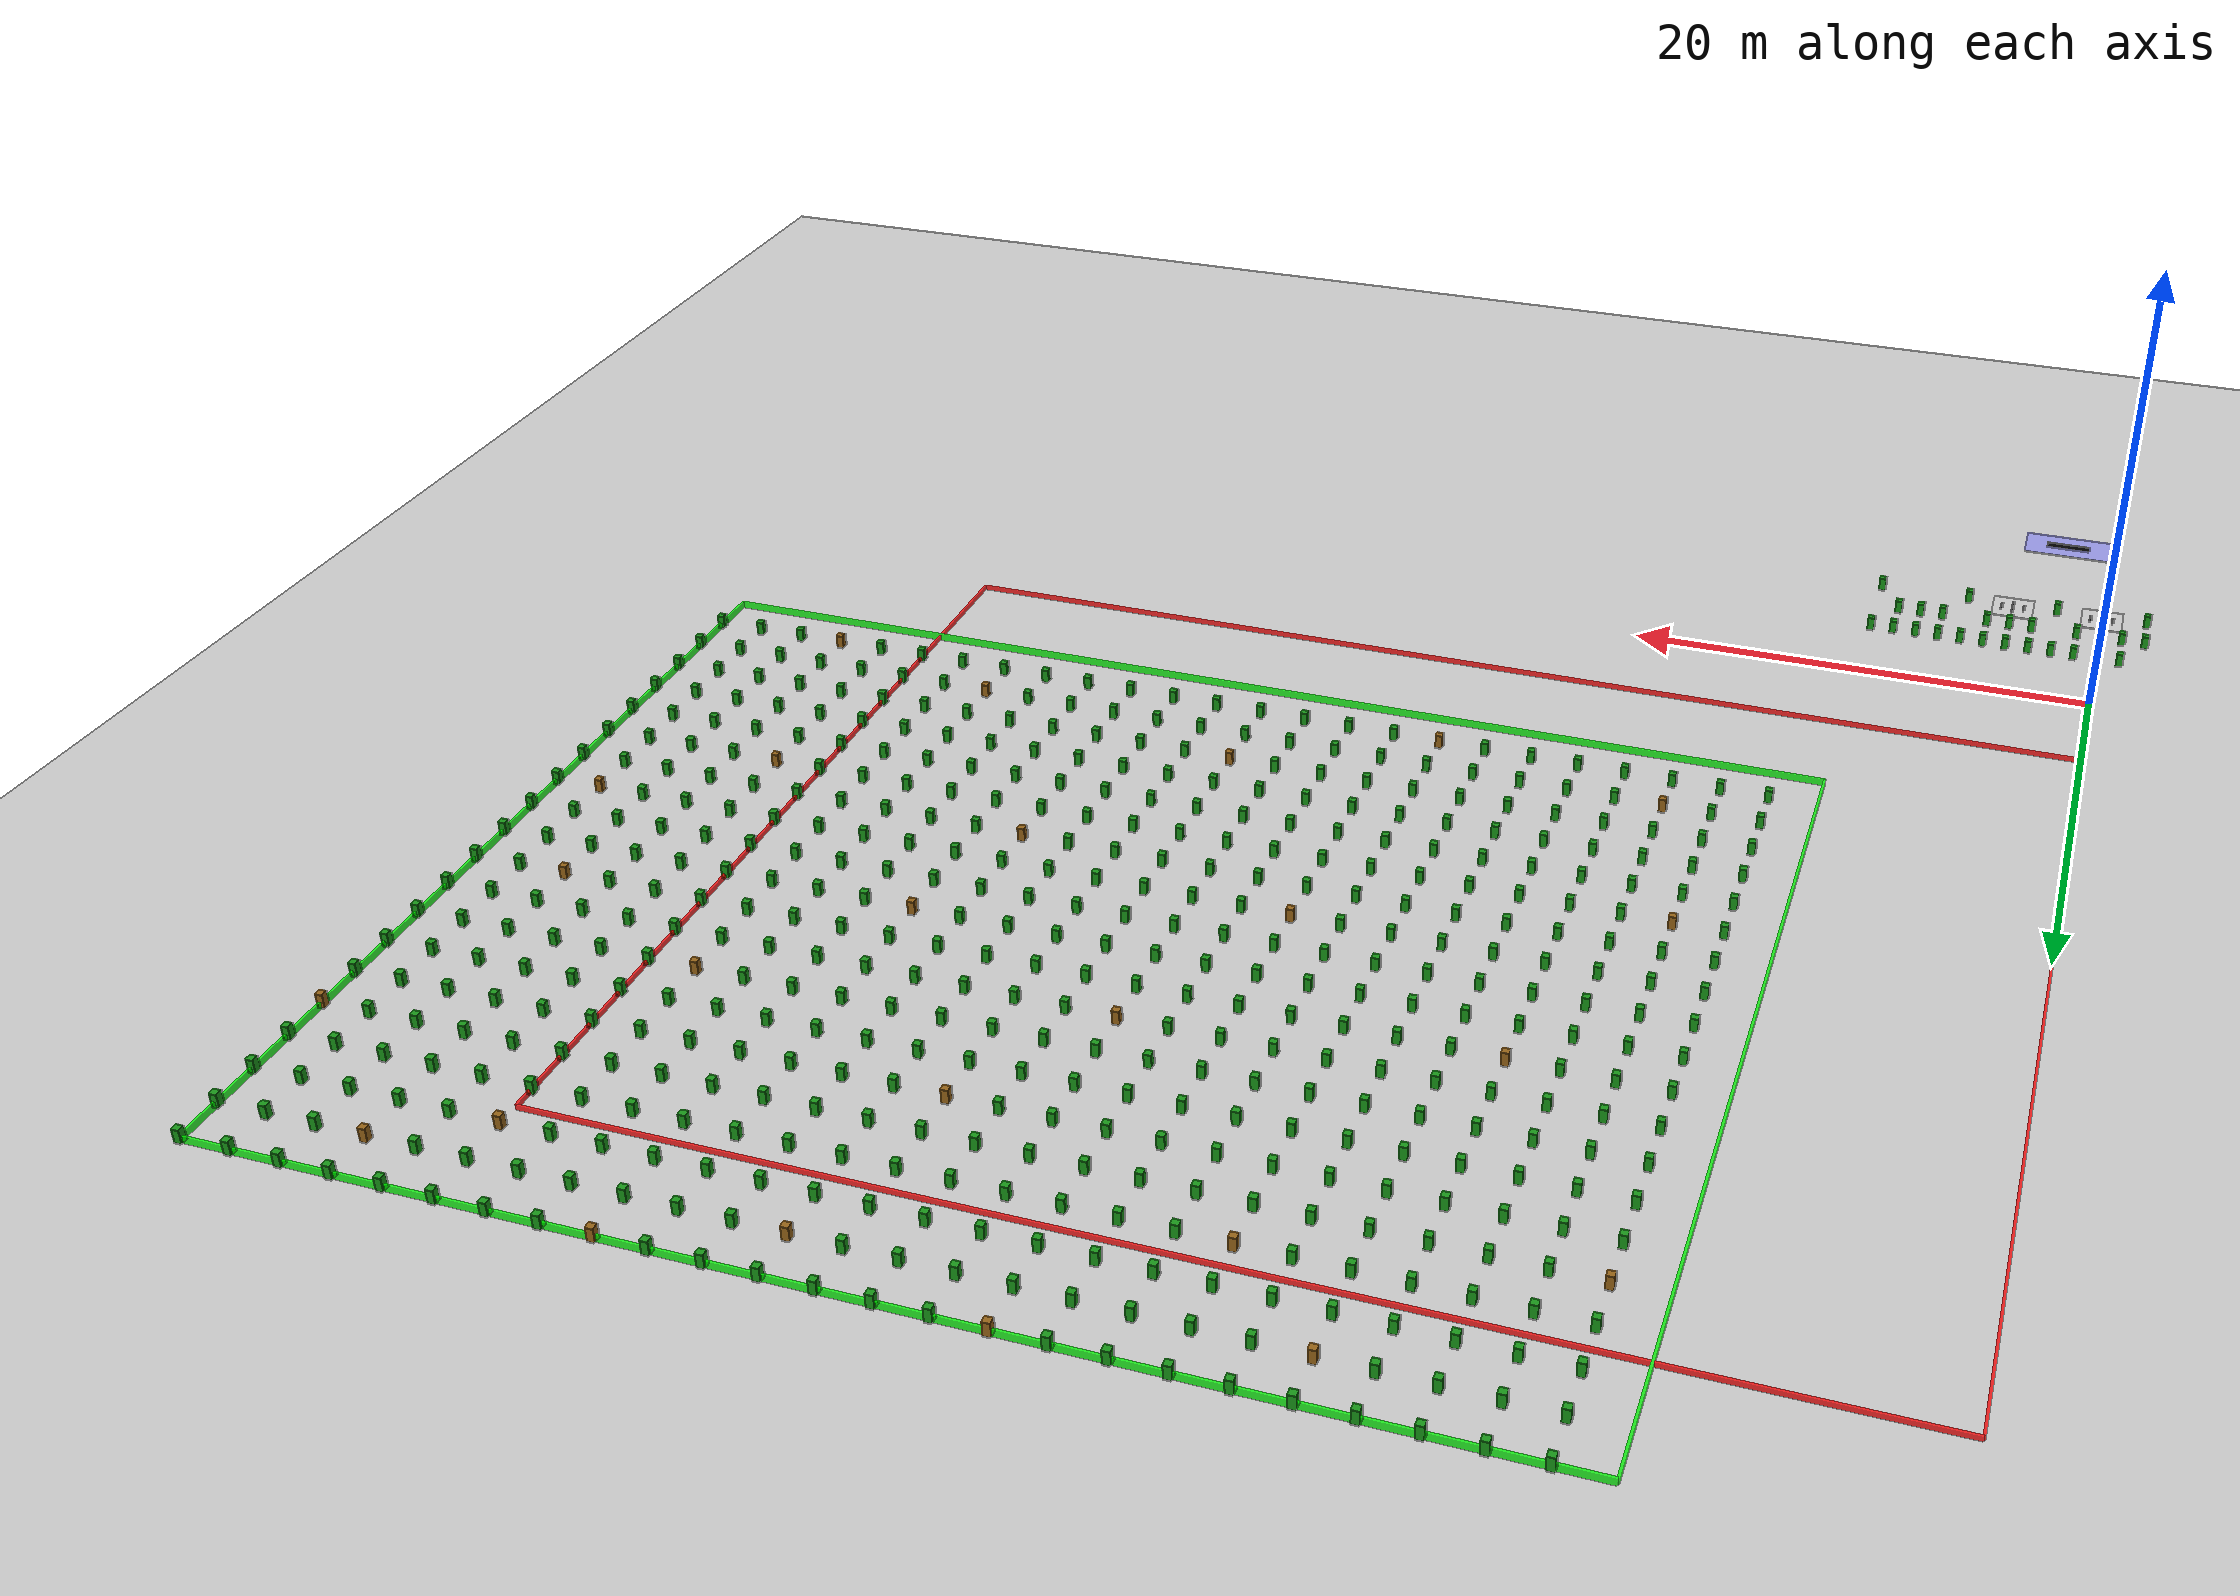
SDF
<sdf version="1.9">
 <world name="agribot_farm">
  <physics name="fast_physics" type="ode">
   <max_step_size>0.001</max_step_size>
   <real_time_factor>1.0</real_time_factor>
  </physics>
  <plugin filename="gz-sim-physics-system" name="gz::sim::systems::Physics"/>
  <plugin filename="gz-sim-sensors-system" name="gz::sim::systems::Sensors">
   <render_engine>ogre2</render_engine>
  </plugin>
  <plugin filename="gz-sim-user-commands-system" name="gz::sim::systems::UserCommands"/>
  <plugin filename="gz-sim-scene-broadcaster-system" name="gz::sim::systems::SceneBroadcaster"/>
  <plugin filename="gz-sim-imu-system" name="gz::sim::systems::Imu"/>
  <plugin filename="gz-sim-navsat-system" name="gz::sim::systems::NavSat"/>
  <scene>
   <ambient>1.0 1.0 1.0</ambient>
   <background>0.7 0.9 1.0</background>
   <sky><clouds><speed>12</speed></clouds></sky>
   <shadows>1</shadows>
  </scene>
  <spherical_coordinates>
   <latitude_deg>-35.363262</latitude_deg>
   <longitude_deg>149.165237</longitude_deg>
   <elevation>584</elevation>
   <heading_deg>0</heading_deg>
   <surface_model>EARTH_WGS84</surface_model>
  </spherical_coordinates>
  <light type="directional" name="sun">
   <pose>0 0 100 0 0 0</pose>
   <diffuse>0.95 0.95 0.9 1</diffuse>
   <specular>0.5 0.5 0.5 1</specular>
   <attenuation>
    <range>1000</range>
    <constant>0.9</constant>
    <linear>0.01</linear>
    <quadratic>0.001</quadratic>
   </attenuation>
   <direction>-0.5 0.1 -0.9</direction>
  </light>
  <model name="axes">
   <static>1</static>
   <link name="link">
    <visual name="r">
     <cast_shadows>0</cast_shadows>
     <pose>5 0 0.1 0 0 0</pose>
     <geometry><box><size>10 0.01 0.01</size></box></geometry>
     <material>
      <ambient>1 0 0 0.8</ambient>
      <diffuse>1 0 0 0.8</diffuse>
      <emissive>1 0 0 0.8</emissive>
      <specular>0.5 0.5 0.5 0.8</specular>
     </material>
    </visual>
    <visual name="g">
     <cast_shadows>0</cast_shadows>
     <pose>0 5 0.1 0 0 0</pose>
     <geometry><box><size>0.01 10 0.01</size></box></geometry>
     <material>
      <ambient>0 1 0 0.8</ambient>
      <diffuse>0 1 0 0.8</diffuse>
      <emissive>0 1 0 0.8</emissive>
      <specular>0.5 0.5 0.5 0.8</specular>
     </material>
    </visual>
    <visual name="b">
     <cast_shadows>0</cast_shadows>
     <pose>0 0 5.1 0 0 0</pose>
     <geometry><box><size>0.01 0.01 10</size></box></geometry>
     <material>
      <ambient>0 0 1 0.8</ambient>
      <diffuse>0 0 1 0.8</diffuse>
      <emissive>0 0 1 0.8</emissive>
      <specular>0.5 0.5 0.5 0.8</specular>
     </material>
    </visual>
    <sensor name="navsat_sensor" type="navsat"><always_on>1</always_on><update_rate>1</update_rate></sensor>
   </link>
  </model>
  <model name="ground_plane">
   <static>true</static>
   <link name="link">
    <collision name="collision">
     <geometry><plane><normal>0 0 1</normal><size>200 200</size></plane></geometry>
    </collision>
    <visual name="visual">
     <geometry><plane><normal>0 0 1</normal><size>200 200</size></plane></geometry>
     <material><script><uri>model://ground_plane</uri><name>Gazebo/DryDirt</name></script></material>
    </visual>
   </link>
  </model>
  <model name="no_fly_zone_boundary">
   <static>true</static>
   <link name="link">
    <visual name="north_boundary">
     <cast_shadows>0</cast_shadows>
     <pose>25 45 0.1 0 0 0</pose>
     <geometry><box><size>50 0.1 0.2</size></box></geometry>
     <material><ambient>1 0 0 0.8</ambient><diffuse>1 0 0 0.8</diffuse></material>
    </visual>
    <visual name="south_boundary">
     <cast_shadows>0</cast_shadows>
     <pose>25 5 0.1 0 0 0</pose>
     <geometry><box><size>50 0.1 0.2</size></box></geometry>
     <material><ambient>1 0 0 0.8</ambient><diffuse>1 0 0 0.8</diffuse></material>
    </visual>
    <visual name="east_boundary">
     <cast_shadows>0</cast_shadows>
     <pose>50 25 0.1 0 0 0</pose>
     <geometry><box><size>0.1 40 0.2</size></box></geometry>
     <material><ambient>1 0 0 0.8</ambient><diffuse>1 0 0 0.8</diffuse></material>
    </visual>
    <visual name="west_boundary">
     <cast_shadows>0</cast_shadows>
     <pose>0 25 0.1 0 0 0</pose>
     <geometry><box><size>0.1 40 0.2</size></box></geometry>
     <material><ambient>1 0 0 0.8</ambient><diffuse>1 0 0 0.8</diffuse></material>
    </visual>
   </link>
  </model>
  <model name="launchpad_1">
   <static>true</static>
   <link name="link">
    <visual name="pad_base">
     <cast_shadows>0</cast_shadows>
     <pose>0 -8 0.01 0 0 0</pose>
     <geometry><box><size>1.83 1.83 0.02</size></box></geometry>
     <material><ambient>0.8 0.8 0.8 1</ambient><diffuse>0.8 0.8 0.8 1</diffuse></material>
    </visual>
    <visual name="h_bar1">
     <cast_shadows>0</cast_shadows>
     <pose>0 -8 0.02 0 0 0</pose>
     <geometry><box><size>0.1 1.2 0.01</size></box></geometry>
     <material><ambient>0 0 0 1</ambient><diffuse>0 0 0 1</diffuse></material>
    </visual>
    <visual name="h_bar2">
     <cast_shadows>0</cast_shadows>
     <pose>-0.5 -8 0.02 0 0 0</pose>
     <geometry><box><size>0.1 0.6 0.01</size></box></geometry>
     <material><ambient>0 0 0 1</ambient><diffuse>0 0 0 1</diffuse></material>
    </visual>
    <visual name="h_bar3">
     <cast_shadows>0</cast_shadows>
     <pose>0.5 -8 0.02 0 0 0</pose>
     <geometry><box><size>0.1 0.6 0.01</size></box></geometry>
     <material><ambient>0 0 0 1</ambient><diffuse>0 0 0 1</diffuse></material>
    </visual>
   </link>
  </model>
  <model name="launchpad_2">
   <static>true</static>
   <link name="link">
    <visual name="pad_base">
     <cast_shadows>0</cast_shadows>
     <pose>4 -8 0.01 0 0 0</pose>
     <geometry><box><size>1.83 1.83 0.02</size></box></geometry>
     <material><ambient>0.8 0.8 0.8 1</ambient><diffuse>0.8 0.8 0.8 1</diffuse></material>
    </visual>
    <visual name="h_bar1">
     <cast_shadows>0</cast_shadows>
     <pose>4 -8 0.02 0 0 0</pose>
     <geometry><box><size>0.1 1.2 0.01</size></box></geometry>
     <material><ambient>0 0 0 1</ambient><diffuse>0 0 0 1</diffuse></material>
    </visual>
    <visual name="h_bar2">
     <cast_shadows>0</cast_shadows>
     <pose>3.5 -8 0.02 0 0 0</pose>
     <geometry><box><size>0.1 0.6 0.01</size></box></geometry>
     <material><ambient>0 0 0 1</ambient><diffuse>0 0 0 1</diffuse></material>
    </visual>
    <visual name="h_bar3">
     <cast_shadows>0</cast_shadows>
     <pose>4.5 -8 0.02 0 0 0</pose>
     <geometry><box><size>0.1 0.6 0.01</size></box></geometry>
     <material><ambient>0 0 0 1</ambient><diffuse>0 0 0 1</diffuse></material>
    </visual>
   </link>
  </model>
  <model name="gcs_area">
   <static>true</static>
   <link name="link">
    <visual name="gcs_platform">
     <cast_shadows>0</cast_shadows>
     <pose>2 -15 0.01 0 0 0</pose>
     <geometry><box><size>4 2 0.02</size></box></geometry>
     <material><ambient>0.6 0.6 0.9 1</ambient><diffuse>0.6 0.6 0.9 1</diffuse></material>
    </visual>
    <visual name="gcs_label">
     <cast_shadows>0</cast_shadows>
     <pose>2 -15 0.02 0 0 0</pose>
     <geometry><box><size>2 0.5 0.01</size></box></geometry>
     <material><ambient>0 0 0 1</ambient><diffuse>0 0 0 1</diffuse></material>
    </visual>
   </link>
  </model>
  <model name="crop_near_1">
   <static>true</static>
   <pose>-2 -8 0.3 0 0 0</pose>
   <link name="link">
    <visual name="visual">
     <geometry><box><size>0.3 0.3 0.6</size></box></geometry>
     <material><ambient>0.1 0.6 0.1 1</ambient><diffuse>0.1 0.6 0.1 1</diffuse></material>
    </visual>
    <collision name="collision"><geometry><box><size>0.3 0.3 0.6</size></box></geometry></collision>
   </link>
  </model>
  <model name="crop_near_2">
   <static>true</static>
   <pose>0 -6 0.3 0 0 0</pose>
   <link name="link">
    <visual name="visual">
     <geometry><box><size>0.3 0.3 0.6</size></box></geometry>
     <material><ambient>0.1 0.6 0.1 1</ambient><diffuse>0.1 0.6 0.1 1</diffuse></material>
    </visual>
    <collision name="collision"><geometry><box><size>0.3 0.3 0.6</size></box></geometry></collision>
   </link>
  </model>
  <model name="crop_near_3">
   <static>true</static>
   <pose>2 -8 0.3 0 0 0</pose>
   <link name="link">
    <visual name="visual">
     <geometry><box><size>0.3 0.3 0.6</size></box></geometry>
     <material><ambient>0.1 0.6 0.1 1</ambient><diffuse>0.1 0.6 0.1 1</diffuse></material>
    </visual>
    <collision name="collision"><geometry><box><size>0.3 0.3 0.6</size></box></geometry></collision>
   </link>
  </model>
  <model name="crop_near_4">
   <static>true</static>
   <pose>4 -6 0.3 0 0 0</pose>
   <link name="link">
    <visual name="visual">
     <geometry><box><size>0.3 0.3 0.6</size></box></geometry>
     <material><ambient>0.1 0.6 0.1 1</ambient><diffuse>0.1 0.6 0.1 1</diffuse></material>
    </visual>
    <collision name="collision"><geometry><box><size>0.3 0.3 0.6</size></box></geometry></collision>
   </link>
  </model>
  <model name="crop_near_5">
   <static>true</static>
   <pose>6 -8 0.3 0 0 0</pose>
   <link name="link">
    <visual name="visual">
     <geometry><box><size>0.3 0.3 0.6</size></box></geometry>
     <material><ambient>0.1 0.6 0.1 1</ambient><diffuse>0.1 0.6 0.1 1</diffuse></material>
    </visual>
    <collision name="collision"><geometry><box><size>0.3 0.3 0.6</size></box></geometry></collision>
   </link>
  </model>
  <model name="crop_near_6">
   <static>true</static>
   <pose>8 -6 0.3 0 0 0</pose>
   <link name="link">
    <visual name="visual">
     <geometry><box><size>0.3 0.3 0.6</size></box></geometry>
     <material><ambient>0.1 0.6 0.1 1</ambient><diffuse>0.1 0.6 0.1 1</diffuse></material>
    </visual>
    <collision name="collision"><geometry><box><size>0.3 0.3 0.6</size></box></geometry></collision>
   </link>
  </model>
  <model name="crop_near_7">
   <static>true</static>
   <pose>10 -8 0.3 0 0 0</pose>
   <link name="link">
    <visual name="visual">
     <geometry><box><size>0.3 0.3 0.6</size></box></geometry>
     <material><ambient>0.1 0.6 0.1 1</ambient><diffuse>0.1 0.6 0.1 1</diffuse></material>
    </visual>
    <collision name="collision"><geometry><box><size>0.3 0.3 0.6</size></box></geometry></collision>
   </link>
  </model>
  <model name="crop_near_8">
   <static>true</static>
   <pose>-2 -6 0.3 0 0 0</pose>
   <link name="link">
    <visual name="visual">
     <geometry><box><size>0.3 0.3 0.6</size></box></geometry>
     <material><ambient>0.1 0.6 0.1 1</ambient><diffuse>0.1 0.6 0.1 1</diffuse></material>
    </visual>
    <collision name="collision"><geometry><box><size>0.3 0.3 0.6</size></box></geometry></collision>
   </link>
  </model>
  <model name="crop_near_9">
   <static>true</static>
   <pose>0 -4 0.3 0 0 0</pose>
   <link name="link">
    <visual name="visual">
     <geometry><box><size>0.3 0.3 0.6</size></box></geometry>
     <material><ambient>0.1 0.6 0.1 1</ambient><diffuse>0.1 0.6 0.1 1</diffuse></material>
    </visual>
    <collision name="collision"><geometry><box><size>0.3 0.3 0.6</size></box></geometry></collision>
   </link>
  </model>
  <model name="crop_near_10">
   <static>true</static>
   <pose>2 -4 0.3 0 0 0</pose>
   <link name="link">
    <visual name="visual">
     <geometry><box><size>0.3 0.3 0.6</size></box></geometry>
     <material><ambient>0.1 0.6 0.1 1</ambient><diffuse>0.1 0.6 0.1 1</diffuse></material>
    </visual>
    <collision name="collision"><geometry><box><size>0.3 0.3 0.6</size></box></geometry></collision>
   </link>
  </model>
  <model name="crop_near_11">
   <static>true</static>
   <pose>4 -4 0.3 0 0 0</pose>
   <link name="link">
    <visual name="visual">
     <geometry><box><size>0.3 0.3 0.6</size></box></geometry>
     <material><ambient>0.1 0.6 0.1 1</ambient><diffuse>0.1 0.6 0.1 1</diffuse></material>
    </visual>
    <collision name="collision"><geometry><box><size>0.3 0.3 0.6</size></box></geometry></collision>
   </link>
  </model>
  <model name="crop_near_12">
   <static>true</static>
   <pose>6 -4 0.3 0 0 0</pose>
   <link name="link">
    <visual name="visual">
     <geometry><box><size>0.3 0.3 0.6</size></box></geometry>
     <material><ambient>0.1 0.6 0.1 1</ambient><diffuse>0.1 0.6 0.1 1</diffuse></material>
    </visual>
    <collision name="collision"><geometry><box><size>0.3 0.3 0.6</size></box></geometry></collision>
   </link>
  </model>
  <model name="crop_near_13">
   <static>true</static>
   <pose>8 -4 0.3 0 0 0</pose>
   <link name="link">
    <visual name="visual">
     <geometry><box><size>0.3 0.3 0.6</size></box></geometry>
     <material><ambient>0.1 0.6 0.1 1</ambient><diffuse>0.1 0.6 0.1 1</diffuse></material>
    </visual>
    <collision name="collision"><geometry><box><size>0.3 0.3 0.6</size></box></geometry></collision>
   </link>
  </model>
  <model name="crop_near_14">
   <static>true</static>
   <pose>10 -4 0.3 0 0 0</pose>
   <link name="link">
    <visual name="visual">
     <geometry><box><size>0.3 0.3 0.6</size></box></geometry>
     <material><ambient>0.1 0.6 0.1 1</ambient><diffuse>0.1 0.6 0.1 1</diffuse></material>
    </visual>
    <collision name="collision"><geometry><box><size>0.3 0.3 0.6</size></box></geometry></collision>
   </link>
  </model>
  <model name="crop_fill_1">
   <static>true</static>
   <pose>-1 -6 0.3 0 0 0</pose>
   <link name="link">
    <visual name="visual">
     <geometry><box><size>0.3 0.3 0.6</size></box></geometry>
     <material><ambient>0.1 0.6 0.1 1</ambient><diffuse>0.1 0.6 0.1 1</diffuse></material>
    </visual>
   </link>
  </model>
  <model name="crop_fill_2">
   <static>true</static>
   <pose>1 -6 0.3 0 0 0</pose>
   <link name="link">
    <visual name="visual">
     <geometry><box><size>0.3 0.3 0.6</size></box></geometry>
     <material><ambient>0.1 0.6 0.1 1</ambient><diffuse>0.1 0.6 0.1 1</diffuse></material>
    </visual>
   </link>
  </model>
  <model name="crop_fill_3">
   <static>true</static>
   <pose>3 -6 0.3 0 0 0</pose>
   <link name="link">
    <visual name="visual">
     <geometry><box><size>0.3 0.3 0.6</size></box></geometry>
     <material><ambient>0.1 0.6 0.1 1</ambient><diffuse>0.1 0.6 0.1 1</diffuse></material>
    </visual>
   </link>
  </model>
  <model name="crop_fill_4">
   <static>true</static>
   <pose>5 -6 0.3 0 0 0</pose>
   <link name="link">
    <visual name="visual">
     <geometry><box><size>0.3 0.3 0.6</size></box></geometry>
     <material><ambient>0.1 0.6 0.1 1</ambient><diffuse>0.1 0.6 0.1 1</diffuse></material>
    </visual>
   </link>
  </model>
  <model name="crop_fill_5">
   <static>true</static>
   <pose>7 -6 0.3 0 0 0</pose>
   <link name="link">
    <visual name="visual">
     <geometry><box><size>0.3 0.3 0.6</size></box></geometry>
     <material><ambient>0.1 0.6 0.1 1</ambient><diffuse>0.1 0.6 0.1 1</diffuse></material>
    </visual>
   </link>
  </model>
  <model name="crop_fill_6">
   <static>true</static>
   <pose>9 -6 0.3 0 0 0</pose>
   <link name="link">
    <visual name="visual">
     <geometry><box><size>0.3 0.3 0.6</size></box></geometry>
     <material><ambient>0.1 0.6 0.1 1</ambient><diffuse>0.1 0.6 0.1 1</diffuse></material>
    </visual>
   </link>
  </model>
  <model name="crop_fill_7">
   <static>true</static>
   <pose>-1 -4 0.3 0 0 0</pose>
   <link name="link">
    <visual name="visual">
     <geometry><box><size>0.3 0.3 0.6</size></box></geometry>
     <material><ambient>0.1 0.6 0.1 1</ambient><diffuse>0.1 0.6 0.1 1</diffuse></material>
    </visual>
   </link>
  </model>
  <model name="crop_fill_8">
   <static>true</static>
   <pose>1 -4 0.3 0 0 0</pose>
   <link name="link">
    <visual name="visual">
     <geometry><box><size>0.3 0.3 0.6</size></box></geometry>
     <material><ambient>0.1 0.6 0.1 1</ambient><diffuse>0.1 0.6 0.1 1</diffuse></material>
    </visual>
   </link>
  </model>
  <model name="crop_fill_9">
   <static>true</static>
   <pose>3 -4 0.3 0 0 0</pose>
   <link name="link">
    <visual name="visual">
     <geometry><box><size>0.3 0.3 0.6</size></box></geometry>
     <material><ambient>0.1 0.6 0.1 1</ambient><diffuse>0.1 0.6 0.1 1</diffuse></material>
    </visual>
   </link>
  </model>
  <model name="crop_fill_10">
   <static>true</static>
   <pose>5 -4 0.3 0 0 0</pose>
   <link name="link">
    <visual name="visual">
     <geometry><box><size>0.3 0.3 0.6</size></box></geometry>
     <material><ambient>0.1 0.6 0.1 1</ambient><diffuse>0.1 0.6 0.1 1</diffuse></material>
    </visual>
   </link>
  </model>
  <model name="crop_fill_11">
   <static>true</static>
   <pose>7 -4 0.3 0 0 0</pose>
   <link name="link">
    <visual name="visual">
     <geometry><box><size>0.3 0.3 0.6</size></box></geometry>
     <material><ambient>0.1 0.6 0.1 1</ambient><diffuse>0.1 0.6 0.1 1</diffuse></material>
    </visual>
   </link>
  </model>
  <model name="crop_fill_12">
   <static>true</static>
   <pose>9 -4 0.3 0 0 0</pose>
   <link name="link">
    <visual name="visual">
     <geometry><box><size>0.3 0.3 0.6</size></box></geometry>
     <material><ambient>0.1 0.6 0.1 1</ambient><diffuse>0.1 0.6 0.1 1</diffuse></material>
    </visual>
   </link>
  </model>
  <model name="crop_1">
   <static>true</static>
   <link name="link">
    <visual name="visual">
     <geometry><box><size>0.300 0.300 0.600</size></box></geometry>
     <material><ambient>0.1 0.6 0.1 1</ambient><diffuse>0.1 0.6 0.1 1</diffuse></material>
    </visual>
    <collision name="collision"><geometry><box><size>0.300 0.300 0.600</size></box></geometry></collision>
    <pose>12.0 12.0 0.300 0 0 0</pose>
   </link>
  </model>
  <model name="crop_2">
   <static>true</static>
   <link name="link">
    <visual name="visual">
     <geometry><box><size>0.300 0.300 0.600</size></box></geometry>
     <material><ambient>0.1 0.6 0.1 1</ambient><diffuse>0.1 0.6 0.1 1</diffuse></material>
    </visual>
    <collision name="collision"><geometry><box><size>0.300 0.300 0.600</size></box></geometry></collision>
    <pose>14.0 12.0 0.300 0 0 0</pose>
   </link>
  </model>
  <model name="crop_3">
   <static>true</static>
   <link name="link">
    <visual name="visual">
     <geometry><box><size>0.300 0.300 0.600</size></box></geometry>
     <material><ambient>0.1 0.6 0.1 1</ambient><diffuse>0.1 0.6 0.1 1</diffuse></material>
    </visual>
    <collision name="collision"><geometry><box><size>0.300 0.300 0.600</size></box></geometry></collision>
    <pose>16.0 12.0 0.300 0 0 0</pose>
   </link>
  </model>
  <model name="crop_4">
   <static>true</static>
   <link name="link">
    <visual name="visual">
     <geometry><box><size>0.300 0.300 0.600</size></box></geometry>
     <material><ambient>0.1 0.6 0.1 1</ambient><diffuse>0.1 0.6 0.1 1</diffuse></material>
    </visual>
    <collision name="collision"><geometry><box><size>0.300 0.300 0.600</size></box></geometry></collision>
    <pose>18.0 12.0 0.300 0 0 0</pose>
   </link>
  </model>
  <model name="crop_5">
   <static>true</static>
   <link name="link">
    <visual name="visual">
     <geometry><box><size>0.300 0.300 0.600</size></box></geometry>
     <material><ambient>0.1 0.6 0.1 1</ambient><diffuse>0.1 0.6 0.1 1</diffuse></material>
    </visual>
    <collision name="collision"><geometry><box><size>0.300 0.300 0.600</size></box></geometry></collision>
    <pose>20.0 12.0 0.300 0 0 0</pose>
   </link>
  </model>
  <model name="crop_6">
   <static>true</static>
   <link name="link">
    <visual name="visual">
     <geometry><box><size>0.300 0.300 0.600</size></box></geometry>
     <material><ambient>0.1 0.6 0.1 1</ambient><diffuse>0.1 0.6 0.1 1</diffuse></material>
    </visual>
    <collision name="collision"><geometry><box><size>0.300 0.300 0.600</size></box></geometry></collision>
    <pose>22.0 12.0 0.300 0 0 0</pose>
   </link>
  </model>
  <model name="crop_7">
   <static>true</static>
   <link name="link">
    <visual name="visual">
     <geometry><box><size>0.300 0.300 0.600</size></box></geometry>
     <material><ambient>0.1 0.6 0.1 1</ambient><diffuse>0.1 0.6 0.1 1</diffuse></material>
    </visual>
    <collision name="collision"><geometry><box><size>0.300 0.300 0.600</size></box></geometry></collision>
    <pose>24.0 12.0 0.300 0 0 0</pose>
   </link>
  </model>
  <model name="crop_8">
   <static>true</static>
   <link name="link">
    <visual name="visual">
     <geometry><box><size>0.300 0.300 0.600</size></box></geometry>
     <material><ambient>0.6 0.4 0.1 1</ambient><diffuse>0.6 0.4 0.1 1</diffuse></material>
    </visual>
    <collision name="collision"><geometry><box><size>0.300 0.300 0.600</size></box></geometry></collision>
    <pose>26.0 12.0 0.300 0 0 0</pose>
   </link>
  </model>
  <model name="crop_9">
   <static>true</static>
   <link name="link">
    <visual name="visual">
     <geometry><box><size>0.300 0.300 0.600</size></box></geometry>
     <material><ambient>0.1 0.6 0.1 1</ambient><diffuse>0.1 0.6 0.1 1</diffuse></material>
    </visual>
    <collision name="collision"><geometry><box><size>0.300 0.300 0.600</size></box></geometry></collision>
    <pose>28.0 12.0 0.300 0 0 0</pose>
   </link>
  </model>
  <model name="crop_10">
   <static>true</static>
   <link name="link">
    <visual name="visual">
     <geometry><box><size>0.300 0.300 0.600</size></box></geometry>
     <material><ambient>0.1 0.6 0.1 1</ambient><diffuse>0.1 0.6 0.1 1</diffuse></material>
    </visual>
    <collision name="collision"><geometry><box><size>0.300 0.300 0.600</size></box></geometry></collision>
    <pose>30.0 12.0 0.300 0 0 0</pose>
   </link>
  </model>
  <model name="crop_11">
   <static>true</static>
   <link name="link">
    <visual name="visual">
     <geometry><box><size>0.300 0.300 0.600</size></box></geometry>
     <material><ambient>0.1 0.6 0.1 1</ambient><diffuse>0.1 0.6 0.1 1</diffuse></material>
    </visual>
    <collision name="collision"><geometry><box><size>0.300 0.300 0.600</size></box></geometry></collision>
    <pose>32.0 12.0 0.300 0 0 0</pose>
   </link>
  </model>
  <model name="crop_12">
   <static>true</static>
   <link name="link">
    <visual name="visual">
     <geometry><box><size>0.300 0.300 0.600</size></box></geometry>
     <material><ambient>0.1 0.6 0.1 1</ambient><diffuse>0.1 0.6 0.1 1</diffuse></material>
    </visual>
    <collision name="collision"><geometry><box><size>0.300 0.300 0.600</size></box></geometry></collision>
    <pose>34.0 12.0 0.300 0 0 0</pose>
   </link>
  </model>
  <model name="crop_13">
   <static>true</static>
   <link name="link">
    <visual name="visual">
     <geometry><box><size>0.300 0.300 0.600</size></box></geometry>
     <material><ambient>0.1 0.6 0.1 1</ambient><diffuse>0.1 0.6 0.1 1</diffuse></material>
    </visual>
    <collision name="collision"><geometry><box><size>0.300 0.300 0.600</size></box></geometry></collision>
    <pose>36.0 12.0 0.300 0 0 0</pose>
   </link>
  </model>
  <model name="crop_14">
   <static>true</static>
   <link name="link">
    <visual name="visual">
     <geometry><box><size>0.300 0.300 0.600</size></box></geometry>
     <material><ambient>0.1 0.6 0.1 1</ambient><diffuse>0.1 0.6 0.1 1</diffuse></material>
    </visual>
    <collision name="collision"><geometry><box><size>0.300 0.300 0.600</size></box></geometry></collision>
    <pose>38.0 12.0 0.300 0 0 0</pose>
   </link>
  </model>
  <model name="crop_15">
   <static>true</static>
   <link name="link">
    <visual name="visual">
     <geometry><box><size>0.300 0.300 0.600</size></box></geometry>
     <material><ambient>0.1 0.6 0.1 1</ambient><diffuse>0.1 0.6 0.1 1</diffuse></material>
    </visual>
    <collision name="collision"><geometry><box><size>0.300 0.300 0.600</size></box></geometry></collision>
    <pose>40.0 12.0 0.300 0 0 0</pose>
   </link>
  </model>
  <model name="crop_16">
   <static>true</static>
   <link name="link">
    <visual name="visual">
     <geometry><box><size>0.300 0.300 0.600</size></box></geometry>
     <material><ambient>0.1 0.6 0.1 1</ambient><diffuse>0.1 0.6 0.1 1</diffuse></material>
    </visual>
    <collision name="collision"><geometry><box><size>0.300 0.300 0.600</size></box></geometry></collision>
    <pose>42.0 12.0 0.300 0 0 0</pose>
   </link>
  </model>
  <model name="crop_17">
   <static>true</static>
   <link name="link">
    <visual name="visual">
     <geometry><box><size>0.300 0.300 0.600</size></box></geometry>
     <material><ambient>0.1 0.6 0.1 1</ambient><diffuse>0.1 0.6 0.1 1</diffuse></material>
    </visual>
    <collision name="collision"><geometry><box><size>0.300 0.300 0.600</size></box></geometry></collision>
    <pose>44.0 12.0 0.300 0 0 0</pose>
   </link>
  </model>
  <model name="crop_18">
   <static>true</static>
   <link name="link">
    <visual name="visual">
     <geometry><box><size>0.300 0.300 0.600</size></box></geometry>
     <material><ambient>0.1 0.6 0.1 1</ambient><diffuse>0.1 0.6 0.1 1</diffuse></material>
    </visual>
    <collision name="collision"><geometry><box><size>0.300 0.300 0.600</size></box></geometry></collision>
    <pose>46.0 12.0 0.300 0 0 0</pose>
   </link>
  </model>
  <model name="crop_19">
   <static>true</static>
   <link name="link">
    <visual name="visual">
     <geometry><box><size>0.300 0.300 0.600</size></box></geometry>
     <material><ambient>0.1 0.6 0.1 1</ambient><diffuse>0.1 0.6 0.1 1</diffuse></material>
    </visual>
    <collision name="collision"><geometry><box><size>0.300 0.300 0.600</size></box></geometry></collision>
    <pose>48.0 12.0 0.300 0 0 0</pose>
   </link>
  </model>
  <model name="crop_20">
   <static>true</static>
   <link name="link">
    <visual name="visual">
     <geometry><box><size>0.300 0.300 0.600</size></box></geometry>
     <material><ambient>0.1 0.6 0.1 1</ambient><diffuse>0.1 0.6 0.1 1</diffuse></material>
    </visual>
    <collision name="collision"><geometry><box><size>0.300 0.300 0.600</size></box></geometry></collision>
    <pose>50.0 12.0 0.300 0 0 0</pose>
   </link>
  </model>
  <model name="crop_21">
   <static>true</static>
   <link name="link">
    <visual name="visual">
     <geometry><box><size>0.300 0.300 0.600</size></box></geometry>
     <material><ambient>0.1 0.6 0.1 1</ambient><diffuse>0.1 0.6 0.1 1</diffuse></material>
    </visual>
    <collision name="collision"><geometry><box><size>0.300 0.300 0.600</size></box></geometry></collision>
    <pose>52.0 12.0 0.300 0 0 0</pose>
   </link>
  </model>
  <model name="crop_22">
   <static>true</static>
   <link name="link">
    <visual name="visual">
     <geometry><box><size>0.300 0.300 0.600</size></box></geometry>
     <material><ambient>0.6 0.4 0.1 1</ambient><diffuse>0.6 0.4 0.1 1</diffuse></material>
    </visual>
    <collision name="collision"><geometry><box><size>0.300 0.300 0.600</size></box></geometry></collision>
    <pose>54.0 12.0 0.300 0 0 0</pose>
   </link>
  </model>
  <model name="crop_23">
   <static>true</static>
   <link name="link">
    <visual name="visual">
     <geometry><box><size>0.300 0.300 0.600</size></box></geometry>
     <material><ambient>0.1 0.6 0.1 1</ambient><diffuse>0.1 0.6 0.1 1</diffuse></material>
    </visual>
    <collision name="collision"><geometry><box><size>0.300 0.300 0.600</size></box></geometry></collision>
    <pose>56.0 12.0 0.300 0 0 0</pose>
   </link>
  </model>
  <model name="crop_24">
   <static>true</static>
   <link name="link">
    <visual name="visual">
     <geometry><box><size>0.300 0.300 0.600</size></box></geometry>
     <material><ambient>0.1 0.6 0.1 1</ambient><diffuse>0.1 0.6 0.1 1</diffuse></material>
    </visual>
    <collision name="collision"><geometry><box><size>0.300 0.300 0.600</size></box></geometry></collision>
    <pose>58.0 12.0 0.300 0 0 0</pose>
   </link>
  </model>
  <model name="crop_25">
   <static>true</static>
   <link name="link">
    <visual name="visual">
     <geometry><box><size>0.300 0.300 0.600</size></box></geometry>
     <material><ambient>0.1 0.6 0.1 1</ambient><diffuse>0.1 0.6 0.1 1</diffuse></material>
    </visual>
    <collision name="collision"><geometry><box><size>0.300 0.300 0.600</size></box></geometry></collision>
    <pose>60.0 12.0 0.300 0 0 0</pose>
   </link>
  </model>
  <model name="crop_26">
   <static>true</static>
   <link name="link">
    <visual name="visual">
     <geometry><box><size>0.300 0.300 0.600</size></box></geometry>
     <material><ambient>0.1 0.6 0.1 1</ambient><diffuse>0.1 0.6 0.1 1</diffuse></material>
    </visual>
    <collision name="collision"><geometry><box><size>0.300 0.300 0.600</size></box></geometry></collision>
    <pose>12.0 14.0 0.300 0 0 0</pose>
   </link>
  </model>
  <model name="crop_27">
   <static>true</static>
   <link name="link">
    <visual name="visual">
     <geometry><box><size>0.300 0.300 0.600</size></box></geometry>
     <material><ambient>0.1 0.6 0.1 1</ambient><diffuse>0.1 0.6 0.1 1</diffuse></material>
    </visual>
    <collision name="collision"><geometry><box><size>0.300 0.300 0.600</size></box></geometry></collision>
    <pose>14.0 14.0 0.300 0 0 0</pose>
   </link>
  </model>
  <model name="crop_28">
   <static>true</static>
   <link name="link">
    <visual name="visual">
     <geometry><box><size>0.300 0.300 0.600</size></box></geometry>
     <material><ambient>0.6 0.4 0.1 1</ambient><diffuse>0.6 0.4 0.1 1</diffuse></material>
    </visual>
    <collision name="collision"><geometry><box><size>0.300 0.300 0.600</size></box></geometry></collision>
    <pose>16.0 14.0 0.300 0 0 0</pose>
   </link>
  </model>
  <model name="crop_29">
   <static>true</static>
   <link name="link">
    <visual name="visual">
     <geometry><box><size>0.300 0.300 0.600</size></box></geometry>
     <material><ambient>0.1 0.6 0.1 1</ambient><diffuse>0.1 0.6 0.1 1</diffuse></material>
    </visual>
    <collision name="collision"><geometry><box><size>0.300 0.300 0.600</size></box></geometry></collision>
    <pose>18.0 14.0 0.300 0 0 0</pose>
   </link>
  </model>
  <model name="crop_30">
   <static>true</static>
   <link name="link">
    <visual name="visual">
     <geometry><box><size>0.300 0.300 0.600</size></box></geometry>
     <material><ambient>0.1 0.6 0.1 1</ambient><diffuse>0.1 0.6 0.1 1</diffuse></material>
    </visual>
    <collision name="collision"><geometry><box><size>0.300 0.300 0.600</size></box></geometry></collision>
    <pose>20.0 14.0 0.300 0 0 0</pose>
   </link>
  </model>
  <model name="crop_31">
   <static>true</static>
   <link name="link">
    <visual name="visual">
     <geometry><box><size>0.300 0.300 0.600</size></box></geometry>
     <material><ambient>0.1 0.6 0.1 1</ambient><diffuse>0.1 0.6 0.1 1</diffuse></material>
    </visual>
    <collision name="collision"><geometry><box><size>0.300 0.300 0.600</size></box></geometry></collision>
    <pose>22.0 14.0 0.300 0 0 0</pose>
   </link>
  </model>
  <model name="crop_32">
   <static>true</static>
   <link name="link">
    <visual name="visual">
     <geometry><box><size>0.300 0.300 0.600</size></box></geometry>
     <material><ambient>0.1 0.6 0.1 1</ambient><diffuse>0.1 0.6 0.1 1</diffuse></material>
    </visual>
    <collision name="collision"><geometry><box><size>0.300 0.300 0.600</size></box></geometry></collision>
    <pose>24.0 14.0 0.300 0 0 0</pose>
   </link>
  </model>
  <model name="crop_33">
   <static>true</static>
   <link name="link">
    <visual name="visual">
     <geometry><box><size>0.300 0.300 0.600</size></box></geometry>
     <material><ambient>0.1 0.6 0.1 1</ambient><diffuse>0.1 0.6 0.1 1</diffuse></material>
    </visual>
    <collision name="collision"><geometry><box><size>0.300 0.300 0.600</size></box></geometry></collision>
    <pose>26.0 14.0 0.300 0 0 0</pose>
   </link>
  </model>
  <model name="crop_34">
   <static>true</static>
   <link name="link">
    <visual name="visual">
     <geometry><box><size>0.300 0.300 0.600</size></box></geometry>
     <material><ambient>0.1 0.6 0.1 1</ambient><diffuse>0.1 0.6 0.1 1</diffuse></material>
    </visual>
    <collision name="collision"><geometry><box><size>0.300 0.300 0.600</size></box></geometry></collision>
    <pose>28.0 14.0 0.300 0 0 0</pose>
   </link>
  </model>
  <model name="crop_35">
   <static>true</static>
   <link name="link">
    <visual name="visual">
     <geometry><box><size>0.300 0.300 0.600</size></box></geometry>
     <material><ambient>0.1 0.6 0.1 1</ambient><diffuse>0.1 0.6 0.1 1</diffuse></material>
    </visual>
    <collision name="collision"><geometry><box><size>0.300 0.300 0.600</size></box></geometry></collision>
    <pose>30.0 14.0 0.300 0 0 0</pose>
   </link>
  </model>
  <model name="crop_36">
   <static>true</static>
   <link name="link">
    <visual name="visual">
     <geometry><box><size>0.300 0.300 0.600</size></box></geometry>
     <material><ambient>0.1 0.6 0.1 1</ambient><diffuse>0.1 0.6 0.1 1</diffuse></material>
    </visual>
    <collision name="collision"><geometry><box><size>0.300 0.300 0.600</size></box></geometry></collision>
    <pose>32.0 14.0 0.300 0 0 0</pose>
   </link>
  </model>
  <model name="crop_37">
   <static>true</static>
   <link name="link">
    <visual name="visual">
     <geometry><box><size>0.300 0.300 0.600</size></box></geometry>
     <material><ambient>0.1 0.6 0.1 1</ambient><diffuse>0.1 0.6 0.1 1</diffuse></material>
    </visual>
    <collision name="collision"><geometry><box><size>0.300 0.300 0.600</size></box></geometry></collision>
    <pose>34.0 14.0 0.300 0 0 0</pose>
   </link>
  </model>
  <model name="crop_38">
   <static>true</static>
   <link name="link">
    <visual name="visual">
     <geometry><box><size>0.300 0.300 0.600</size></box></geometry>
     <material><ambient>0.1 0.6 0.1 1</ambient><diffuse>0.1 0.6 0.1 1</diffuse></material>
    </visual>
    <collision name="collision"><geometry><box><size>0.300 0.300 0.600</size></box></geometry></collision>
    <pose>36.0 14.0 0.300 0 0 0</pose>
   </link>
  </model>
  <model name="crop_39">
   <static>true</static>
   <link name="link">
    <visual name="visual">
     <geometry><box><size>0.300 0.300 0.600</size></box></geometry>
     <material><ambient>0.1 0.6 0.1 1</ambient><diffuse>0.1 0.6 0.1 1</diffuse></material>
    </visual>
    <collision name="collision"><geometry><box><size>0.300 0.300 0.600</size></box></geometry></collision>
    <pose>38.0 14.0 0.300 0 0 0</pose>
   </link>
  </model>
  <model name="crop_40">
   <static>true</static>
   <link name="link">
    <visual name="visual">
     <geometry><box><size>0.300 0.300 0.600</size></box></geometry>
     <material><ambient>0.1 0.6 0.1 1</ambient><diffuse>0.1 0.6 0.1 1</diffuse></material>
    </visual>
    <collision name="collision"><geometry><box><size>0.300 0.300 0.600</size></box></geometry></collision>
    <pose>40.0 14.0 0.300 0 0 0</pose>
   </link>
  </model>
  <model name="crop_41">
   <static>true</static>
   <link name="link">
    <visual name="visual">
     <geometry><box><size>0.300 0.300 0.600</size></box></geometry>
     <material><ambient>0.1 0.6 0.1 1</ambient><diffuse>0.1 0.6 0.1 1</diffuse></material>
    </visual>
    <collision name="collision"><geometry><box><size>0.300 0.300 0.600</size></box></geometry></collision>
    <pose>42.0 14.0 0.300 0 0 0</pose>
   </link>
  </model>
  <model name="crop_42">
   <static>true</static>
   <link name="link">
    <visual name="visual">
     <geometry><box><size>0.300 0.300 0.600</size></box></geometry>
     <material><ambient>0.1 0.6 0.1 1</ambient><diffuse>0.1 0.6 0.1 1</diffuse></material>
    </visual>
    <collision name="collision"><geometry><box><size>0.300 0.300 0.600</size></box></geometry></collision>
    <pose>44.0 14.0 0.300 0 0 0</pose>
   </link>
  </model>
  <model name="crop_43">
   <static>true</static>
   <link name="link">
    <visual name="visual">
     <geometry><box><size>0.300 0.300 0.600</size></box></geometry>
     <material><ambient>0.6 0.4 0.1 1</ambient><diffuse>0.6 0.4 0.1 1</diffuse></material>
    </visual>
    <collision name="collision"><geometry><box><size>0.300 0.300 0.600</size></box></geometry></collision>
    <pose>46.0 14.0 0.300 0 0 0</pose>
   </link>
  </model>
  <model name="crop_44">
   <static>true</static>
   <link name="link">
    <visual name="visual">
     <geometry><box><size>0.300 0.300 0.600</size></box></geometry>
     <material><ambient>0.1 0.6 0.1 1</ambient><diffuse>0.1 0.6 0.1 1</diffuse></material>
    </visual>
    <collision name="collision"><geometry><box><size>0.300 0.300 0.600</size></box></geometry></collision>
    <pose>48.0 14.0 0.300 0 0 0</pose>
   </link>
  </model>
  <model name="crop_45">
   <static>true</static>
   <link name="link">
    <visual name="visual">
     <geometry><box><size>0.300 0.300 0.600</size></box></geometry>
     <material><ambient>0.1 0.6 0.1 1</ambient><diffuse>0.1 0.6 0.1 1</diffuse></material>
    </visual>
    <collision name="collision"><geometry><box><size>0.300 0.300 0.600</size></box></geometry></collision>
    <pose>50.0 14.0 0.300 0 0 0</pose>
   </link>
  </model>
  <model name="crop_46">
   <static>true</static>
   <link name="link">
    <visual name="visual">
     <geometry><box><size>0.300 0.300 0.600</size></box></geometry>
     <material><ambient>0.1 0.6 0.1 1</ambient><diffuse>0.1 0.6 0.1 1</diffuse></material>
    </visual>
    <collision name="collision"><geometry><box><size>0.300 0.300 0.600</size></box></geometry></collision>
    <pose>52.0 14.0 0.300 0 0 0</pose>
   </link>
  </model>
  <model name="crop_47">
   <static>true</static>
   <link name="link">
    <visual name="visual">
     <geometry><box><size>0.300 0.300 0.600</size></box></geometry>
     <material><ambient>0.1 0.6 0.1 1</ambient><diffuse>0.1 0.6 0.1 1</diffuse></material>
    </visual>
    <collision name="collision"><geometry><box><size>0.300 0.300 0.600</size></box></geometry></collision>
    <pose>54.0 14.0 0.300 0 0 0</pose>
   </link>
  </model>
  <model name="crop_48">
   <static>true</static>
   <link name="link">
    <visual name="visual">
     <geometry><box><size>0.300 0.300 0.600</size></box></geometry>
     <material><ambient>0.1 0.6 0.1 1</ambient><diffuse>0.1 0.6 0.1 1</diffuse></material>
    </visual>
    <collision name="collision"><geometry><box><size>0.300 0.300 0.600</size></box></geometry></collision>
    <pose>56.0 14.0 0.300 0 0 0</pose>
   </link>
  </model>
  <model name="crop_49">
   <static>true</static>
   <link name="link">
    <visual name="visual">
     <geometry><box><size>0.300 0.300 0.600</size></box></geometry>
     <material><ambient>0.1 0.6 0.1 1</ambient><diffuse>0.1 0.6 0.1 1</diffuse></material>
    </visual>
    <collision name="collision"><geometry><box><size>0.300 0.300 0.600</size></box></geometry></collision>
    <pose>58.0 14.0 0.300 0 0 0</pose>
   </link>
  </model>
  <model name="crop_50">
   <static>true</static>
   <link name="link">
    <visual name="visual">
     <geometry><box><size>0.300 0.300 0.600</size></box></geometry>
     <material><ambient>0.1 0.6 0.1 1</ambient><diffuse>0.1 0.6 0.1 1</diffuse></material>
    </visual>
    <collision name="collision"><geometry><box><size>0.300 0.300 0.600</size></box></geometry></collision>
    <pose>60.0 14.0 0.300 0 0 0</pose>
   </link>
  </model>
  <model name="crop_51">
   <static>true</static>
   <link name="link">
    <visual name="visual">
     <geometry><box><size>0.300 0.300 0.600</size></box></geometry>
     <material><ambient>0.1 0.6 0.1 1</ambient><diffuse>0.1 0.6 0.1 1</diffuse></material>
    </visual>
    <collision name="collision"><geometry><box><size>0.300 0.300 0.600</size></box></geometry></collision>
    <pose>12.0 16.0 0.300 0 0 0</pose>
   </link>
  </model>
  <model name="crop_52">
   <static>true</static>
   <link name="link">
    <visual name="visual">
     <geometry><box><size>0.300 0.300 0.600</size></box></geometry>
     <material><ambient>0.1 0.6 0.1 1</ambient><diffuse>0.1 0.6 0.1 1</diffuse></material>
    </visual>
    <collision name="collision"><geometry><box><size>0.300 0.300 0.600</size></box></geometry></collision>
    <pose>14.0 16.0 0.300 0 0 0</pose>
   </link>
  </model>
  <model name="crop_53">
   <static>true</static>
   <link name="link">
    <visual name="visual">
     <geometry><box><size>0.300 0.300 0.600</size></box></geometry>
     <material><ambient>0.1 0.6 0.1 1</ambient><diffuse>0.1 0.6 0.1 1</diffuse></material>
    </visual>
    <collision name="collision"><geometry><box><size>0.300 0.300 0.600</size></box></geometry></collision>
    <pose>16.0 16.0 0.300 0 0 0</pose>
   </link>
  </model>
  <model name="crop_54">
   <static>true</static>
   <link name="link">
    <visual name="visual">
     <geometry><box><size>0.300 0.300 0.600</size></box></geometry>
     <material><ambient>0.1 0.6 0.1 1</ambient><diffuse>0.1 0.6 0.1 1</diffuse></material>
    </visual>
    <collision name="collision"><geometry><box><size>0.300 0.300 0.600</size></box></geometry></collision>
    <pose>18.0 16.0 0.300 0 0 0</pose>
   </link>
  </model>
  <model name="crop_55">
   <static>true</static>
   <link name="link">
    <visual name="visual">
     <geometry><box><size>0.300 0.300 0.600</size></box></geometry>
     <material><ambient>0.1 0.6 0.1 1</ambient><diffuse>0.1 0.6 0.1 1</diffuse></material>
    </visual>
    <collision name="collision"><geometry><box><size>0.300 0.300 0.600</size></box></geometry></collision>
    <pose>20.0 16.0 0.300 0 0 0</pose>
   </link>
  </model>
  <model name="crop_56">
   <static>true</static>
   <link name="link">
    <visual name="visual">
     <geometry><box><size>0.300 0.300 0.600</size></box></geometry>
     <material><ambient>0.1 0.6 0.1 1</ambient><diffuse>0.1 0.6 0.1 1</diffuse></material>
    </visual>
    <collision name="collision"><geometry><box><size>0.300 0.300 0.600</size></box></geometry></collision>
    <pose>22.0 16.0 0.300 0 0 0</pose>
   </link>
  </model>
  <model name="crop_57">
   <static>true</static>
   <link name="link">
    <visual name="visual">
     <geometry><box><size>0.300 0.300 0.600</size></box></geometry>
     <material><ambient>0.1 0.6 0.1 1</ambient><diffuse>0.1 0.6 0.1 1</diffuse></material>
    </visual>
    <collision name="collision"><geometry><box><size>0.300 0.300 0.600</size></box></geometry></collision>
    <pose>24.0 16.0 0.300 0 0 0</pose>
   </link>
  </model>
  <model name="crop_58">
   <static>true</static>
   <link name="link">
    <visual name="visual">
     <geometry><box><size>0.300 0.300 0.600</size></box></geometry>
     <material><ambient>0.1 0.6 0.1 1</ambient><diffuse>0.1 0.6 0.1 1</diffuse></material>
    </visual>
    <collision name="collision"><geometry><box><size>0.300 0.300 0.600</size></box></geometry></collision>
    <pose>26.0 16.0 0.300 0 0 0</pose>
   </link>
  </model>
  <model name="crop_59">
   <static>true</static>
   <link name="link">
    <visual name="visual">
     <geometry><box><size>0.300 0.300 0.600</size></box></geometry>
     <material><ambient>0.1 0.6 0.1 1</ambient><diffuse>0.1 0.6 0.1 1</diffuse></material>
    </visual>
    <collision name="collision"><geometry><box><size>0.300 0.300 0.600</size></box></geometry></collision>
    <pose>28.0 16.0 0.300 0 0 0</pose>
   </link>
  </model>
  <model name="crop_60">
   <static>true</static>
   <link name="link">
    <visual name="visual">
     <geometry><box><size>0.300 0.300 0.600</size></box></geometry>
     <material><ambient>0.1 0.6 0.1 1</ambient><diffuse>0.1 0.6 0.1 1</diffuse></material>
    </visual>
    <collision name="collision"><geometry><box><size>0.300 0.300 0.600</size></box></geometry></collision>
    <pose>30.0 16.0 0.300 0 0 0</pose>
   </link>
  </model>
  <model name="crop_61">
   <static>true</static>
   <link name="link">
    <visual name="visual">
     <geometry><box><size>0.300 0.300 0.600</size></box></geometry>
     <material><ambient>0.1 0.6 0.1 1</ambient><diffuse>0.1 0.6 0.1 1</diffuse></material>
    </visual>
    <collision name="collision"><geometry><box><size>0.300 0.300 0.600</size></box></geometry></collision>
    <pose>32.0 16.0 0.300 0 0 0</pose>
   </link>
  </model>
  <model name="crop_62">
   <static>true</static>
   <link name="link">
    <visual name="visual">
     <geometry><box><size>0.300 0.300 0.600</size></box></geometry>
     <material><ambient>0.6 0.4 0.1 1</ambient><diffuse>0.6 0.4 0.1 1</diffuse></material>
    </visual>
    <collision name="collision"><geometry><box><size>0.300 0.300 0.600</size></box></geometry></collision>
    <pose>34.0 16.0 0.300 0 0 0</pose>
   </link>
  </model>
  <model name="crop_63">
   <static>true</static>
   <link name="link">
    <visual name="visual">
     <geometry><box><size>0.300 0.300 0.600</size></box></geometry>
     <material><ambient>0.1 0.6 0.1 1</ambient><diffuse>0.1 0.6 0.1 1</diffuse></material>
    </visual>
    <collision name="collision"><geometry><box><size>0.300 0.300 0.600</size></box></geometry></collision>
    <pose>36.0 16.0 0.300 0 0 0</pose>
   </link>
  </model>
  <model name="crop_64">
   <static>true</static>
   <link name="link">
    <visual name="visual">
     <geometry><box><size>0.300 0.300 0.600</size></box></geometry>
     <material><ambient>0.1 0.6 0.1 1</ambient><diffuse>0.1 0.6 0.1 1</diffuse></material>
    </visual>
    <collision name="collision"><geometry><box><size>0.300 0.300 0.600</size></box></geometry></collision>
    <pose>38.0 16.0 0.300 0 0 0</pose>
   </link>
  </model>
  <model name="crop_65">
   <static>true</static>
   <link name="link">
    <visual name="visual">
     <geometry><box><size>0.300 0.300 0.600</size></box></geometry>
     <material><ambient>0.1 0.6 0.1 1</ambient><diffuse>0.1 0.6 0.1 1</diffuse></material>
    </visual>
    <collision name="collision"><geometry><box><size>0.300 0.300 0.600</size></box></geometry></collision>
    <pose>40.0 16.0 0.300 0 0 0</pose>
   </link>
  </model>
  <model name="crop_66">
   <static>true</static>
   <link name="link">
    <visual name="visual">
     <geometry><box><size>0.300 0.300 0.600</size></box></geometry>
     <material><ambient>0.1 0.6 0.1 1</ambient><diffuse>0.1 0.6 0.1 1</diffuse></material>
    </visual>
    <collision name="collision"><geometry><box><size>0.300 0.300 0.600</size></box></geometry></collision>
    <pose>42.0 16.0 0.300 0 0 0</pose>
   </link>
  </model>
  <model name="crop_67">
   <static>true</static>
   <link name="link">
    <visual name="visual">
     <geometry><box><size>0.300 0.300 0.600</size></box></geometry>
     <material><ambient>0.1 0.6 0.1 1</ambient><diffuse>0.1 0.6 0.1 1</diffuse></material>
    </visual>
    <collision name="collision"><geometry><box><size>0.300 0.300 0.600</size></box></geometry></collision>
    <pose>44.0 16.0 0.300 0 0 0</pose>
   </link>
  </model>
  <model name="crop_68">
   <static>true</static>
   <link name="link">
    <visual name="visual">
     <geometry><box><size>0.300 0.300 0.600</size></box></geometry>
     <material><ambient>0.1 0.6 0.1 1</ambient><diffuse>0.1 0.6 0.1 1</diffuse></material>
    </visual>
    <collision name="collision"><geometry><box><size>0.300 0.300 0.600</size></box></geometry></collision>
    <pose>46.0 16.0 0.300 0 0 0</pose>
   </link>
  </model>
  <model name="crop_69">
   <static>true</static>
   <link name="link">
    <visual name="visual">
     <geometry><box><size>0.300 0.300 0.600</size></box></geometry>
     <material><ambient>0.1 0.6 0.1 1</ambient><diffuse>0.1 0.6 0.1 1</diffuse></material>
    </visual>
    <collision name="collision"><geometry><box><size>0.300 0.300 0.600</size></box></geometry></collision>
    <pose>48.0 16.0 0.300 0 0 0</pose>
   </link>
  </model>
  <model name="crop_70">
   <static>true</static>
   <link name="link">
    <visual name="visual">
     <geometry><box><size>0.300 0.300 0.600</size></box></geometry>
     <material><ambient>0.1 0.6 0.1 1</ambient><diffuse>0.1 0.6 0.1 1</diffuse></material>
    </visual>
    <collision name="collision"><geometry><box><size>0.300 0.300 0.600</size></box></geometry></collision>
    <pose>50.0 16.0 0.300 0 0 0</pose>
   </link>
  </model>
  <model name="crop_71">
   <static>true</static>
   <link name="link">
    <visual name="visual">
     <geometry><box><size>0.300 0.300 0.600</size></box></geometry>
     <material><ambient>0.1 0.6 0.1 1</ambient><diffuse>0.1 0.6 0.1 1</diffuse></material>
    </visual>
    <collision name="collision"><geometry><box><size>0.300 0.300 0.600</size></box></geometry></collision>
    <pose>52.0 16.0 0.300 0 0 0</pose>
   </link>
  </model>
  <model name="crop_72">
   <static>true</static>
   <link name="link">
    <visual name="visual">
     <geometry><box><size>0.300 0.300 0.600</size></box></geometry>
     <material><ambient>0.1 0.6 0.1 1</ambient><diffuse>0.1 0.6 0.1 1</diffuse></material>
    </visual>
    <collision name="collision"><geometry><box><size>0.300 0.300 0.600</size></box></geometry></collision>
    <pose>54.0 16.0 0.300 0 0 0</pose>
   </link>
  </model>
  <model name="crop_73">
   <static>true</static>
   <link name="link">
    <visual name="visual">
     <geometry><box><size>0.300 0.300 0.600</size></box></geometry>
     <material><ambient>0.1 0.6 0.1 1</ambient><diffuse>0.1 0.6 0.1 1</diffuse></material>
    </visual>
    <collision name="collision"><geometry><box><size>0.300 0.300 0.600</size></box></geometry></collision>
    <pose>56.0 16.0 0.300 0 0 0</pose>
   </link>
  </model>
  <model name="crop_74">
   <static>true</static>
   <link name="link">
    <visual name="visual">
     <geometry><box><size>0.300 0.300 0.600</size></box></geometry>
     <material><ambient>0.1 0.6 0.1 1</ambient><diffuse>0.1 0.6 0.1 1</diffuse></material>
    </visual>
    <collision name="collision"><geometry><box><size>0.300 0.300 0.600</size></box></geometry></collision>
    <pose>58.0 16.0 0.300 0 0 0</pose>
   </link>
  </model>
  <model name="crop_75">
   <static>true</static>
   <link name="link">
    <visual name="visual">
     <geometry><box><size>0.300 0.300 0.600</size></box></geometry>
     <material><ambient>0.1 0.6 0.1 1</ambient><diffuse>0.1 0.6 0.1 1</diffuse></material>
    </visual>
    <collision name="collision"><geometry><box><size>0.300 0.300 0.600</size></box></geometry></collision>
    <pose>60.0 16.0 0.300 0 0 0</pose>
   </link>
  </model>
  <model name="crop_76">
   <static>true</static>
   <link name="link">
    <visual name="visual">
     <geometry><box><size>0.300 0.300 0.600</size></box></geometry>
     <material><ambient>0.1 0.6 0.1 1</ambient><diffuse>0.1 0.6 0.1 1</diffuse></material>
    </visual>
    <collision name="collision"><geometry><box><size>0.300 0.300 0.600</size></box></geometry></collision>
    <pose>12.0 18.0 0.300 0 0 0</pose>
   </link>
  </model>
  <model name="crop_77">
   <static>true</static>
   <link name="link">
    <visual name="visual">
     <geometry><box><size>0.300 0.300 0.600</size></box></geometry>
     <material><ambient>0.1 0.6 0.1 1</ambient><diffuse>0.1 0.6 0.1 1</diffuse></material>
    </visual>
    <collision name="collision"><geometry><box><size>0.300 0.300 0.600</size></box></geometry></collision>
    <pose>14.0 18.0 0.300 0 0 0</pose>
   </link>
  </model>
  <model name="crop_78">
   <static>true</static>
   <link name="link">
    <visual name="visual">
     <geometry><box><size>0.300 0.300 0.600</size></box></geometry>
     <material><ambient>0.1 0.6 0.1 1</ambient><diffuse>0.1 0.6 0.1 1</diffuse></material>
    </visual>
    <collision name="collision"><geometry><box><size>0.300 0.300 0.600</size></box></geometry></collision>
    <pose>16.0 18.0 0.300 0 0 0</pose>
   </link>
  </model>
  <model name="crop_79">
   <static>true</static>
   <link name="link">
    <visual name="visual">
     <geometry><box><size>0.300 0.300 0.600</size></box></geometry>
     <material><ambient>0.1 0.6 0.1 1</ambient><diffuse>0.1 0.6 0.1 1</diffuse></material>
    </visual>
    <collision name="collision"><geometry><box><size>0.300 0.300 0.600</size></box></geometry></collision>
    <pose>18.0 18.0 0.300 0 0 0</pose>
   </link>
  </model>
  <model name="crop_80">
   <static>true</static>
   <link name="link">
    <visual name="visual">
     <geometry><box><size>0.300 0.300 0.600</size></box></geometry>
     <material><ambient>0.1 0.6 0.1 1</ambient><diffuse>0.1 0.6 0.1 1</diffuse></material>
    </visual>
    <collision name="collision"><geometry><box><size>0.300 0.300 0.600</size></box></geometry></collision>
    <pose>20.0 18.0 0.300 0 0 0</pose>
   </link>
  </model>
  <model name="crop_81">
   <static>true</static>
   <link name="link">
    <visual name="visual">
     <geometry><box><size>0.300 0.300 0.600</size></box></geometry>
     <material><ambient>0.1 0.6 0.1 1</ambient><diffuse>0.1 0.6 0.1 1</diffuse></material>
    </visual>
    <collision name="collision"><geometry><box><size>0.300 0.300 0.600</size></box></geometry></collision>
    <pose>22.0 18.0 0.300 0 0 0</pose>
   </link>
  </model>
  <model name="crop_82">
   <static>true</static>
   <link name="link">
    <visual name="visual">
     <geometry><box><size>0.300 0.300 0.600</size></box></geometry>
     <material><ambient>0.1 0.6 0.1 1</ambient><diffuse>0.1 0.6 0.1 1</diffuse></material>
    </visual>
    <collision name="collision"><geometry><box><size>0.300 0.300 0.600</size></box></geometry></collision>
    <pose>24.0 18.0 0.300 0 0 0</pose>
   </link>
  </model>
  <model name="crop_83">
   <static>true</static>
   <link name="link">
    <visual name="visual">
     <geometry><box><size>0.300 0.300 0.600</size></box></geometry>
     <material><ambient>0.1 0.6 0.1 1</ambient><diffuse>0.1 0.6 0.1 1</diffuse></material>
    </visual>
    <collision name="collision"><geometry><box><size>0.300 0.300 0.600</size></box></geometry></collision>
    <pose>26.0 18.0 0.300 0 0 0</pose>
   </link>
  </model>
  <model name="crop_84">
   <static>true</static>
   <link name="link">
    <visual name="visual">
     <geometry><box><size>0.300 0.300 0.600</size></box></geometry>
     <material><ambient>0.1 0.6 0.1 1</ambient><diffuse>0.1 0.6 0.1 1</diffuse></material>
    </visual>
    <collision name="collision"><geometry><box><size>0.300 0.300 0.600</size></box></geometry></collision>
    <pose>28.0 18.0 0.300 0 0 0</pose>
   </link>
  </model>
  <model name="crop_85">
   <static>true</static>
   <link name="link">
    <visual name="visual">
     <geometry><box><size>0.300 0.300 0.600</size></box></geometry>
     <material><ambient>0.1 0.6 0.1 1</ambient><diffuse>0.1 0.6 0.1 1</diffuse></material>
    </visual>
    <collision name="collision"><geometry><box><size>0.300 0.300 0.600</size></box></geometry></collision>
    <pose>30.0 18.0 0.300 0 0 0</pose>
   </link>
  </model>
  <model name="crop_86">
   <static>true</static>
   <link name="link">
    <visual name="visual">
     <geometry><box><size>0.300 0.300 0.600</size></box></geometry>
     <material><ambient>0.1 0.6 0.1 1</ambient><diffuse>0.1 0.6 0.1 1</diffuse></material>
    </visual>
    <collision name="collision"><geometry><box><size>0.300 0.300 0.600</size></box></geometry></collision>
    <pose>32.0 18.0 0.300 0 0 0</pose>
   </link>
  </model>
  <model name="crop_87">
   <static>true</static>
   <link name="link">
    <visual name="visual">
     <geometry><box><size>0.300 0.300 0.600</size></box></geometry>
     <material><ambient>0.1 0.6 0.1 1</ambient><diffuse>0.1 0.6 0.1 1</diffuse></material>
    </visual>
    <collision name="collision"><geometry><box><size>0.300 0.300 0.600</size></box></geometry></collision>
    <pose>34.0 18.0 0.300 0 0 0</pose>
   </link>
  </model>
  <model name="crop_88">
   <static>true</static>
   <link name="link">
    <visual name="visual">
     <geometry><box><size>0.300 0.300 0.600</size></box></geometry>
     <material><ambient>0.1 0.6 0.1 1</ambient><diffuse>0.1 0.6 0.1 1</diffuse></material>
    </visual>
    <collision name="collision"><geometry><box><size>0.300 0.300 0.600</size></box></geometry></collision>
    <pose>36.0 18.0 0.300 0 0 0</pose>
   </link>
  </model>
  <model name="crop_89">
   <static>true</static>
   <link name="link">
    <visual name="visual">
     <geometry><box><size>0.300 0.300 0.600</size></box></geometry>
     <material><ambient>0.1 0.6 0.1 1</ambient><diffuse>0.1 0.6 0.1 1</diffuse></material>
    </visual>
    <collision name="collision"><geometry><box><size>0.300 0.300 0.600</size></box></geometry></collision>
    <pose>38.0 18.0 0.300 0 0 0</pose>
   </link>
  </model>
  <model name="crop_90">
   <static>true</static>
   <link name="link">
    <visual name="visual">
     <geometry><box><size>0.300 0.300 0.600</size></box></geometry>
     <material><ambient>0.1 0.6 0.1 1</ambient><diffuse>0.1 0.6 0.1 1</diffuse></material>
    </visual>
    <collision name="collision"><geometry><box><size>0.300 0.300 0.600</size></box></geometry></collision>
    <pose>40.0 18.0 0.300 0 0 0</pose>
   </link>
  </model>
  <model name="crop_91">
   <static>true</static>
   <link name="link">
    <visual name="visual">
     <geometry><box><size>0.300 0.300 0.600</size></box></geometry>
     <material><ambient>0.1 0.6 0.1 1</ambient><diffuse>0.1 0.6 0.1 1</diffuse></material>
    </visual>
    <collision name="collision"><geometry><box><size>0.300 0.300 0.600</size></box></geometry></collision>
    <pose>42.0 18.0 0.300 0 0 0</pose>
   </link>
  </model>
  <model name="crop_92">
   <static>true</static>
   <link name="link">
    <visual name="visual">
     <geometry><box><size>0.300 0.300 0.600</size></box></geometry>
     <material><ambient>0.1 0.6 0.1 1</ambient><diffuse>0.1 0.6 0.1 1</diffuse></material>
    </visual>
    <collision name="collision"><geometry><box><size>0.300 0.300 0.600</size></box></geometry></collision>
    <pose>44.0 18.0 0.300 0 0 0</pose>
   </link>
  </model>
  <model name="crop_93">
   <static>true</static>
   <link name="link">
    <visual name="visual">
     <geometry><box><size>0.300 0.300 0.600</size></box></geometry>
     <material><ambient>0.1 0.6 0.1 1</ambient><diffuse>0.1 0.6 0.1 1</diffuse></material>
    </visual>
    <collision name="collision"><geometry><box><size>0.300 0.300 0.600</size></box></geometry></collision>
    <pose>46.0 18.0 0.300 0 0 0</pose>
   </link>
  </model>
  <model name="crop_94">
   <static>true</static>
   <link name="link">
    <visual name="visual">
     <geometry><box><size>0.300 0.300 0.600</size></box></geometry>
     <material><ambient>0.1 0.6 0.1 1</ambient><diffuse>0.1 0.6 0.1 1</diffuse></material>
    </visual>
    <collision name="collision"><geometry><box><size>0.300 0.300 0.600</size></box></geometry></collision>
    <pose>48.0 18.0 0.300 0 0 0</pose>
   </link>
  </model>
  <model name="crop_95">
   <static>true</static>
   <link name="link">
    <visual name="visual">
     <geometry><box><size>0.300 0.300 0.600</size></box></geometry>
     <material><ambient>0.1 0.6 0.1 1</ambient><diffuse>0.1 0.6 0.1 1</diffuse></material>
    </visual>
    <collision name="collision"><geometry><box><size>0.300 0.300 0.600</size></box></geometry></collision>
    <pose>50.0 18.0 0.300 0 0 0</pose>
   </link>
  </model>
  <model name="crop_96">
   <static>true</static>
   <link name="link">
    <visual name="visual">
     <geometry><box><size>0.300 0.300 0.600</size></box></geometry>
     <material><ambient>0.1 0.6 0.1 1</ambient><diffuse>0.1 0.6 0.1 1</diffuse></material>
    </visual>
    <collision name="collision"><geometry><box><size>0.300 0.300 0.600</size></box></geometry></collision>
    <pose>52.0 18.0 0.300 0 0 0</pose>
   </link>
  </model>
  <model name="crop_97">
   <static>true</static>
   <link name="link">
    <visual name="visual">
     <geometry><box><size>0.300 0.300 0.600</size></box></geometry>
     <material><ambient>0.1 0.6 0.1 1</ambient><diffuse>0.1 0.6 0.1 1</diffuse></material>
    </visual>
    <collision name="collision"><geometry><box><size>0.300 0.300 0.600</size></box></geometry></collision>
    <pose>54.0 18.0 0.300 0 0 0</pose>
   </link>
  </model>
  <model name="crop_98">
   <static>true</static>
   <link name="link">
    <visual name="visual">
     <geometry><box><size>0.300 0.300 0.600</size></box></geometry>
     <material><ambient>0.1 0.6 0.1 1</ambient><diffuse>0.1 0.6 0.1 1</diffuse></material>
    </visual>
    <collision name="collision"><geometry><box><size>0.300 0.300 0.600</size></box></geometry></collision>
    <pose>56.0 18.0 0.300 0 0 0</pose>
   </link>
  </model>
  <model name="crop_99">
   <static>true</static>
   <link name="link">
    <visual name="visual">
     <geometry><box><size>0.300 0.300 0.600</size></box></geometry>
     <material><ambient>0.1 0.6 0.1 1</ambient><diffuse>0.1 0.6 0.1 1</diffuse></material>
    </visual>
    <collision name="collision"><geometry><box><size>0.300 0.300 0.600</size></box></geometry></collision>
    <pose>58.0 18.0 0.300 0 0 0</pose>
   </link>
  </model>
  <model name="crop_100">
   <static>true</static>
   <link name="link">
    <visual name="visual">
     <geometry><box><size>0.300 0.300 0.600</size></box></geometry>
     <material><ambient>0.1 0.6 0.1 1</ambient><diffuse>0.1 0.6 0.1 1</diffuse></material>
    </visual>
    <collision name="collision"><geometry><box><size>0.300 0.300 0.600</size></box></geometry></collision>
    <pose>60.0 18.0 0.300 0 0 0</pose>
   </link>
  </model>
  <model name="crop_101">
   <static>true</static>
   <link name="link">
    <visual name="visual">
     <geometry><box><size>0.300 0.300 0.600</size></box></geometry>
     <material><ambient>0.1 0.6 0.1 1</ambient><diffuse>0.1 0.6 0.1 1</diffuse></material>
    </visual>
    <collision name="collision"><geometry><box><size>0.300 0.300 0.600</size></box></geometry></collision>
    <pose>12.0 20.0 0.300 0 0 0</pose>
   </link>
  </model>
  <model name="crop_102">
   <static>true</static>
   <link name="link">
    <visual name="visual">
     <geometry><box><size>0.300 0.300 0.600</size></box></geometry>
     <material><ambient>0.1 0.6 0.1 1</ambient><diffuse>0.1 0.6 0.1 1</diffuse></material>
    </visual>
    <collision name="collision"><geometry><box><size>0.300 0.300 0.600</size></box></geometry></collision>
    <pose>14.0 20.0 0.300 0 0 0</pose>
   </link>
  </model>
  <model name="crop_103">
   <static>true</static>
   <link name="link">
    <visual name="visual">
     <geometry><box><size>0.300 0.300 0.600</size></box></geometry>
     <material><ambient>0.1 0.6 0.1 1</ambient><diffuse>0.1 0.6 0.1 1</diffuse></material>
    </visual>
    <collision name="collision"><geometry><box><size>0.300 0.300 0.600</size></box></geometry></collision>
    <pose>16.0 20.0 0.300 0 0 0</pose>
   </link>
  </model>
  <model name="crop_104">
   <static>true</static>
   <link name="link">
    <visual name="visual">
     <geometry><box><size>0.300 0.300 0.600</size></box></geometry>
     <material><ambient>0.1 0.6 0.1 1</ambient><diffuse>0.1 0.6 0.1 1</diffuse></material>
    </visual>
    <collision name="collision"><geometry><box><size>0.300 0.300 0.600</size></box></geometry></collision>
    <pose>18.0 20.0 0.300 0 0 0</pose>
   </link>
  </model>
  <model name="crop_105">
   <static>true</static>
   <link name="link">
    <visual name="visual">
     <geometry><box><size>0.300 0.300 0.600</size></box></geometry>
     <material><ambient>0.1 0.6 0.1 1</ambient><diffuse>0.1 0.6 0.1 1</diffuse></material>
    </visual>
    <collision name="collision"><geometry><box><size>0.300 0.300 0.600</size></box></geometry></collision>
    <pose>20.0 20.0 0.300 0 0 0</pose>
   </link>
  </model>
  <model name="crop_106">
   <static>true</static>
   <link name="link">
    <visual name="visual">
     <geometry><box><size>0.300 0.300 0.600</size></box></geometry>
     <material><ambient>0.1 0.6 0.1 1</ambient><diffuse>0.1 0.6 0.1 1</diffuse></material>
    </visual>
    <collision name="collision"><geometry><box><size>0.300 0.300 0.600</size></box></geometry></collision>
    <pose>22.0 20.0 0.300 0 0 0</pose>
   </link>
  </model>
  <model name="crop_107">
   <static>true</static>
   <link name="link">
    <visual name="visual">
     <geometry><box><size>0.300 0.300 0.600</size></box></geometry>
     <material><ambient>0.1 0.6 0.1 1</ambient><diffuse>0.1 0.6 0.1 1</diffuse></material>
    </visual>
    <collision name="collision"><geometry><box><size>0.300 0.300 0.600</size></box></geometry></collision>
    <pose>24.0 20.0 0.300 0 0 0</pose>
   </link>
  </model>
  <model name="crop_108">
   <static>true</static>
   <link name="link">
    <visual name="visual">
     <geometry><box><size>0.300 0.300 0.600</size></box></geometry>
     <material><ambient>0.1 0.6 0.1 1</ambient><diffuse>0.1 0.6 0.1 1</diffuse></material>
    </visual>
    <collision name="collision"><geometry><box><size>0.300 0.300 0.600</size></box></geometry></collision>
    <pose>26.0 20.0 0.300 0 0 0</pose>
   </link>
  </model>
  <model name="crop_109">
   <static>true</static>
   <link name="link">
    <visual name="visual">
     <geometry><box><size>0.300 0.300 0.600</size></box></geometry>
     <material><ambient>0.1 0.6 0.1 1</ambient><diffuse>0.1 0.6 0.1 1</diffuse></material>
    </visual>
    <collision name="collision"><geometry><box><size>0.300 0.300 0.600</size></box></geometry></collision>
    <pose>28.0 20.0 0.300 0 0 0</pose>
   </link>
  </model>
  <model name="crop_110">
   <static>true</static>
   <link name="link">
    <visual name="visual">
     <geometry><box><size>0.300 0.300 0.600</size></box></geometry>
     <material><ambient>0.1 0.6 0.1 1</ambient><diffuse>0.1 0.6 0.1 1</diffuse></material>
    </visual>
    <collision name="collision"><geometry><box><size>0.300 0.300 0.600</size></box></geometry></collision>
    <pose>30.0 20.0 0.300 0 0 0</pose>
   </link>
  </model>
  <model name="crop_111">
   <static>true</static>
   <link name="link">
    <visual name="visual">
     <geometry><box><size>0.300 0.300 0.600</size></box></geometry>
     <material><ambient>0.1 0.6 0.1 1</ambient><diffuse>0.1 0.6 0.1 1</diffuse></material>
    </visual>
    <collision name="collision"><geometry><box><size>0.300 0.300 0.600</size></box></geometry></collision>
    <pose>32.0 20.0 0.300 0 0 0</pose>
   </link>
  </model>
  <model name="crop_112">
   <static>true</static>
   <link name="link">
    <visual name="visual">
     <geometry><box><size>0.300 0.300 0.600</size></box></geometry>
     <material><ambient>0.1 0.6 0.1 1</ambient><diffuse>0.1 0.6 0.1 1</diffuse></material>
    </visual>
    <collision name="collision"><geometry><box><size>0.300 0.300 0.600</size></box></geometry></collision>
    <pose>34.0 20.0 0.300 0 0 0</pose>
   </link>
  </model>
  <model name="crop_113">
   <static>true</static>
   <link name="link">
    <visual name="visual">
     <geometry><box><size>0.300 0.300 0.600</size></box></geometry>
     <material><ambient>0.1 0.6 0.1 1</ambient><diffuse>0.1 0.6 0.1 1</diffuse></material>
    </visual>
    <collision name="collision"><geometry><box><size>0.300 0.300 0.600</size></box></geometry></collision>
    <pose>36.0 20.0 0.300 0 0 0</pose>
   </link>
  </model>
  <model name="crop_114">
   <static>true</static>
   <link name="link">
    <visual name="visual">
     <geometry><box><size>0.300 0.300 0.600</size></box></geometry>
     <material><ambient>0.1 0.6 0.1 1</ambient><diffuse>0.1 0.6 0.1 1</diffuse></material>
    </visual>
    <collision name="collision"><geometry><box><size>0.300 0.300 0.600</size></box></geometry></collision>
    <pose>38.0 20.0 0.300 0 0 0</pose>
   </link>
  </model>
  <model name="crop_115">
   <static>true</static>
   <link name="link">
    <visual name="visual">
     <geometry><box><size>0.300 0.300 0.600</size></box></geometry>
     <material><ambient>0.1 0.6 0.1 1</ambient><diffuse>0.1 0.6 0.1 1</diffuse></material>
    </visual>
    <collision name="collision"><geometry><box><size>0.300 0.300 0.600</size></box></geometry></collision>
    <pose>40.0 20.0 0.300 0 0 0</pose>
   </link>
  </model>
  <model name="crop_116">
   <static>true</static>
   <link name="link">
    <visual name="visual">
     <geometry><box><size>0.300 0.300 0.600</size></box></geometry>
     <material><ambient>0.1 0.6 0.1 1</ambient><diffuse>0.1 0.6 0.1 1</diffuse></material>
    </visual>
    <collision name="collision"><geometry><box><size>0.300 0.300 0.600</size></box></geometry></collision>
    <pose>42.0 20.0 0.300 0 0 0</pose>
   </link>
  </model>
  <model name="crop_117">
   <static>true</static>
   <link name="link">
    <visual name="visual">
     <geometry><box><size>0.300 0.300 0.600</size></box></geometry>
     <material><ambient>0.1 0.6 0.1 1</ambient><diffuse>0.1 0.6 0.1 1</diffuse></material>
    </visual>
    <collision name="collision"><geometry><box><size>0.300 0.300 0.600</size></box></geometry></collision>
    <pose>44.0 20.0 0.300 0 0 0</pose>
   </link>
  </model>
  <model name="crop_118">
   <static>true</static>
   <link name="link">
    <visual name="visual">
     <geometry><box><size>0.300 0.300 0.600</size></box></geometry>
     <material><ambient>0.1 0.6 0.1 1</ambient><diffuse>0.1 0.6 0.1 1</diffuse></material>
    </visual>
    <collision name="collision"><geometry><box><size>0.300 0.300 0.600</size></box></geometry></collision>
    <pose>46.0 20.0 0.300 0 0 0</pose>
   </link>
  </model>
  <model name="crop_119">
   <static>true</static>
   <link name="link">
    <visual name="visual">
     <geometry><box><size>0.300 0.300 0.600</size></box></geometry>
     <material><ambient>0.1 0.6 0.1 1</ambient><diffuse>0.1 0.6 0.1 1</diffuse></material>
    </visual>
    <collision name="collision"><geometry><box><size>0.300 0.300 0.600</size></box></geometry></collision>
    <pose>48.0 20.0 0.300 0 0 0</pose>
   </link>
  </model>
  <model name="crop_120">
   <static>true</static>
   <link name="link">
    <visual name="visual">
     <geometry><box><size>0.300 0.300 0.600</size></box></geometry>
     <material><ambient>0.1 0.6 0.1 1</ambient><diffuse>0.1 0.6 0.1 1</diffuse></material>
    </visual>
    <collision name="collision"><geometry><box><size>0.300 0.300 0.600</size></box></geometry></collision>
    <pose>50.0 20.0 0.300 0 0 0</pose>
   </link>
  </model>
  <model name="crop_121">
   <static>true</static>
   <link name="link">
    <visual name="visual">
     <geometry><box><size>0.300 0.300 0.600</size></box></geometry>
     <material><ambient>0.1 0.6 0.1 1</ambient><diffuse>0.1 0.6 0.1 1</diffuse></material>
    </visual>
    <collision name="collision"><geometry><box><size>0.300 0.300 0.600</size></box></geometry></collision>
    <pose>52.0 20.0 0.300 0 0 0</pose>
   </link>
  </model>
  <model name="crop_122">
   <static>true</static>
   <link name="link">
    <visual name="visual">
     <geometry><box><size>0.300 0.300 0.600</size></box></geometry>
     <material><ambient>0.1 0.6 0.1 1</ambient><diffuse>0.1 0.6 0.1 1</diffuse></material>
    </visual>
    <collision name="collision"><geometry><box><size>0.300 0.300 0.600</size></box></geometry></collision>
    <pose>54.0 20.0 0.300 0 0 0</pose>
   </link>
  </model>
  <model name="crop_123">
   <static>true</static>
   <link name="link">
    <visual name="visual">
     <geometry><box><size>0.300 0.300 0.600</size></box></geometry>
     <material><ambient>0.1 0.6 0.1 1</ambient><diffuse>0.1 0.6 0.1 1</diffuse></material>
    </visual>
    <collision name="collision"><geometry><box><size>0.300 0.300 0.600</size></box></geometry></collision>
    <pose>56.0 20.0 0.300 0 0 0</pose>
   </link>
  </model>
  <model name="crop_124">
   <static>true</static>
   <link name="link">
    <visual name="visual">
     <geometry><box><size>0.300 0.300 0.600</size></box></geometry>
     <material><ambient>0.1 0.6 0.1 1</ambient><diffuse>0.1 0.6 0.1 1</diffuse></material>
    </visual>
    <collision name="collision"><geometry><box><size>0.300 0.300 0.600</size></box></geometry></collision>
    <pose>58.0 20.0 0.300 0 0 0</pose>
   </link>
  </model>
  <model name="crop_125">
   <static>true</static>
   <link name="link">
    <visual name="visual">
     <geometry><box><size>0.300 0.300 0.600</size></box></geometry>
     <material><ambient>0.1 0.6 0.1 1</ambient><diffuse>0.1 0.6 0.1 1</diffuse></material>
    </visual>
    <collision name="collision"><geometry><box><size>0.300 0.300 0.600</size></box></geometry></collision>
    <pose>60.0 20.0 0.300 0 0 0</pose>
   </link>
  </model>
  <model name="crop_126">
   <static>true</static>
   <link name="link">
    <visual name="visual">
     <geometry><box><size>0.300 0.300 0.600</size></box></geometry>
     <material><ambient>0.1 0.6 0.1 1</ambient><diffuse>0.1 0.6 0.1 1</diffuse></material>
    </visual>
    <collision name="collision"><geometry><box><size>0.300 0.300 0.600</size></box></geometry></collision>
    <pose>12.0 22.0 0.300 0 0 0</pose>
   </link>
  </model>
  <model name="crop_127">
   <static>true</static>
   <link name="link">
    <visual name="visual">
     <geometry><box><size>0.300 0.300 0.600</size></box></geometry>
     <material><ambient>0.6 0.4 0.1 1</ambient><diffuse>0.6 0.4 0.1 1</diffuse></material>
    </visual>
    <collision name="collision"><geometry><box><size>0.300 0.300 0.600</size></box></geometry></collision>
    <pose>14.0 22.0 0.300 0 0 0</pose>
   </link>
  </model>
  <model name="crop_128">
   <static>true</static>
   <link name="link">
    <visual name="visual">
     <geometry><box><size>0.300 0.300 0.600</size></box></geometry>
     <material><ambient>0.1 0.6 0.1 1</ambient><diffuse>0.1 0.6 0.1 1</diffuse></material>
    </visual>
    <collision name="collision"><geometry><box><size>0.300 0.300 0.600</size></box></geometry></collision>
    <pose>16.0 22.0 0.300 0 0 0</pose>
   </link>
  </model>
  <model name="crop_129">
   <static>true</static>
   <link name="link">
    <visual name="visual">
     <geometry><box><size>0.300 0.300 0.600</size></box></geometry>
     <material><ambient>0.1 0.6 0.1 1</ambient><diffuse>0.1 0.6 0.1 1</diffuse></material>
    </visual>
    <collision name="collision"><geometry><box><size>0.300 0.300 0.600</size></box></geometry></collision>
    <pose>18.0 22.0 0.300 0 0 0</pose>
   </link>
  </model>
  <model name="crop_130">
   <static>true</static>
   <link name="link">
    <visual name="visual">
     <geometry><box><size>0.300 0.300 0.600</size></box></geometry>
     <material><ambient>0.1 0.6 0.1 1</ambient><diffuse>0.1 0.6 0.1 1</diffuse></material>
    </visual>
    <collision name="collision"><geometry><box><size>0.300 0.300 0.600</size></box></geometry></collision>
    <pose>20.0 22.0 0.300 0 0 0</pose>
   </link>
  </model>
  <model name="crop_131">
   <static>true</static>
   <link name="link">
    <visual name="visual">
     <geometry><box><size>0.300 0.300 0.600</size></box></geometry>
     <material><ambient>0.1 0.6 0.1 1</ambient><diffuse>0.1 0.6 0.1 1</diffuse></material>
    </visual>
    <collision name="collision"><geometry><box><size>0.300 0.300 0.600</size></box></geometry></collision>
    <pose>22.0 22.0 0.300 0 0 0</pose>
   </link>
  </model>
  <model name="crop_132">
   <static>true</static>
   <link name="link">
    <visual name="visual">
     <geometry><box><size>0.300 0.300 0.600</size></box></geometry>
     <material><ambient>0.1 0.6 0.1 1</ambient><diffuse>0.1 0.6 0.1 1</diffuse></material>
    </visual>
    <collision name="collision"><geometry><box><size>0.300 0.300 0.600</size></box></geometry></collision>
    <pose>24.0 22.0 0.300 0 0 0</pose>
   </link>
  </model>
  <model name="crop_133">
   <static>true</static>
   <link name="link">
    <visual name="visual">
     <geometry><box><size>0.300 0.300 0.600</size></box></geometry>
     <material><ambient>0.1 0.6 0.1 1</ambient><diffuse>0.1 0.6 0.1 1</diffuse></material>
    </visual>
    <collision name="collision"><geometry><box><size>0.300 0.300 0.600</size></box></geometry></collision>
    <pose>26.0 22.0 0.300 0 0 0</pose>
   </link>
  </model>
  <model name="crop_134">
   <static>true</static>
   <link name="link">
    <visual name="visual">
     <geometry><box><size>0.300 0.300 0.600</size></box></geometry>
     <material><ambient>0.1 0.6 0.1 1</ambient><diffuse>0.1 0.6 0.1 1</diffuse></material>
    </visual>
    <collision name="collision"><geometry><box><size>0.300 0.300 0.600</size></box></geometry></collision>
    <pose>28.0 22.0 0.300 0 0 0</pose>
   </link>
  </model>
  <model name="crop_135">
   <static>true</static>
   <link name="link">
    <visual name="visual">
     <geometry><box><size>0.300 0.300 0.600</size></box></geometry>
     <material><ambient>0.1 0.6 0.1 1</ambient><diffuse>0.1 0.6 0.1 1</diffuse></material>
    </visual>
    <collision name="collision"><geometry><box><size>0.300 0.300 0.600</size></box></geometry></collision>
    <pose>30.0 22.0 0.300 0 0 0</pose>
   </link>
  </model>
  <model name="crop_136">
   <static>true</static>
   <link name="link">
    <visual name="visual">
     <geometry><box><size>0.300 0.300 0.600</size></box></geometry>
     <material><ambient>0.1 0.6 0.1 1</ambient><diffuse>0.1 0.6 0.1 1</diffuse></material>
    </visual>
    <collision name="collision"><geometry><box><size>0.300 0.300 0.600</size></box></geometry></collision>
    <pose>32.0 22.0 0.300 0 0 0</pose>
   </link>
  </model>
  <model name="crop_137">
   <static>true</static>
   <link name="link">
    <visual name="visual">
     <geometry><box><size>0.300 0.300 0.600</size></box></geometry>
     <material><ambient>0.1 0.6 0.1 1</ambient><diffuse>0.1 0.6 0.1 1</diffuse></material>
    </visual>
    <collision name="collision"><geometry><box><size>0.300 0.300 0.600</size></box></geometry></collision>
    <pose>34.0 22.0 0.300 0 0 0</pose>
   </link>
  </model>
  <model name="crop_138">
   <static>true</static>
   <link name="link">
    <visual name="visual">
     <geometry><box><size>0.300 0.300 0.600</size></box></geometry>
     <material><ambient>0.1 0.6 0.1 1</ambient><diffuse>0.1 0.6 0.1 1</diffuse></material>
    </visual>
    <collision name="collision"><geometry><box><size>0.300 0.300 0.600</size></box></geometry></collision>
    <pose>36.0 22.0 0.300 0 0 0</pose>
   </link>
  </model>
  <model name="crop_139">
   <static>true</static>
   <link name="link">
    <visual name="visual">
     <geometry><box><size>0.300 0.300 0.600</size></box></geometry>
     <material><ambient>0.1 0.6 0.1 1</ambient><diffuse>0.1 0.6 0.1 1</diffuse></material>
    </visual>
    <collision name="collision"><geometry><box><size>0.300 0.300 0.600</size></box></geometry></collision>
    <pose>38.0 22.0 0.300 0 0 0</pose>
   </link>
  </model>
  <model name="crop_140">
   <static>true</static>
   <link name="link">
    <visual name="visual">
     <geometry><box><size>0.300 0.300 0.600</size></box></geometry>
     <material><ambient>0.1 0.6 0.1 1</ambient><diffuse>0.1 0.6 0.1 1</diffuse></material>
    </visual>
    <collision name="collision"><geometry><box><size>0.300 0.300 0.600</size></box></geometry></collision>
    <pose>40.0 22.0 0.300 0 0 0</pose>
   </link>
  </model>
  <model name="crop_141">
   <static>true</static>
   <link name="link">
    <visual name="visual">
     <geometry><box><size>0.300 0.300 0.600</size></box></geometry>
     <material><ambient>0.1 0.6 0.1 1</ambient><diffuse>0.1 0.6 0.1 1</diffuse></material>
    </visual>
    <collision name="collision"><geometry><box><size>0.300 0.300 0.600</size></box></geometry></collision>
    <pose>42.0 22.0 0.300 0 0 0</pose>
   </link>
  </model>
  <model name="crop_142">
   <static>true</static>
   <link name="link">
    <visual name="visual">
     <geometry><box><size>0.300 0.300 0.600</size></box></geometry>
     <material><ambient>0.1 0.6 0.1 1</ambient><diffuse>0.1 0.6 0.1 1</diffuse></material>
    </visual>
    <collision name="collision"><geometry><box><size>0.300 0.300 0.600</size></box></geometry></collision>
    <pose>44.0 22.0 0.300 0 0 0</pose>
   </link>
  </model>
  <model name="crop_143">
   <static>true</static>
   <link name="link">
    <visual name="visual">
     <geometry><box><size>0.300 0.300 0.600</size></box></geometry>
     <material><ambient>0.1 0.6 0.1 1</ambient><diffuse>0.1 0.6 0.1 1</diffuse></material>
    </visual>
    <collision name="collision"><geometry><box><size>0.300 0.300 0.600</size></box></geometry></collision>
    <pose>46.0 22.0 0.300 0 0 0</pose>
   </link>
  </model>
  <model name="crop_144">
   <static>true</static>
   <link name="link">
    <visual name="visual">
     <geometry><box><size>0.300 0.300 0.600</size></box></geometry>
     <material><ambient>0.1 0.6 0.1 1</ambient><diffuse>0.1 0.6 0.1 1</diffuse></material>
    </visual>
    <collision name="collision"><geometry><box><size>0.300 0.300 0.600</size></box></geometry></collision>
    <pose>48.0 22.0 0.300 0 0 0</pose>
   </link>
  </model>
  <model name="crop_145">
   <static>true</static>
   <link name="link">
    <visual name="visual">
     <geometry><box><size>0.300 0.300 0.600</size></box></geometry>
     <material><ambient>0.1 0.6 0.1 1</ambient><diffuse>0.1 0.6 0.1 1</diffuse></material>
    </visual>
    <collision name="collision"><geometry><box><size>0.300 0.300 0.600</size></box></geometry></collision>
    <pose>50.0 22.0 0.300 0 0 0</pose>
   </link>
  </model>
  <model name="crop_146">
   <static>true</static>
   <link name="link">
    <visual name="visual">
     <geometry><box><size>0.300 0.300 0.600</size></box></geometry>
     <material><ambient>0.6 0.4 0.1 1</ambient><diffuse>0.6 0.4 0.1 1</diffuse></material>
    </visual>
    <collision name="collision"><geometry><box><size>0.300 0.300 0.600</size></box></geometry></collision>
    <pose>52.0 22.0 0.300 0 0 0</pose>
   </link>
  </model>
  <model name="crop_147">
   <static>true</static>
   <link name="link">
    <visual name="visual">
     <geometry><box><size>0.300 0.300 0.600</size></box></geometry>
     <material><ambient>0.1 0.6 0.1 1</ambient><diffuse>0.1 0.6 0.1 1</diffuse></material>
    </visual>
    <collision name="collision"><geometry><box><size>0.300 0.300 0.600</size></box></geometry></collision>
    <pose>54.0 22.0 0.300 0 0 0</pose>
   </link>
  </model>
  <model name="crop_148">
   <static>true</static>
   <link name="link">
    <visual name="visual">
     <geometry><box><size>0.300 0.300 0.600</size></box></geometry>
     <material><ambient>0.1 0.6 0.1 1</ambient><diffuse>0.1 0.6 0.1 1</diffuse></material>
    </visual>
    <collision name="collision"><geometry><box><size>0.300 0.300 0.600</size></box></geometry></collision>
    <pose>56.0 22.0 0.300 0 0 0</pose>
   </link>
  </model>
  <model name="crop_149">
   <static>true</static>
   <link name="link">
    <visual name="visual">
     <geometry><box><size>0.300 0.300 0.600</size></box></geometry>
     <material><ambient>0.1 0.6 0.1 1</ambient><diffuse>0.1 0.6 0.1 1</diffuse></material>
    </visual>
    <collision name="collision"><geometry><box><size>0.300 0.300 0.600</size></box></geometry></collision>
    <pose>58.0 22.0 0.300 0 0 0</pose>
   </link>
  </model>
  <model name="crop_150">
   <static>true</static>
   <link name="link">
    <visual name="visual">
     <geometry><box><size>0.300 0.300 0.600</size></box></geometry>
     <material><ambient>0.1 0.6 0.1 1</ambient><diffuse>0.1 0.6 0.1 1</diffuse></material>
    </visual>
    <collision name="collision"><geometry><box><size>0.300 0.300 0.600</size></box></geometry></collision>
    <pose>60.0 22.0 0.300 0 0 0</pose>
   </link>
  </model>
  <model name="crop_151">
   <static>true</static>
   <link name="link">
    <visual name="visual">
     <geometry><box><size>0.300 0.300 0.600</size></box></geometry>
     <material><ambient>0.1 0.6 0.1 1</ambient><diffuse>0.1 0.6 0.1 1</diffuse></material>
    </visual>
    <collision name="collision"><geometry><box><size>0.300 0.300 0.600</size></box></geometry></collision>
    <pose>12.0 24.0 0.300 0 0 0</pose>
   </link>
  </model>
  <model name="crop_152">
   <static>true</static>
   <link name="link">
    <visual name="visual">
     <geometry><box><size>0.300 0.300 0.600</size></box></geometry>
     <material><ambient>0.1 0.6 0.1 1</ambient><diffuse>0.1 0.6 0.1 1</diffuse></material>
    </visual>
    <collision name="collision"><geometry><box><size>0.300 0.300 0.600</size></box></geometry></collision>
    <pose>14.0 24.0 0.300 0 0 0</pose>
   </link>
  </model>
  <model name="crop_153">
   <static>true</static>
   <link name="link">
    <visual name="visual">
     <geometry><box><size>0.300 0.300 0.600</size></box></geometry>
     <material><ambient>0.1 0.6 0.1 1</ambient><diffuse>0.1 0.6 0.1 1</diffuse></material>
    </visual>
    <collision name="collision"><geometry><box><size>0.300 0.300 0.600</size></box></geometry></collision>
    <pose>16.0 24.0 0.300 0 0 0</pose>
   </link>
  </model>
  <model name="crop_154">
   <static>true</static>
   <link name="link">
    <visual name="visual">
     <geometry><box><size>0.300 0.300 0.600</size></box></geometry>
     <material><ambient>0.1 0.6 0.1 1</ambient><diffuse>0.1 0.6 0.1 1</diffuse></material>
    </visual>
    <collision name="collision"><geometry><box><size>0.300 0.300 0.600</size></box></geometry></collision>
    <pose>18.0 24.0 0.300 0 0 0</pose>
   </link>
  </model>
  <model name="crop_155">
   <static>true</static>
   <link name="link">
    <visual name="visual">
     <geometry><box><size>0.300 0.300 0.600</size></box></geometry>
     <material><ambient>0.1 0.6 0.1 1</ambient><diffuse>0.1 0.6 0.1 1</diffuse></material>
    </visual>
    <collision name="collision"><geometry><box><size>0.300 0.300 0.600</size></box></geometry></collision>
    <pose>20.0 24.0 0.300 0 0 0</pose>
   </link>
  </model>
  <model name="crop_156">
   <static>true</static>
   <link name="link">
    <visual name="visual">
     <geometry><box><size>0.300 0.300 0.600</size></box></geometry>
     <material><ambient>0.1 0.6 0.1 1</ambient><diffuse>0.1 0.6 0.1 1</diffuse></material>
    </visual>
    <collision name="collision"><geometry><box><size>0.300 0.300 0.600</size></box></geometry></collision>
    <pose>22.0 24.0 0.300 0 0 0</pose>
   </link>
  </model>
  <model name="crop_157">
   <static>true</static>
   <link name="link">
    <visual name="visual">
     <geometry><box><size>0.300 0.300 0.600</size></box></geometry>
     <material><ambient>0.1 0.6 0.1 1</ambient><diffuse>0.1 0.6 0.1 1</diffuse></material>
    </visual>
    <collision name="collision"><geometry><box><size>0.300 0.300 0.600</size></box></geometry></collision>
    <pose>24.0 24.0 0.300 0 0 0</pose>
   </link>
  </model>
  <model name="crop_158">
   <static>true</static>
   <link name="link">
    <visual name="visual">
     <geometry><box><size>0.300 0.300 0.600</size></box></geometry>
     <material><ambient>0.1 0.6 0.1 1</ambient><diffuse>0.1 0.6 0.1 1</diffuse></material>
    </visual>
    <collision name="collision"><geometry><box><size>0.300 0.300 0.600</size></box></geometry></collision>
    <pose>26.0 24.0 0.300 0 0 0</pose>
   </link>
  </model>
  <model name="crop_159">
   <static>true</static>
   <link name="link">
    <visual name="visual">
     <geometry><box><size>0.300 0.300 0.600</size></box></geometry>
     <material><ambient>0.1 0.6 0.1 1</ambient><diffuse>0.1 0.6 0.1 1</diffuse></material>
    </visual>
    <collision name="collision"><geometry><box><size>0.300 0.300 0.600</size></box></geometry></collision>
    <pose>28.0 24.0 0.300 0 0 0</pose>
   </link>
  </model>
  <model name="crop_160">
   <static>true</static>
   <link name="link">
    <visual name="visual">
     <geometry><box><size>0.300 0.300 0.600</size></box></geometry>
     <material><ambient>0.1 0.6 0.1 1</ambient><diffuse>0.1 0.6 0.1 1</diffuse></material>
    </visual>
    <collision name="collision"><geometry><box><size>0.300 0.300 0.600</size></box></geometry></collision>
    <pose>30.0 24.0 0.300 0 0 0</pose>
   </link>
  </model>
  <model name="crop_161">
   <static>true</static>
   <link name="link">
    <visual name="visual">
     <geometry><box><size>0.300 0.300 0.600</size></box></geometry>
     <material><ambient>0.1 0.6 0.1 1</ambient><diffuse>0.1 0.6 0.1 1</diffuse></material>
    </visual>
    <collision name="collision"><geometry><box><size>0.300 0.300 0.600</size></box></geometry></collision>
    <pose>32.0 24.0 0.300 0 0 0</pose>
   </link>
  </model>
  <model name="crop_162">
   <static>true</static>
   <link name="link">
    <visual name="visual">
     <geometry><box><size>0.300 0.300 0.600</size></box></geometry>
     <material><ambient>0.1 0.6 0.1 1</ambient><diffuse>0.1 0.6 0.1 1</diffuse></material>
    </visual>
    <collision name="collision"><geometry><box><size>0.300 0.300 0.600</size></box></geometry></collision>
    <pose>34.0 24.0 0.300 0 0 0</pose>
   </link>
  </model>
  <model name="crop_163">
   <static>true</static>
   <link name="link">
    <visual name="visual">
     <geometry><box><size>0.300 0.300 0.600</size></box></geometry>
     <material><ambient>0.1 0.6 0.1 1</ambient><diffuse>0.1 0.6 0.1 1</diffuse></material>
    </visual>
    <collision name="collision"><geometry><box><size>0.300 0.300 0.600</size></box></geometry></collision>
    <pose>36.0 24.0 0.300 0 0 0</pose>
   </link>
  </model>
  <model name="crop_164">
   <static>true</static>
   <link name="link">
    <visual name="visual">
     <geometry><box><size>0.300 0.300 0.600</size></box></geometry>
     <material><ambient>0.1 0.6 0.1 1</ambient><diffuse>0.1 0.6 0.1 1</diffuse></material>
    </visual>
    <collision name="collision"><geometry><box><size>0.300 0.300 0.600</size></box></geometry></collision>
    <pose>38.0 24.0 0.300 0 0 0</pose>
   </link>
  </model>
  <model name="crop_165">
   <static>true</static>
   <link name="link">
    <visual name="visual">
     <geometry><box><size>0.300 0.300 0.600</size></box></geometry>
     <material><ambient>0.6 0.4 0.1 1</ambient><diffuse>0.6 0.4 0.1 1</diffuse></material>
    </visual>
    <collision name="collision"><geometry><box><size>0.300 0.300 0.600</size></box></geometry></collision>
    <pose>40.0 24.0 0.300 0 0 0</pose>
   </link>
  </model>
  <model name="crop_166">
   <static>true</static>
   <link name="link">
    <visual name="visual">
     <geometry><box><size>0.300 0.300 0.600</size></box></geometry>
     <material><ambient>0.1 0.6 0.1 1</ambient><diffuse>0.1 0.6 0.1 1</diffuse></material>
    </visual>
    <collision name="collision"><geometry><box><size>0.300 0.300 0.600</size></box></geometry></collision>
    <pose>42.0 24.0 0.300 0 0 0</pose>
   </link>
  </model>
  <model name="crop_167">
   <static>true</static>
   <link name="link">
    <visual name="visual">
     <geometry><box><size>0.300 0.300 0.600</size></box></geometry>
     <material><ambient>0.1 0.6 0.1 1</ambient><diffuse>0.1 0.6 0.1 1</diffuse></material>
    </visual>
    <collision name="collision"><geometry><box><size>0.300 0.300 0.600</size></box></geometry></collision>
    <pose>44.0 24.0 0.300 0 0 0</pose>
   </link>
  </model>
  <model name="crop_168">
   <static>true</static>
   <link name="link">
    <visual name="visual">
     <geometry><box><size>0.300 0.300 0.600</size></box></geometry>
     <material><ambient>0.1 0.6 0.1 1</ambient><diffuse>0.1 0.6 0.1 1</diffuse></material>
    </visual>
    <collision name="collision"><geometry><box><size>0.300 0.300 0.600</size></box></geometry></collision>
    <pose>46.0 24.0 0.300 0 0 0</pose>
   </link>
  </model>
  <model name="crop_169">
   <static>true</static>
   <link name="link">
    <visual name="visual">
     <geometry><box><size>0.300 0.300 0.600</size></box></geometry>
     <material><ambient>0.1 0.6 0.1 1</ambient><diffuse>0.1 0.6 0.1 1</diffuse></material>
    </visual>
    <collision name="collision"><geometry><box><size>0.300 0.300 0.600</size></box></geometry></collision>
    <pose>48.0 24.0 0.300 0 0 0</pose>
   </link>
  </model>
  <model name="crop_170">
   <static>true</static>
   <link name="link">
    <visual name="visual">
     <geometry><box><size>0.300 0.300 0.600</size></box></geometry>
     <material><ambient>0.1 0.6 0.1 1</ambient><diffuse>0.1 0.6 0.1 1</diffuse></material>
    </visual>
    <collision name="collision"><geometry><box><size>0.300 0.300 0.600</size></box></geometry></collision>
    <pose>50.0 24.0 0.300 0 0 0</pose>
   </link>
  </model>
  <model name="crop_171">
   <static>true</static>
   <link name="link">
    <visual name="visual">
     <geometry><box><size>0.300 0.300 0.600</size></box></geometry>
     <material><ambient>0.1 0.6 0.1 1</ambient><diffuse>0.1 0.6 0.1 1</diffuse></material>
    </visual>
    <collision name="collision"><geometry><box><size>0.300 0.300 0.600</size></box></geometry></collision>
    <pose>52.0 24.0 0.300 0 0 0</pose>
   </link>
  </model>
  <model name="crop_172">
   <static>true</static>
   <link name="link">
    <visual name="visual">
     <geometry><box><size>0.300 0.300 0.600</size></box></geometry>
     <material><ambient>0.1 0.6 0.1 1</ambient><diffuse>0.1 0.6 0.1 1</diffuse></material>
    </visual>
    <collision name="collision"><geometry><box><size>0.300 0.300 0.600</size></box></geometry></collision>
    <pose>54.0 24.0 0.300 0 0 0</pose>
   </link>
  </model>
  <model name="crop_173">
   <static>true</static>
   <link name="link">
    <visual name="visual">
     <geometry><box><size>0.300 0.300 0.600</size></box></geometry>
     <material><ambient>0.1 0.6 0.1 1</ambient><diffuse>0.1 0.6 0.1 1</diffuse></material>
    </visual>
    <collision name="collision"><geometry><box><size>0.300 0.300 0.600</size></box></geometry></collision>
    <pose>56.0 24.0 0.300 0 0 0</pose>
   </link>
  </model>
  <model name="crop_174">
   <static>true</static>
   <link name="link">
    <visual name="visual">
     <geometry><box><size>0.300 0.300 0.600</size></box></geometry>
     <material><ambient>0.1 0.6 0.1 1</ambient><diffuse>0.1 0.6 0.1 1</diffuse></material>
    </visual>
    <collision name="collision"><geometry><box><size>0.300 0.300 0.600</size></box></geometry></collision>
    <pose>58.0 24.0 0.300 0 0 0</pose>
   </link>
  </model>
  <model name="crop_175">
   <static>true</static>
   <link name="link">
    <visual name="visual">
     <geometry><box><size>0.300 0.300 0.600</size></box></geometry>
     <material><ambient>0.1 0.6 0.1 1</ambient><diffuse>0.1 0.6 0.1 1</diffuse></material>
    </visual>
    <collision name="collision"><geometry><box><size>0.300 0.300 0.600</size></box></geometry></collision>
    <pose>60.0 24.0 0.300 0 0 0</pose>
   </link>
  </model>
  <model name="crop_176">
   <static>true</static>
   <link name="link">
    <visual name="visual">
     <geometry><box><size>0.300 0.300 0.600</size></box></geometry>
     <material><ambient>0.1 0.6 0.1 1</ambient><diffuse>0.1 0.6 0.1 1</diffuse></material>
    </visual>
    <collision name="collision"><geometry><box><size>0.300 0.300 0.600</size></box></geometry></collision>
    <pose>12.0 26.0 0.300 0 0 0</pose>
   </link>
  </model>
  <model name="crop_177">
   <static>true</static>
   <link name="link">
    <visual name="visual">
     <geometry><box><size>0.300 0.300 0.600</size></box></geometry>
     <material><ambient>0.1 0.6 0.1 1</ambient><diffuse>0.1 0.6 0.1 1</diffuse></material>
    </visual>
    <collision name="collision"><geometry><box><size>0.300 0.300 0.600</size></box></geometry></collision>
    <pose>14.0 26.0 0.300 0 0 0</pose>
   </link>
  </model>
  <model name="crop_178">
   <static>true</static>
   <link name="link">
    <visual name="visual">
     <geometry><box><size>0.300 0.300 0.600</size></box></geometry>
     <material><ambient>0.1 0.6 0.1 1</ambient><diffuse>0.1 0.6 0.1 1</diffuse></material>
    </visual>
    <collision name="collision"><geometry><box><size>0.300 0.300 0.600</size></box></geometry></collision>
    <pose>16.0 26.0 0.300 0 0 0</pose>
   </link>
  </model>
  <model name="crop_179">
   <static>true</static>
   <link name="link">
    <visual name="visual">
     <geometry><box><size>0.300 0.300 0.600</size></box></geometry>
     <material><ambient>0.1 0.6 0.1 1</ambient><diffuse>0.1 0.6 0.1 1</diffuse></material>
    </visual>
    <collision name="collision"><geometry><box><size>0.300 0.300 0.600</size></box></geometry></collision>
    <pose>18.0 26.0 0.300 0 0 0</pose>
   </link>
  </model>
  <model name="crop_180">
   <static>true</static>
   <link name="link">
    <visual name="visual">
     <geometry><box><size>0.300 0.300 0.600</size></box></geometry>
     <material><ambient>0.1 0.6 0.1 1</ambient><diffuse>0.1 0.6 0.1 1</diffuse></material>
    </visual>
    <collision name="collision"><geometry><box><size>0.300 0.300 0.600</size></box></geometry></collision>
    <pose>20.0 26.0 0.300 0 0 0</pose>
   </link>
  </model>
  <model name="crop_181">
   <static>true</static>
   <link name="link">
    <visual name="visual">
     <geometry><box><size>0.300 0.300 0.600</size></box></geometry>
     <material><ambient>0.1 0.6 0.1 1</ambient><diffuse>0.1 0.6 0.1 1</diffuse></material>
    </visual>
    <collision name="collision"><geometry><box><size>0.300 0.300 0.600</size></box></geometry></collision>
    <pose>22.0 26.0 0.300 0 0 0</pose>
   </link>
  </model>
  <model name="crop_182">
   <static>true</static>
   <link name="link">
    <visual name="visual">
     <geometry><box><size>0.300 0.300 0.600</size></box></geometry>
     <material><ambient>0.1 0.6 0.1 1</ambient><diffuse>0.1 0.6 0.1 1</diffuse></material>
    </visual>
    <collision name="collision"><geometry><box><size>0.300 0.300 0.600</size></box></geometry></collision>
    <pose>24.0 26.0 0.300 0 0 0</pose>
   </link>
  </model>
  <model name="crop_183">
   <static>true</static>
   <link name="link">
    <visual name="visual">
     <geometry><box><size>0.300 0.300 0.600</size></box></geometry>
     <material><ambient>0.1 0.6 0.1 1</ambient><diffuse>0.1 0.6 0.1 1</diffuse></material>
    </visual>
    <collision name="collision"><geometry><box><size>0.300 0.300 0.600</size></box></geometry></collision>
    <pose>26.0 26.0 0.300 0 0 0</pose>
   </link>
  </model>
  <model name="crop_184">
   <static>true</static>
   <link name="link">
    <visual name="visual">
     <geometry><box><size>0.300 0.300 0.600</size></box></geometry>
     <material><ambient>0.6 0.4 0.1 1</ambient><diffuse>0.6 0.4 0.1 1</diffuse></material>
    </visual>
    <collision name="collision"><geometry><box><size>0.300 0.300 0.600</size></box></geometry></collision>
    <pose>28.0 26.0 0.300 0 0 0</pose>
   </link>
  </model>
  <model name="crop_185">
   <static>true</static>
   <link name="link">
    <visual name="visual">
     <geometry><box><size>0.300 0.300 0.600</size></box></geometry>
     <material><ambient>0.1 0.6 0.1 1</ambient><diffuse>0.1 0.6 0.1 1</diffuse></material>
    </visual>
    <collision name="collision"><geometry><box><size>0.300 0.300 0.600</size></box></geometry></collision>
    <pose>30.0 26.0 0.300 0 0 0</pose>
   </link>
  </model>
  <model name="crop_186">
   <static>true</static>
   <link name="link">
    <visual name="visual">
     <geometry><box><size>0.300 0.300 0.600</size></box></geometry>
     <material><ambient>0.1 0.6 0.1 1</ambient><diffuse>0.1 0.6 0.1 1</diffuse></material>
    </visual>
    <collision name="collision"><geometry><box><size>0.300 0.300 0.600</size></box></geometry></collision>
    <pose>32.0 26.0 0.300 0 0 0</pose>
   </link>
  </model>
  <model name="crop_187">
   <static>true</static>
   <link name="link">
    <visual name="visual">
     <geometry><box><size>0.300 0.300 0.600</size></box></geometry>
     <material><ambient>0.1 0.6 0.1 1</ambient><diffuse>0.1 0.6 0.1 1</diffuse></material>
    </visual>
    <collision name="collision"><geometry><box><size>0.300 0.300 0.600</size></box></geometry></collision>
    <pose>34.0 26.0 0.300 0 0 0</pose>
   </link>
  </model>
  <model name="crop_188">
   <static>true</static>
   <link name="link">
    <visual name="visual">
     <geometry><box><size>0.300 0.300 0.600</size></box></geometry>
     <material><ambient>0.1 0.6 0.1 1</ambient><diffuse>0.1 0.6 0.1 1</diffuse></material>
    </visual>
    <collision name="collision"><geometry><box><size>0.300 0.300 0.600</size></box></geometry></collision>
    <pose>36.0 26.0 0.300 0 0 0</pose>
   </link>
  </model>
  <model name="crop_189">
   <static>true</static>
   <link name="link">
    <visual name="visual">
     <geometry><box><size>0.300 0.300 0.600</size></box></geometry>
     <material><ambient>0.1 0.6 0.1 1</ambient><diffuse>0.1 0.6 0.1 1</diffuse></material>
    </visual>
    <collision name="collision"><geometry><box><size>0.300 0.300 0.600</size></box></geometry></collision>
    <pose>38.0 26.0 0.300 0 0 0</pose>
   </link>
  </model>
  <model name="crop_190">
   <static>true</static>
   <link name="link">
    <visual name="visual">
     <geometry><box><size>0.300 0.300 0.600</size></box></geometry>
     <material><ambient>0.1 0.6 0.1 1</ambient><diffuse>0.1 0.6 0.1 1</diffuse></material>
    </visual>
    <collision name="collision"><geometry><box><size>0.300 0.300 0.600</size></box></geometry></collision>
    <pose>40.0 26.0 0.300 0 0 0</pose>
   </link>
  </model>
  <model name="crop_191">
   <static>true</static>
   <link name="link">
    <visual name="visual">
     <geometry><box><size>0.300 0.300 0.600</size></box></geometry>
     <material><ambient>0.1 0.6 0.1 1</ambient><diffuse>0.1 0.6 0.1 1</diffuse></material>
    </visual>
    <collision name="collision"><geometry><box><size>0.300 0.300 0.600</size></box></geometry></collision>
    <pose>42.0 26.0 0.300 0 0 0</pose>
   </link>
  </model>
  <model name="crop_192">
   <static>true</static>
   <link name="link">
    <visual name="visual">
     <geometry><box><size>0.300 0.300 0.600</size></box></geometry>
     <material><ambient>0.1 0.6 0.1 1</ambient><diffuse>0.1 0.6 0.1 1</diffuse></material>
    </visual>
    <collision name="collision"><geometry><box><size>0.300 0.300 0.600</size></box></geometry></collision>
    <pose>44.0 26.0 0.300 0 0 0</pose>
   </link>
  </model>
  <model name="crop_193">
   <static>true</static>
   <link name="link">
    <visual name="visual">
     <geometry><box><size>0.300 0.300 0.600</size></box></geometry>
     <material><ambient>0.1 0.6 0.1 1</ambient><diffuse>0.1 0.6 0.1 1</diffuse></material>
    </visual>
    <collision name="collision"><geometry><box><size>0.300 0.300 0.600</size></box></geometry></collision>
    <pose>46.0 26.0 0.300 0 0 0</pose>
   </link>
  </model>
  <model name="crop_194">
   <static>true</static>
   <link name="link">
    <visual name="visual">
     <geometry><box><size>0.300 0.300 0.600</size></box></geometry>
     <material><ambient>0.1 0.6 0.1 1</ambient><diffuse>0.1 0.6 0.1 1</diffuse></material>
    </visual>
    <collision name="collision"><geometry><box><size>0.300 0.300 0.600</size></box></geometry></collision>
    <pose>48.0 26.0 0.300 0 0 0</pose>
   </link>
  </model>
  <model name="crop_195">
   <static>true</static>
   <link name="link">
    <visual name="visual">
     <geometry><box><size>0.300 0.300 0.600</size></box></geometry>
     <material><ambient>0.1 0.6 0.1 1</ambient><diffuse>0.1 0.6 0.1 1</diffuse></material>
    </visual>
    <collision name="collision"><geometry><box><size>0.300 0.300 0.600</size></box></geometry></collision>
    <pose>50.0 26.0 0.300 0 0 0</pose>
   </link>
  </model>
  <model name="crop_196">
   <static>true</static>
   <link name="link">
    <visual name="visual">
     <geometry><box><size>0.300 0.300 0.600</size></box></geometry>
     <material><ambient>0.1 0.6 0.1 1</ambient><diffuse>0.1 0.6 0.1 1</diffuse></material>
    </visual>
    <collision name="collision"><geometry><box><size>0.300 0.300 0.600</size></box></geometry></collision>
    <pose>52.0 26.0 0.300 0 0 0</pose>
   </link>
  </model>
  <model name="crop_197">
   <static>true</static>
   <link name="link">
    <visual name="visual">
     <geometry><box><size>0.300 0.300 0.600</size></box></geometry>
     <material><ambient>0.1 0.6 0.1 1</ambient><diffuse>0.1 0.6 0.1 1</diffuse></material>
    </visual>
    <collision name="collision"><geometry><box><size>0.300 0.300 0.600</size></box></geometry></collision>
    <pose>54.0 26.0 0.300 0 0 0</pose>
   </link>
  </model>
  <model name="crop_198">
   <static>true</static>
   <link name="link">
    <visual name="visual">
     <geometry><box><size>0.300 0.300 0.600</size></box></geometry>
     <material><ambient>0.1 0.6 0.1 1</ambient><diffuse>0.1 0.6 0.1 1</diffuse></material>
    </visual>
    <collision name="collision"><geometry><box><size>0.300 0.300 0.600</size></box></geometry></collision>
    <pose>56.0 26.0 0.300 0 0 0</pose>
   </link>
  </model>
  <model name="crop_199">
   <static>true</static>
   <link name="link">
    <visual name="visual">
     <geometry><box><size>0.300 0.300 0.600</size></box></geometry>
     <material><ambient>0.6 0.4 0.1 1</ambient><diffuse>0.6 0.4 0.1 1</diffuse></material>
    </visual>
    <collision name="collision"><geometry><box><size>0.300 0.300 0.600</size></box></geometry></collision>
    <pose>58.0 26.0 0.300 0 0 0</pose>
   </link>
  </model>
  <model name="crop_200">
   <static>true</static>
   <link name="link">
    <visual name="visual">
     <geometry><box><size>0.300 0.300 0.600</size></box></geometry>
     <material><ambient>0.1 0.6 0.1 1</ambient><diffuse>0.1 0.6 0.1 1</diffuse></material>
    </visual>
    <collision name="collision"><geometry><box><size>0.300 0.300 0.600</size></box></geometry></collision>
    <pose>60.0 26.0 0.300 0 0 0</pose>
   </link>
  </model>
  <model name="crop_201">
   <static>true</static>
   <link name="link">
    <visual name="visual">
     <geometry><box><size>0.300 0.300 0.600</size></box></geometry>
     <material><ambient>0.1 0.6 0.1 1</ambient><diffuse>0.1 0.6 0.1 1</diffuse></material>
    </visual>
    <collision name="collision"><geometry><box><size>0.300 0.300 0.600</size></box></geometry></collision>
    <pose>12.0 28.0 0.300 0 0 0</pose>
   </link>
  </model>
  <model name="crop_202">
   <static>true</static>
   <link name="link">
    <visual name="visual">
     <geometry><box><size>0.300 0.300 0.600</size></box></geometry>
     <material><ambient>0.1 0.6 0.1 1</ambient><diffuse>0.1 0.6 0.1 1</diffuse></material>
    </visual>
    <collision name="collision"><geometry><box><size>0.300 0.300 0.600</size></box></geometry></collision>
    <pose>14.0 28.0 0.300 0 0 0</pose>
   </link>
  </model>
  <model name="crop_203">
   <static>true</static>
   <link name="link">
    <visual name="visual">
     <geometry><box><size>0.300 0.300 0.600</size></box></geometry>
     <material><ambient>0.1 0.6 0.1 1</ambient><diffuse>0.1 0.6 0.1 1</diffuse></material>
    </visual>
    <collision name="collision"><geometry><box><size>0.300 0.300 0.600</size></box></geometry></collision>
    <pose>16.0 28.0 0.300 0 0 0</pose>
   </link>
  </model>
  <model name="crop_204">
   <static>true</static>
   <link name="link">
    <visual name="visual">
     <geometry><box><size>0.300 0.300 0.600</size></box></geometry>
     <material><ambient>0.1 0.6 0.1 1</ambient><diffuse>0.1 0.6 0.1 1</diffuse></material>
    </visual>
    <collision name="collision"><geometry><box><size>0.300 0.300 0.600</size></box></geometry></collision>
    <pose>18.0 28.0 0.300 0 0 0</pose>
   </link>
  </model>
  <model name="crop_205">
   <static>true</static>
   <link name="link">
    <visual name="visual">
     <geometry><box><size>0.300 0.300 0.600</size></box></geometry>
     <material><ambient>0.1 0.6 0.1 1</ambient><diffuse>0.1 0.6 0.1 1</diffuse></material>
    </visual>
    <collision name="collision"><geometry><box><size>0.300 0.300 0.600</size></box></geometry></collision>
    <pose>20.0 28.0 0.300 0 0 0</pose>
   </link>
  </model>
  <model name="crop_206">
   <static>true</static>
   <link name="link">
    <visual name="visual">
     <geometry><box><size>0.300 0.300 0.600</size></box></geometry>
     <material><ambient>0.1 0.6 0.1 1</ambient><diffuse>0.1 0.6 0.1 1</diffuse></material>
    </visual>
    <collision name="collision"><geometry><box><size>0.300 0.300 0.600</size></box></geometry></collision>
    <pose>22.0 28.0 0.300 0 0 0</pose>
   </link>
  </model>
  <model name="crop_207">
   <static>true</static>
   <link name="link">
    <visual name="visual">
     <geometry><box><size>0.300 0.300 0.600</size></box></geometry>
     <material><ambient>0.1 0.6 0.1 1</ambient><diffuse>0.1 0.6 0.1 1</diffuse></material>
    </visual>
    <collision name="collision"><geometry><box><size>0.300 0.300 0.600</size></box></geometry></collision>
    <pose>24.0 28.0 0.300 0 0 0</pose>
   </link>
  </model>
  <model name="crop_208">
   <static>true</static>
   <link name="link">
    <visual name="visual">
     <geometry><box><size>0.300 0.300 0.600</size></box></geometry>
     <material><ambient>0.1 0.6 0.1 1</ambient><diffuse>0.1 0.6 0.1 1</diffuse></material>
    </visual>
    <collision name="collision"><geometry><box><size>0.300 0.300 0.600</size></box></geometry></collision>
    <pose>26.0 28.0 0.300 0 0 0</pose>
   </link>
  </model>
  <model name="crop_209">
   <static>true</static>
   <link name="link">
    <visual name="visual">
     <geometry><box><size>0.300 0.300 0.600</size></box></geometry>
     <material><ambient>0.1 0.6 0.1 1</ambient><diffuse>0.1 0.6 0.1 1</diffuse></material>
    </visual>
    <collision name="collision"><geometry><box><size>0.300 0.300 0.600</size></box></geometry></collision>
    <pose>28.0 28.0 0.300 0 0 0</pose>
   </link>
  </model>
  <model name="crop_210">
   <static>true</static>
   <link name="link">
    <visual name="visual">
     <geometry><box><size>0.300 0.300 0.600</size></box></geometry>
     <material><ambient>0.1 0.6 0.1 1</ambient><diffuse>0.1 0.6 0.1 1</diffuse></material>
    </visual>
    <collision name="collision"><geometry><box><size>0.300 0.300 0.600</size></box></geometry></collision>
    <pose>30.0 28.0 0.300 0 0 0</pose>
   </link>
  </model>
  <model name="crop_211">
   <static>true</static>
   <link name="link">
    <visual name="visual">
     <geometry><box><size>0.300 0.300 0.600</size></box></geometry>
     <material><ambient>0.1 0.6 0.1 1</ambient><diffuse>0.1 0.6 0.1 1</diffuse></material>
    </visual>
    <collision name="collision"><geometry><box><size>0.300 0.300 0.600</size></box></geometry></collision>
    <pose>32.0 28.0 0.300 0 0 0</pose>
   </link>
  </model>
  <model name="crop_212">
   <static>true</static>
   <link name="link">
    <visual name="visual">
     <geometry><box><size>0.300 0.300 0.600</size></box></geometry>
     <material><ambient>0.1 0.6 0.1 1</ambient><diffuse>0.1 0.6 0.1 1</diffuse></material>
    </visual>
    <collision name="collision"><geometry><box><size>0.300 0.300 0.600</size></box></geometry></collision>
    <pose>34.0 28.0 0.300 0 0 0</pose>
   </link>
  </model>
  <model name="crop_213">
   <static>true</static>
   <link name="link">
    <visual name="visual">
     <geometry><box><size>0.300 0.300 0.600</size></box></geometry>
     <material><ambient>0.1 0.6 0.1 1</ambient><diffuse>0.1 0.6 0.1 1</diffuse></material>
    </visual>
    <collision name="collision"><geometry><box><size>0.300 0.300 0.600</size></box></geometry></collision>
    <pose>36.0 28.0 0.300 0 0 0</pose>
   </link>
  </model>
  <model name="crop_214">
   <static>true</static>
   <link name="link">
    <visual name="visual">
     <geometry><box><size>0.300 0.300 0.600</size></box></geometry>
     <material><ambient>0.1 0.6 0.1 1</ambient><diffuse>0.1 0.6 0.1 1</diffuse></material>
    </visual>
    <collision name="collision"><geometry><box><size>0.300 0.300 0.600</size></box></geometry></collision>
    <pose>38.0 28.0 0.300 0 0 0</pose>
   </link>
  </model>
  <model name="crop_215">
   <static>true</static>
   <link name="link">
    <visual name="visual">
     <geometry><box><size>0.300 0.300 0.600</size></box></geometry>
     <material><ambient>0.1 0.6 0.1 1</ambient><diffuse>0.1 0.6 0.1 1</diffuse></material>
    </visual>
    <collision name="collision"><geometry><box><size>0.300 0.300 0.600</size></box></geometry></collision>
    <pose>40.0 28.0 0.300 0 0 0</pose>
   </link>
  </model>
  <model name="crop_216">
   <static>true</static>
   <link name="link">
    <visual name="visual">
     <geometry><box><size>0.300 0.300 0.600</size></box></geometry>
     <material><ambient>0.1 0.6 0.1 1</ambient><diffuse>0.1 0.6 0.1 1</diffuse></material>
    </visual>
    <collision name="collision"><geometry><box><size>0.300 0.300 0.600</size></box></geometry></collision>
    <pose>42.0 28.0 0.300 0 0 0</pose>
   </link>
  </model>
  <model name="crop_217">
   <static>true</static>
   <link name="link">
    <visual name="visual">
     <geometry><box><size>0.300 0.300 0.600</size></box></geometry>
     <material><ambient>0.1 0.6 0.1 1</ambient><diffuse>0.1 0.6 0.1 1</diffuse></material>
    </visual>
    <collision name="collision"><geometry><box><size>0.300 0.300 0.600</size></box></geometry></collision>
    <pose>44.0 28.0 0.300 0 0 0</pose>
   </link>
  </model>
  <model name="crop_218">
   <static>true</static>
   <link name="link">
    <visual name="visual">
     <geometry><box><size>0.300 0.300 0.600</size></box></geometry>
     <material><ambient>0.1 0.6 0.1 1</ambient><diffuse>0.1 0.6 0.1 1</diffuse></material>
    </visual>
    <collision name="collision"><geometry><box><size>0.300 0.300 0.600</size></box></geometry></collision>
    <pose>46.0 28.0 0.300 0 0 0</pose>
   </link>
  </model>
  <model name="crop_219">
   <static>true</static>
   <link name="link">
    <visual name="visual">
     <geometry><box><size>0.300 0.300 0.600</size></box></geometry>
     <material><ambient>0.1 0.6 0.1 1</ambient><diffuse>0.1 0.6 0.1 1</diffuse></material>
    </visual>
    <collision name="collision"><geometry><box><size>0.300 0.300 0.600</size></box></geometry></collision>
    <pose>48.0 28.0 0.300 0 0 0</pose>
   </link>
  </model>
  <model name="crop_220">
   <static>true</static>
   <link name="link">
    <visual name="visual">
     <geometry><box><size>0.300 0.300 0.600</size></box></geometry>
     <material><ambient>0.1 0.6 0.1 1</ambient><diffuse>0.1 0.6 0.1 1</diffuse></material>
    </visual>
    <collision name="collision"><geometry><box><size>0.300 0.300 0.600</size></box></geometry></collision>
    <pose>50.0 28.0 0.300 0 0 0</pose>
   </link>
  </model>
  <model name="crop_221">
   <static>true</static>
   <link name="link">
    <visual name="visual">
     <geometry><box><size>0.300 0.300 0.600</size></box></geometry>
     <material><ambient>0.1 0.6 0.1 1</ambient><diffuse>0.1 0.6 0.1 1</diffuse></material>
    </visual>
    <collision name="collision"><geometry><box><size>0.300 0.300 0.600</size></box></geometry></collision>
    <pose>52.0 28.0 0.300 0 0 0</pose>
   </link>
  </model>
  <model name="crop_222">
   <static>true</static>
   <link name="link">
    <visual name="visual">
     <geometry><box><size>0.300 0.300 0.600</size></box></geometry>
     <material><ambient>0.1 0.6 0.1 1</ambient><diffuse>0.1 0.6 0.1 1</diffuse></material>
    </visual>
    <collision name="collision"><geometry><box><size>0.300 0.300 0.600</size></box></geometry></collision>
    <pose>54.0 28.0 0.300 0 0 0</pose>
   </link>
  </model>
  <model name="crop_223">
   <static>true</static>
   <link name="link">
    <visual name="visual">
     <geometry><box><size>0.300 0.300 0.600</size></box></geometry>
     <material><ambient>0.1 0.6 0.1 1</ambient><diffuse>0.1 0.6 0.1 1</diffuse></material>
    </visual>
    <collision name="collision"><geometry><box><size>0.300 0.300 0.600</size></box></geometry></collision>
    <pose>56.0 28.0 0.300 0 0 0</pose>
   </link>
  </model>
  <model name="crop_224">
   <static>true</static>
   <link name="link">
    <visual name="visual">
     <geometry><box><size>0.300 0.300 0.600</size></box></geometry>
     <material><ambient>0.1 0.6 0.1 1</ambient><diffuse>0.1 0.6 0.1 1</diffuse></material>
    </visual>
    <collision name="collision"><geometry><box><size>0.300 0.300 0.600</size></box></geometry></collision>
    <pose>58.0 28.0 0.300 0 0 0</pose>
   </link>
  </model>
  <model name="crop_225">
   <static>true</static>
   <link name="link">
    <visual name="visual">
     <geometry><box><size>0.300 0.300 0.600</size></box></geometry>
     <material><ambient>0.1 0.6 0.1 1</ambient><diffuse>0.1 0.6 0.1 1</diffuse></material>
    </visual>
    <collision name="collision"><geometry><box><size>0.300 0.300 0.600</size></box></geometry></collision>
    <pose>60.0 28.0 0.300 0 0 0</pose>
   </link>
  </model>
  <model name="crop_226">
   <static>true</static>
   <link name="link">
    <visual name="visual">
     <geometry><box><size>0.300 0.300 0.600</size></box></geometry>
     <material><ambient>0.1 0.6 0.1 1</ambient><diffuse>0.1 0.6 0.1 1</diffuse></material>
    </visual>
    <collision name="collision"><geometry><box><size>0.300 0.300 0.600</size></box></geometry></collision>
    <pose>12.0 30.0 0.300 0 0 0</pose>
   </link>
  </model>
  <model name="crop_227">
   <static>true</static>
   <link name="link">
    <visual name="visual">
     <geometry><box><size>0.300 0.300 0.600</size></box></geometry>
     <material><ambient>0.1 0.6 0.1 1</ambient><diffuse>0.1 0.6 0.1 1</diffuse></material>
    </visual>
    <collision name="collision"><geometry><box><size>0.300 0.300 0.600</size></box></geometry></collision>
    <pose>14.0 30.0 0.300 0 0 0</pose>
   </link>
  </model>
  <model name="crop_228">
   <static>true</static>
   <link name="link">
    <visual name="visual">
     <geometry><box><size>0.300 0.300 0.600</size></box></geometry>
     <material><ambient>0.1 0.6 0.1 1</ambient><diffuse>0.1 0.6 0.1 1</diffuse></material>
    </visual>
    <collision name="collision"><geometry><box><size>0.300 0.300 0.600</size></box></geometry></collision>
    <pose>16.0 30.0 0.300 0 0 0</pose>
   </link>
  </model>
  <model name="crop_229">
   <static>true</static>
   <link name="link">
    <visual name="visual">
     <geometry><box><size>0.300 0.300 0.600</size></box></geometry>
     <material><ambient>0.1 0.6 0.1 1</ambient><diffuse>0.1 0.6 0.1 1</diffuse></material>
    </visual>
    <collision name="collision"><geometry><box><size>0.300 0.300 0.600</size></box></geometry></collision>
    <pose>18.0 30.0 0.300 0 0 0</pose>
   </link>
  </model>
  <model name="crop_230">
   <static>true</static>
   <link name="link">
    <visual name="visual">
     <geometry><box><size>0.300 0.300 0.600</size></box></geometry>
     <material><ambient>0.1 0.6 0.1 1</ambient><diffuse>0.1 0.6 0.1 1</diffuse></material>
    </visual>
    <collision name="collision"><geometry><box><size>0.300 0.300 0.600</size></box></geometry></collision>
    <pose>20.0 30.0 0.300 0 0 0</pose>
   </link>
  </model>
  <model name="crop_231">
   <static>true</static>
   <link name="link">
    <visual name="visual">
     <geometry><box><size>0.300 0.300 0.600</size></box></geometry>
     <material><ambient>0.1 0.6 0.1 1</ambient><diffuse>0.1 0.6 0.1 1</diffuse></material>
    </visual>
    <collision name="collision"><geometry><box><size>0.300 0.300 0.600</size></box></geometry></collision>
    <pose>22.0 30.0 0.300 0 0 0</pose>
   </link>
  </model>
  <model name="crop_232">
   <static>true</static>
   <link name="link">
    <visual name="visual">
     <geometry><box><size>0.300 0.300 0.600</size></box></geometry>
     <material><ambient>0.1 0.6 0.1 1</ambient><diffuse>0.1 0.6 0.1 1</diffuse></material>
    </visual>
    <collision name="collision"><geometry><box><size>0.300 0.300 0.600</size></box></geometry></collision>
    <pose>24.0 30.0 0.300 0 0 0</pose>
   </link>
  </model>
  <model name="crop_233">
   <static>true</static>
   <link name="link">
    <visual name="visual">
     <geometry><box><size>0.300 0.300 0.600</size></box></geometry>
     <material><ambient>0.1 0.6 0.1 1</ambient><diffuse>0.1 0.6 0.1 1</diffuse></material>
    </visual>
    <collision name="collision"><geometry><box><size>0.300 0.300 0.600</size></box></geometry></collision>
    <pose>26.0 30.0 0.300 0 0 0</pose>
   </link>
  </model>
  <model name="crop_234">
   <static>true</static>
   <link name="link">
    <visual name="visual">
     <geometry><box><size>0.300 0.300 0.600</size></box></geometry>
     <material><ambient>0.1 0.6 0.1 1</ambient><diffuse>0.1 0.6 0.1 1</diffuse></material>
    </visual>
    <collision name="collision"><geometry><box><size>0.300 0.300 0.600</size></box></geometry></collision>
    <pose>28.0 30.0 0.300 0 0 0</pose>
   </link>
  </model>
  <model name="crop_235">
   <static>true</static>
   <link name="link">
    <visual name="visual">
     <geometry><box><size>0.300 0.300 0.600</size></box></geometry>
     <material><ambient>0.1 0.6 0.1 1</ambient><diffuse>0.1 0.6 0.1 1</diffuse></material>
    </visual>
    <collision name="collision"><geometry><box><size>0.300 0.300 0.600</size></box></geometry></collision>
    <pose>30.0 30.0 0.300 0 0 0</pose>
   </link>
  </model>
  <model name="crop_236">
   <static>true</static>
   <link name="link">
    <visual name="visual">
     <geometry><box><size>0.300 0.300 0.600</size></box></geometry>
     <material><ambient>0.1 0.6 0.1 1</ambient><diffuse>0.1 0.6 0.1 1</diffuse></material>
    </visual>
    <collision name="collision"><geometry><box><size>0.300 0.300 0.600</size></box></geometry></collision>
    <pose>32.0 30.0 0.300 0 0 0</pose>
   </link>
  </model>
  <model name="crop_237">
   <static>true</static>
   <link name="link">
    <visual name="visual">
     <geometry><box><size>0.300 0.300 0.600</size></box></geometry>
     <material><ambient>0.1 0.6 0.1 1</ambient><diffuse>0.1 0.6 0.1 1</diffuse></material>
    </visual>
    <collision name="collision"><geometry><box><size>0.300 0.300 0.600</size></box></geometry></collision>
    <pose>34.0 30.0 0.300 0 0 0</pose>
   </link>
  </model>
  <model name="crop_238">
   <static>true</static>
   <link name="link">
    <visual name="visual">
     <geometry><box><size>0.300 0.300 0.600</size></box></geometry>
     <material><ambient>0.1 0.6 0.1 1</ambient><diffuse>0.1 0.6 0.1 1</diffuse></material>
    </visual>
    <collision name="collision"><geometry><box><size>0.300 0.300 0.600</size></box></geometry></collision>
    <pose>36.0 30.0 0.300 0 0 0</pose>
   </link>
  </model>
  <model name="crop_239">
   <static>true</static>
   <link name="link">
    <visual name="visual">
     <geometry><box><size>0.300 0.300 0.600</size></box></geometry>
     <material><ambient>0.1 0.6 0.1 1</ambient><diffuse>0.1 0.6 0.1 1</diffuse></material>
    </visual>
    <collision name="collision"><geometry><box><size>0.300 0.300 0.600</size></box></geometry></collision>
    <pose>38.0 30.0 0.300 0 0 0</pose>
   </link>
  </model>
  <model name="crop_240">
   <static>true</static>
   <link name="link">
    <visual name="visual">
     <geometry><box><size>0.300 0.300 0.600</size></box></geometry>
     <material><ambient>0.1 0.6 0.1 1</ambient><diffuse>0.1 0.6 0.1 1</diffuse></material>
    </visual>
    <collision name="collision"><geometry><box><size>0.300 0.300 0.600</size></box></geometry></collision>
    <pose>40.0 30.0 0.300 0 0 0</pose>
   </link>
  </model>
  <model name="crop_241">
   <static>true</static>
   <link name="link">
    <visual name="visual">
     <geometry><box><size>0.300 0.300 0.600</size></box></geometry>
     <material><ambient>0.6 0.4 0.1 1</ambient><diffuse>0.6 0.4 0.1 1</diffuse></material>
    </visual>
    <collision name="collision"><geometry><box><size>0.300 0.300 0.600</size></box></geometry></collision>
    <pose>42.0 30.0 0.300 0 0 0</pose>
   </link>
  </model>
  <model name="crop_242">
   <static>true</static>
   <link name="link">
    <visual name="visual">
     <geometry><box><size>0.300 0.300 0.600</size></box></geometry>
     <material><ambient>0.1 0.6 0.1 1</ambient><diffuse>0.1 0.6 0.1 1</diffuse></material>
    </visual>
    <collision name="collision"><geometry><box><size>0.300 0.300 0.600</size></box></geometry></collision>
    <pose>44.0 30.0 0.300 0 0 0</pose>
   </link>
  </model>
  <model name="crop_243">
   <static>true</static>
   <link name="link">
    <visual name="visual">
     <geometry><box><size>0.300 0.300 0.600</size></box></geometry>
     <material><ambient>0.1 0.6 0.1 1</ambient><diffuse>0.1 0.6 0.1 1</diffuse></material>
    </visual>
    <collision name="collision"><geometry><box><size>0.300 0.300 0.600</size></box></geometry></collision>
    <pose>46.0 30.0 0.300 0 0 0</pose>
   </link>
  </model>
  <model name="crop_244">
   <static>true</static>
   <link name="link">
    <visual name="visual">
     <geometry><box><size>0.300 0.300 0.600</size></box></geometry>
     <material><ambient>0.1 0.6 0.1 1</ambient><diffuse>0.1 0.6 0.1 1</diffuse></material>
    </visual>
    <collision name="collision"><geometry><box><size>0.300 0.300 0.600</size></box></geometry></collision>
    <pose>48.0 30.0 0.300 0 0 0</pose>
   </link>
  </model>
  <model name="crop_245">
   <static>true</static>
   <link name="link">
    <visual name="visual">
     <geometry><box><size>0.300 0.300 0.600</size></box></geometry>
     <material><ambient>0.1 0.6 0.1 1</ambient><diffuse>0.1 0.6 0.1 1</diffuse></material>
    </visual>
    <collision name="collision"><geometry><box><size>0.300 0.300 0.600</size></box></geometry></collision>
    <pose>50.0 30.0 0.300 0 0 0</pose>
   </link>
  </model>
  <model name="crop_246">
   <static>true</static>
   <link name="link">
    <visual name="visual">
     <geometry><box><size>0.300 0.300 0.600</size></box></geometry>
     <material><ambient>0.1 0.6 0.1 1</ambient><diffuse>0.1 0.6 0.1 1</diffuse></material>
    </visual>
    <collision name="collision"><geometry><box><size>0.300 0.300 0.600</size></box></geometry></collision>
    <pose>52.0 30.0 0.300 0 0 0</pose>
   </link>
  </model>
  <model name="crop_247">
   <static>true</static>
   <link name="link">
    <visual name="visual">
     <geometry><box><size>0.300 0.300 0.600</size></box></geometry>
     <material><ambient>0.1 0.6 0.1 1</ambient><diffuse>0.1 0.6 0.1 1</diffuse></material>
    </visual>
    <collision name="collision"><geometry><box><size>0.300 0.300 0.600</size></box></geometry></collision>
    <pose>54.0 30.0 0.300 0 0 0</pose>
   </link>
  </model>
  <model name="crop_248">
   <static>true</static>
   <link name="link">
    <visual name="visual">
     <geometry><box><size>0.300 0.300 0.600</size></box></geometry>
     <material><ambient>0.1 0.6 0.1 1</ambient><diffuse>0.1 0.6 0.1 1</diffuse></material>
    </visual>
    <collision name="collision"><geometry><box><size>0.300 0.300 0.600</size></box></geometry></collision>
    <pose>56.0 30.0 0.300 0 0 0</pose>
   </link>
  </model>
  <model name="crop_249">
   <static>true</static>
   <link name="link">
    <visual name="visual">
     <geometry><box><size>0.300 0.300 0.600</size></box></geometry>
     <material><ambient>0.1 0.6 0.1 1</ambient><diffuse>0.1 0.6 0.1 1</diffuse></material>
    </visual>
    <collision name="collision"><geometry><box><size>0.300 0.300 0.600</size></box></geometry></collision>
    <pose>58.0 30.0 0.300 0 0 0</pose>
   </link>
  </model>
  <model name="crop_250">
   <static>true</static>
   <link name="link">
    <visual name="visual">
     <geometry><box><size>0.300 0.300 0.600</size></box></geometry>
     <material><ambient>0.1 0.6 0.1 1</ambient><diffuse>0.1 0.6 0.1 1</diffuse></material>
    </visual>
    <collision name="collision"><geometry><box><size>0.300 0.300 0.600</size></box></geometry></collision>
    <pose>60.0 30.0 0.300 0 0 0</pose>
   </link>
  </model>
  <model name="crop_251">
   <static>true</static>
   <link name="link">
    <visual name="visual">
     <geometry><box><size>0.300 0.300 0.600</size></box></geometry>
     <material><ambient>0.1 0.6 0.1 1</ambient><diffuse>0.1 0.6 0.1 1</diffuse></material>
    </visual>
    <collision name="collision"><geometry><box><size>0.300 0.300 0.600</size></box></geometry></collision>
    <pose>12.0 32.0 0.300 0 0 0</pose>
   </link>
  </model>
  <model name="crop_252">
   <static>true</static>
   <link name="link">
    <visual name="visual">
     <geometry><box><size>0.300 0.300 0.600</size></box></geometry>
     <material><ambient>0.1 0.6 0.1 1</ambient><diffuse>0.1 0.6 0.1 1</diffuse></material>
    </visual>
    <collision name="collision"><geometry><box><size>0.300 0.300 0.600</size></box></geometry></collision>
    <pose>14.0 32.0 0.300 0 0 0</pose>
   </link>
  </model>
  <model name="crop_253">
   <static>true</static>
   <link name="link">
    <visual name="visual">
     <geometry><box><size>0.300 0.300 0.600</size></box></geometry>
     <material><ambient>0.1 0.6 0.1 1</ambient><diffuse>0.1 0.6 0.1 1</diffuse></material>
    </visual>
    <collision name="collision"><geometry><box><size>0.300 0.300 0.600</size></box></geometry></collision>
    <pose>16.0 32.0 0.300 0 0 0</pose>
   </link>
  </model>
  <model name="crop_254">
   <static>true</static>
   <link name="link">
    <visual name="visual">
     <geometry><box><size>0.300 0.300 0.600</size></box></geometry>
     <material><ambient>0.6 0.4 0.1 1</ambient><diffuse>0.6 0.4 0.1 1</diffuse></material>
    </visual>
    <collision name="collision"><geometry><box><size>0.300 0.300 0.600</size></box></geometry></collision>
    <pose>18.0 32.0 0.300 0 0 0</pose>
   </link>
  </model>
  <model name="crop_255">
   <static>true</static>
   <link name="link">
    <visual name="visual">
     <geometry><box><size>0.300 0.300 0.600</size></box></geometry>
     <material><ambient>0.1 0.6 0.1 1</ambient><diffuse>0.1 0.6 0.1 1</diffuse></material>
    </visual>
    <collision name="collision"><geometry><box><size>0.300 0.300 0.600</size></box></geometry></collision>
    <pose>20.0 32.0 0.300 0 0 0</pose>
   </link>
  </model>
  <model name="crop_256">
   <static>true</static>
   <link name="link">
    <visual name="visual">
     <geometry><box><size>0.300 0.300 0.600</size></box></geometry>
     <material><ambient>0.1 0.6 0.1 1</ambient><diffuse>0.1 0.6 0.1 1</diffuse></material>
    </visual>
    <collision name="collision"><geometry><box><size>0.300 0.300 0.600</size></box></geometry></collision>
    <pose>22.0 32.0 0.300 0 0 0</pose>
   </link>
  </model>
  <model name="crop_257">
   <static>true</static>
   <link name="link">
    <visual name="visual">
     <geometry><box><size>0.300 0.300 0.600</size></box></geometry>
     <material><ambient>0.1 0.6 0.1 1</ambient><diffuse>0.1 0.6 0.1 1</diffuse></material>
    </visual>
    <collision name="collision"><geometry><box><size>0.300 0.300 0.600</size></box></geometry></collision>
    <pose>24.0 32.0 0.300 0 0 0</pose>
   </link>
  </model>
  <model name="crop_258">
   <static>true</static>
   <link name="link">
    <visual name="visual">
     <geometry><box><size>0.300 0.300 0.600</size></box></geometry>
     <material><ambient>0.1 0.6 0.1 1</ambient><diffuse>0.1 0.6 0.1 1</diffuse></material>
    </visual>
    <collision name="collision"><geometry><box><size>0.300 0.300 0.600</size></box></geometry></collision>
    <pose>26.0 32.0 0.300 0 0 0</pose>
   </link>
  </model>
  <model name="crop_259">
   <static>true</static>
   <link name="link">
    <visual name="visual">
     <geometry><box><size>0.300 0.300 0.600</size></box></geometry>
     <material><ambient>0.1 0.6 0.1 1</ambient><diffuse>0.1 0.6 0.1 1</diffuse></material>
    </visual>
    <collision name="collision"><geometry><box><size>0.300 0.300 0.600</size></box></geometry></collision>
    <pose>28.0 32.0 0.300 0 0 0</pose>
   </link>
  </model>
  <model name="crop_260">
   <static>true</static>
   <link name="link">
    <visual name="visual">
     <geometry><box><size>0.300 0.300 0.600</size></box></geometry>
     <material><ambient>0.1 0.6 0.1 1</ambient><diffuse>0.1 0.6 0.1 1</diffuse></material>
    </visual>
    <collision name="collision"><geometry><box><size>0.300 0.300 0.600</size></box></geometry></collision>
    <pose>30.0 32.0 0.300 0 0 0</pose>
   </link>
  </model>
  <model name="crop_261">
   <static>true</static>
   <link name="link">
    <visual name="visual">
     <geometry><box><size>0.300 0.300 0.600</size></box></geometry>
     <material><ambient>0.1 0.6 0.1 1</ambient><diffuse>0.1 0.6 0.1 1</diffuse></material>
    </visual>
    <collision name="collision"><geometry><box><size>0.300 0.300 0.600</size></box></geometry></collision>
    <pose>32.0 32.0 0.300 0 0 0</pose>
   </link>
  </model>
  <model name="crop_262">
   <static>true</static>
   <link name="link">
    <visual name="visual">
     <geometry><box><size>0.300 0.300 0.600</size></box></geometry>
     <material><ambient>0.1 0.6 0.1 1</ambient><diffuse>0.1 0.6 0.1 1</diffuse></material>
    </visual>
    <collision name="collision"><geometry><box><size>0.300 0.300 0.600</size></box></geometry></collision>
    <pose>34.0 32.0 0.300 0 0 0</pose>
   </link>
  </model>
  <model name="crop_263">
   <static>true</static>
   <link name="link">
    <visual name="visual">
     <geometry><box><size>0.300 0.300 0.600</size></box></geometry>
     <material><ambient>0.1 0.6 0.1 1</ambient><diffuse>0.1 0.6 0.1 1</diffuse></material>
    </visual>
    <collision name="collision"><geometry><box><size>0.300 0.300 0.600</size></box></geometry></collision>
    <pose>36.0 32.0 0.300 0 0 0</pose>
   </link>
  </model>
  <model name="crop_264">
   <static>true</static>
   <link name="link">
    <visual name="visual">
     <geometry><box><size>0.300 0.300 0.600</size></box></geometry>
     <material><ambient>0.1 0.6 0.1 1</ambient><diffuse>0.1 0.6 0.1 1</diffuse></material>
    </visual>
    <collision name="collision"><geometry><box><size>0.300 0.300 0.600</size></box></geometry></collision>
    <pose>38.0 32.0 0.300 0 0 0</pose>
   </link>
  </model>
  <model name="crop_265">
   <static>true</static>
   <link name="link">
    <visual name="visual">
     <geometry><box><size>0.300 0.300 0.600</size></box></geometry>
     <material><ambient>0.1 0.6 0.1 1</ambient><diffuse>0.1 0.6 0.1 1</diffuse></material>
    </visual>
    <collision name="collision"><geometry><box><size>0.300 0.300 0.600</size></box></geometry></collision>
    <pose>40.0 32.0 0.300 0 0 0</pose>
   </link>
  </model>
  <model name="crop_266">
   <static>true</static>
   <link name="link">
    <visual name="visual">
     <geometry><box><size>0.300 0.300 0.600</size></box></geometry>
     <material><ambient>0.1 0.6 0.1 1</ambient><diffuse>0.1 0.6 0.1 1</diffuse></material>
    </visual>
    <collision name="collision"><geometry><box><size>0.300 0.300 0.600</size></box></geometry></collision>
    <pose>42.0 32.0 0.300 0 0 0</pose>
   </link>
  </model>
  <model name="crop_267">
   <static>true</static>
   <link name="link">
    <visual name="visual">
     <geometry><box><size>0.300 0.300 0.600</size></box></geometry>
     <material><ambient>0.1 0.6 0.1 1</ambient><diffuse>0.1 0.6 0.1 1</diffuse></material>
    </visual>
    <collision name="collision"><geometry><box><size>0.300 0.300 0.600</size></box></geometry></collision>
    <pose>44.0 32.0 0.300 0 0 0</pose>
   </link>
  </model>
  <model name="crop_268">
   <static>true</static>
   <link name="link">
    <visual name="visual">
     <geometry><box><size>0.300 0.300 0.600</size></box></geometry>
     <material><ambient>0.1 0.6 0.1 1</ambient><diffuse>0.1 0.6 0.1 1</diffuse></material>
    </visual>
    <collision name="collision"><geometry><box><size>0.300 0.300 0.600</size></box></geometry></collision>
    <pose>46.0 32.0 0.300 0 0 0</pose>
   </link>
  </model>
  <model name="crop_269">
   <static>true</static>
   <link name="link">
    <visual name="visual">
     <geometry><box><size>0.300 0.300 0.600</size></box></geometry>
     <material><ambient>0.1 0.6 0.1 1</ambient><diffuse>0.1 0.6 0.1 1</diffuse></material>
    </visual>
    <collision name="collision"><geometry><box><size>0.300 0.300 0.600</size></box></geometry></collision>
    <pose>48.0 32.0 0.300 0 0 0</pose>
   </link>
  </model>
  <model name="crop_270">
   <static>true</static>
   <link name="link">
    <visual name="visual">
     <geometry><box><size>0.300 0.300 0.600</size></box></geometry>
     <material><ambient>0.1 0.6 0.1 1</ambient><diffuse>0.1 0.6 0.1 1</diffuse></material>
    </visual>
    <collision name="collision"><geometry><box><size>0.300 0.300 0.600</size></box></geometry></collision>
    <pose>50.0 32.0 0.300 0 0 0</pose>
   </link>
  </model>
  <model name="crop_271">
   <static>true</static>
   <link name="link">
    <visual name="visual">
     <geometry><box><size>0.300 0.300 0.600</size></box></geometry>
     <material><ambient>0.1 0.6 0.1 1</ambient><diffuse>0.1 0.6 0.1 1</diffuse></material>
    </visual>
    <collision name="collision"><geometry><box><size>0.300 0.300 0.600</size></box></geometry></collision>
    <pose>52.0 32.0 0.300 0 0 0</pose>
   </link>
  </model>
  <model name="crop_272">
   <static>true</static>
   <link name="link">
    <visual name="visual">
     <geometry><box><size>0.300 0.300 0.600</size></box></geometry>
     <material><ambient>0.1 0.6 0.1 1</ambient><diffuse>0.1 0.6 0.1 1</diffuse></material>
    </visual>
    <collision name="collision"><geometry><box><size>0.300 0.300 0.600</size></box></geometry></collision>
    <pose>54.0 32.0 0.300 0 0 0</pose>
   </link>
  </model>
  <model name="crop_273">
   <static>true</static>
   <link name="link">
    <visual name="visual">
     <geometry><box><size>0.300 0.300 0.600</size></box></geometry>
     <material><ambient>0.6 0.4 0.1 1</ambient><diffuse>0.6 0.4 0.1 1</diffuse></material>
    </visual>
    <collision name="collision"><geometry><box><size>0.300 0.300 0.600</size></box></geometry></collision>
    <pose>56.0 32.0 0.300 0 0 0</pose>
   </link>
  </model>
  <model name="crop_274">
   <static>true</static>
   <link name="link">
    <visual name="visual">
     <geometry><box><size>0.300 0.300 0.600</size></box></geometry>
     <material><ambient>0.1 0.6 0.1 1</ambient><diffuse>0.1 0.6 0.1 1</diffuse></material>
    </visual>
    <collision name="collision"><geometry><box><size>0.300 0.300 0.600</size></box></geometry></collision>
    <pose>58.0 32.0 0.300 0 0 0</pose>
   </link>
  </model>
  <model name="crop_275">
   <static>true</static>
   <link name="link">
    <visual name="visual">
     <geometry><box><size>0.300 0.300 0.600</size></box></geometry>
     <material><ambient>0.1 0.6 0.1 1</ambient><diffuse>0.1 0.6 0.1 1</diffuse></material>
    </visual>
    <collision name="collision"><geometry><box><size>0.300 0.300 0.600</size></box></geometry></collision>
    <pose>60.0 32.0 0.300 0 0 0</pose>
   </link>
  </model>
  <model name="crop_276">
   <static>true</static>
   <link name="link">
    <visual name="visual">
     <geometry><box><size>0.300 0.300 0.600</size></box></geometry>
     <material><ambient>0.1 0.6 0.1 1</ambient><diffuse>0.1 0.6 0.1 1</diffuse></material>
    </visual>
    <collision name="collision"><geometry><box><size>0.300 0.300 0.600</size></box></geometry></collision>
    <pose>12.0 34.0 0.300 0 0 0</pose>
   </link>
  </model>
  <model name="crop_277">
   <static>true</static>
   <link name="link">
    <visual name="visual">
     <geometry><box><size>0.300 0.300 0.600</size></box></geometry>
     <material><ambient>0.1 0.6 0.1 1</ambient><diffuse>0.1 0.6 0.1 1</diffuse></material>
    </visual>
    <collision name="collision"><geometry><box><size>0.300 0.300 0.600</size></box></geometry></collision>
    <pose>14.0 34.0 0.300 0 0 0</pose>
   </link>
  </model>
  <model name="crop_278">
   <static>true</static>
   <link name="link">
    <visual name="visual">
     <geometry><box><size>0.300 0.300 0.600</size></box></geometry>
     <material><ambient>0.1 0.6 0.1 1</ambient><diffuse>0.1 0.6 0.1 1</diffuse></material>
    </visual>
    <collision name="collision"><geometry><box><size>0.300 0.300 0.600</size></box></geometry></collision>
    <pose>16.0 34.0 0.300 0 0 0</pose>
   </link>
  </model>
  <model name="crop_279">
   <static>true</static>
   <link name="link">
    <visual name="visual">
     <geometry><box><size>0.300 0.300 0.600</size></box></geometry>
     <material><ambient>0.1 0.6 0.1 1</ambient><diffuse>0.1 0.6 0.1 1</diffuse></material>
    </visual>
    <collision name="collision"><geometry><box><size>0.300 0.300 0.600</size></box></geometry></collision>
    <pose>18.0 34.0 0.300 0 0 0</pose>
   </link>
  </model>
  <model name="crop_280">
   <static>true</static>
   <link name="link">
    <visual name="visual">
     <geometry><box><size>0.300 0.300 0.600</size></box></geometry>
     <material><ambient>0.1 0.6 0.1 1</ambient><diffuse>0.1 0.6 0.1 1</diffuse></material>
    </visual>
    <collision name="collision"><geometry><box><size>0.300 0.300 0.600</size></box></geometry></collision>
    <pose>20.0 34.0 0.300 0 0 0</pose>
   </link>
  </model>
  <model name="crop_281">
   <static>true</static>
   <link name="link">
    <visual name="visual">
     <geometry><box><size>0.300 0.300 0.600</size></box></geometry>
     <material><ambient>0.1 0.6 0.1 1</ambient><diffuse>0.1 0.6 0.1 1</diffuse></material>
    </visual>
    <collision name="collision"><geometry><box><size>0.300 0.300 0.600</size></box></geometry></collision>
    <pose>22.0 34.0 0.300 0 0 0</pose>
   </link>
  </model>
  <model name="crop_282">
   <static>true</static>
   <link name="link">
    <visual name="visual">
     <geometry><box><size>0.300 0.300 0.600</size></box></geometry>
     <material><ambient>0.1 0.6 0.1 1</ambient><diffuse>0.1 0.6 0.1 1</diffuse></material>
    </visual>
    <collision name="collision"><geometry><box><size>0.300 0.300 0.600</size></box></geometry></collision>
    <pose>24.0 34.0 0.300 0 0 0</pose>
   </link>
  </model>
  <model name="crop_283">
   <static>true</static>
   <link name="link">
    <visual name="visual">
     <geometry><box><size>0.300 0.300 0.600</size></box></geometry>
     <material><ambient>0.1 0.6 0.1 1</ambient><diffuse>0.1 0.6 0.1 1</diffuse></material>
    </visual>
    <collision name="collision"><geometry><box><size>0.300 0.300 0.600</size></box></geometry></collision>
    <pose>26.0 34.0 0.300 0 0 0</pose>
   </link>
  </model>
  <model name="crop_284">
   <static>true</static>
   <link name="link">
    <visual name="visual">
     <geometry><box><size>0.300 0.300 0.600</size></box></geometry>
     <material><ambient>0.1 0.6 0.1 1</ambient><diffuse>0.1 0.6 0.1 1</diffuse></material>
    </visual>
    <collision name="collision"><geometry><box><size>0.300 0.300 0.600</size></box></geometry></collision>
    <pose>28.0 34.0 0.300 0 0 0</pose>
   </link>
  </model>
  <model name="crop_285">
   <static>true</static>
   <link name="link">
    <visual name="visual">
     <geometry><box><size>0.300 0.300 0.600</size></box></geometry>
     <material><ambient>0.1 0.6 0.1 1</ambient><diffuse>0.1 0.6 0.1 1</diffuse></material>
    </visual>
    <collision name="collision"><geometry><box><size>0.300 0.300 0.600</size></box></geometry></collision>
    <pose>30.0 34.0 0.300 0 0 0</pose>
   </link>
  </model>
  <model name="crop_286">
   <static>true</static>
   <link name="link">
    <visual name="visual">
     <geometry><box><size>0.300 0.300 0.600</size></box></geometry>
     <material><ambient>0.6 0.4 0.1 1</ambient><diffuse>0.6 0.4 0.1 1</diffuse></material>
    </visual>
    <collision name="collision"><geometry><box><size>0.300 0.300 0.600</size></box></geometry></collision>
    <pose>32.0 34.0 0.300 0 0 0</pose>
   </link>
  </model>
  <model name="crop_287">
   <static>true</static>
   <link name="link">
    <visual name="visual">
     <geometry><box><size>0.300 0.300 0.600</size></box></geometry>
     <material><ambient>0.1 0.6 0.1 1</ambient><diffuse>0.1 0.6 0.1 1</diffuse></material>
    </visual>
    <collision name="collision"><geometry><box><size>0.300 0.300 0.600</size></box></geometry></collision>
    <pose>34.0 34.0 0.300 0 0 0</pose>
   </link>
  </model>
  <model name="crop_288">
   <static>true</static>
   <link name="link">
    <visual name="visual">
     <geometry><box><size>0.300 0.300 0.600</size></box></geometry>
     <material><ambient>0.1 0.6 0.1 1</ambient><diffuse>0.1 0.6 0.1 1</diffuse></material>
    </visual>
    <collision name="collision"><geometry><box><size>0.300 0.300 0.600</size></box></geometry></collision>
    <pose>36.0 34.0 0.300 0 0 0</pose>
   </link>
  </model>
  <model name="crop_289">
   <static>true</static>
   <link name="link">
    <visual name="visual">
     <geometry><box><size>0.300 0.300 0.600</size></box></geometry>
     <material><ambient>0.1 0.6 0.1 1</ambient><diffuse>0.1 0.6 0.1 1</diffuse></material>
    </visual>
    <collision name="collision"><geometry><box><size>0.300 0.300 0.600</size></box></geometry></collision>
    <pose>38.0 34.0 0.300 0 0 0</pose>
   </link>
  </model>
  <model name="crop_290">
   <static>true</static>
   <link name="link">
    <visual name="visual">
     <geometry><box><size>0.300 0.300 0.600</size></box></geometry>
     <material><ambient>0.1 0.6 0.1 1</ambient><diffuse>0.1 0.6 0.1 1</diffuse></material>
    </visual>
    <collision name="collision"><geometry><box><size>0.300 0.300 0.600</size></box></geometry></collision>
    <pose>40.0 34.0 0.300 0 0 0</pose>
   </link>
  </model>
  <model name="crop_291">
   <static>true</static>
   <link name="link">
    <visual name="visual">
     <geometry><box><size>0.300 0.300 0.600</size></box></geometry>
     <material><ambient>0.1 0.6 0.1 1</ambient><diffuse>0.1 0.6 0.1 1</diffuse></material>
    </visual>
    <collision name="collision"><geometry><box><size>0.300 0.300 0.600</size></box></geometry></collision>
    <pose>42.0 34.0 0.300 0 0 0</pose>
   </link>
  </model>
  <model name="crop_292">
   <static>true</static>
   <link name="link">
    <visual name="visual">
     <geometry><box><size>0.300 0.300 0.600</size></box></geometry>
     <material><ambient>0.1 0.6 0.1 1</ambient><diffuse>0.1 0.6 0.1 1</diffuse></material>
    </visual>
    <collision name="collision"><geometry><box><size>0.300 0.300 0.600</size></box></geometry></collision>
    <pose>44.0 34.0 0.300 0 0 0</pose>
   </link>
  </model>
  <model name="crop_293">
   <static>true</static>
   <link name="link">
    <visual name="visual">
     <geometry><box><size>0.300 0.300 0.600</size></box></geometry>
     <material><ambient>0.1 0.6 0.1 1</ambient><diffuse>0.1 0.6 0.1 1</diffuse></material>
    </visual>
    <collision name="collision"><geometry><box><size>0.300 0.300 0.600</size></box></geometry></collision>
    <pose>46.0 34.0 0.300 0 0 0</pose>
   </link>
  </model>
  <model name="crop_294">
   <static>true</static>
   <link name="link">
    <visual name="visual">
     <geometry><box><size>0.300 0.300 0.600</size></box></geometry>
     <material><ambient>0.1 0.6 0.1 1</ambient><diffuse>0.1 0.6 0.1 1</diffuse></material>
    </visual>
    <collision name="collision"><geometry><box><size>0.300 0.300 0.600</size></box></geometry></collision>
    <pose>48.0 34.0 0.300 0 0 0</pose>
   </link>
  </model>
  <model name="crop_295">
   <static>true</static>
   <link name="link">
    <visual name="visual">
     <geometry><box><size>0.300 0.300 0.600</size></box></geometry>
     <material><ambient>0.1 0.6 0.1 1</ambient><diffuse>0.1 0.6 0.1 1</diffuse></material>
    </visual>
    <collision name="collision"><geometry><box><size>0.300 0.300 0.600</size></box></geometry></collision>
    <pose>50.0 34.0 0.300 0 0 0</pose>
   </link>
  </model>
  <model name="crop_296">
   <static>true</static>
   <link name="link">
    <visual name="visual">
     <geometry><box><size>0.300 0.300 0.600</size></box></geometry>
     <material><ambient>0.1 0.6 0.1 1</ambient><diffuse>0.1 0.6 0.1 1</diffuse></material>
    </visual>
    <collision name="collision"><geometry><box><size>0.300 0.300 0.600</size></box></geometry></collision>
    <pose>52.0 34.0 0.300 0 0 0</pose>
   </link>
  </model>
  <model name="crop_297">
   <static>true</static>
   <link name="link">
    <visual name="visual">
     <geometry><box><size>0.300 0.300 0.600</size></box></geometry>
     <material><ambient>0.1 0.6 0.1 1</ambient><diffuse>0.1 0.6 0.1 1</diffuse></material>
    </visual>
    <collision name="collision"><geometry><box><size>0.300 0.300 0.600</size></box></geometry></collision>
    <pose>54.0 34.0 0.300 0 0 0</pose>
   </link>
  </model>
  <model name="crop_298">
   <static>true</static>
   <link name="link">
    <visual name="visual">
     <geometry><box><size>0.300 0.300 0.600</size></box></geometry>
     <material><ambient>0.1 0.6 0.1 1</ambient><diffuse>0.1 0.6 0.1 1</diffuse></material>
    </visual>
    <collision name="collision"><geometry><box><size>0.300 0.300 0.600</size></box></geometry></collision>
    <pose>56.0 34.0 0.300 0 0 0</pose>
   </link>
  </model>
  <model name="crop_299">
   <static>true</static>
   <link name="link">
    <visual name="visual">
     <geometry><box><size>0.300 0.300 0.600</size></box></geometry>
     <material><ambient>0.1 0.6 0.1 1</ambient><diffuse>0.1 0.6 0.1 1</diffuse></material>
    </visual>
    <collision name="collision"><geometry><box><size>0.300 0.300 0.600</size></box></geometry></collision>
    <pose>58.0 34.0 0.300 0 0 0</pose>
   </link>
  </model>
  <model name="crop_300">
   <static>true</static>
   <link name="link">
    <visual name="visual">
     <geometry><box><size>0.300 0.300 0.600</size></box></geometry>
     <material><ambient>0.1 0.6 0.1 1</ambient><diffuse>0.1 0.6 0.1 1</diffuse></material>
    </visual>
    <collision name="collision"><geometry><box><size>0.300 0.300 0.600</size></box></geometry></collision>
    <pose>60.0 34.0 0.300 0 0 0</pose>
   </link>
  </model>
  <model name="crop_301">
   <static>true</static>
   <link name="link">
    <visual name="visual">
     <geometry><box><size>0.300 0.300 0.600</size></box></geometry>
     <material><ambient>0.1 0.6 0.1 1</ambient><diffuse>0.1 0.6 0.1 1</diffuse></material>
    </visual>
    <collision name="collision"><geometry><box><size>0.300 0.300 0.600</size></box></geometry></collision>
    <pose>12.0 36.0 0.300 0 0 0</pose>
   </link>
  </model>
  <model name="crop_302">
   <static>true</static>
   <link name="link">
    <visual name="visual">
     <geometry><box><size>0.300 0.300 0.600</size></box></geometry>
     <material><ambient>0.1 0.6 0.1 1</ambient><diffuse>0.1 0.6 0.1 1</diffuse></material>
    </visual>
    <collision name="collision"><geometry><box><size>0.300 0.300 0.600</size></box></geometry></collision>
    <pose>14.0 36.0 0.300 0 0 0</pose>
   </link>
  </model>
  <model name="crop_303">
   <static>true</static>
   <link name="link">
    <visual name="visual">
     <geometry><box><size>0.300 0.300 0.600</size></box></geometry>
     <material><ambient>0.1 0.6 0.1 1</ambient><diffuse>0.1 0.6 0.1 1</diffuse></material>
    </visual>
    <collision name="collision"><geometry><box><size>0.300 0.300 0.600</size></box></geometry></collision>
    <pose>16.0 36.0 0.300 0 0 0</pose>
   </link>
  </model>
  <model name="crop_304">
   <static>true</static>
   <link name="link">
    <visual name="visual">
     <geometry><box><size>0.300 0.300 0.600</size></box></geometry>
     <material><ambient>0.1 0.6 0.1 1</ambient><diffuse>0.1 0.6 0.1 1</diffuse></material>
    </visual>
    <collision name="collision"><geometry><box><size>0.300 0.300 0.600</size></box></geometry></collision>
    <pose>18.0 36.0 0.300 0 0 0</pose>
   </link>
  </model>
  <model name="crop_305">
   <static>true</static>
   <link name="link">
    <visual name="visual">
     <geometry><box><size>0.300 0.300 0.600</size></box></geometry>
     <material><ambient>0.1 0.6 0.1 1</ambient><diffuse>0.1 0.6 0.1 1</diffuse></material>
    </visual>
    <collision name="collision"><geometry><box><size>0.300 0.300 0.600</size></box></geometry></collision>
    <pose>20.0 36.0 0.300 0 0 0</pose>
   </link>
  </model>
  <model name="crop_306">
   <static>true</static>
   <link name="link">
    <visual name="visual">
     <geometry><box><size>0.300 0.300 0.600</size></box></geometry>
     <material><ambient>0.1 0.6 0.1 1</ambient><diffuse>0.1 0.6 0.1 1</diffuse></material>
    </visual>
    <collision name="collision"><geometry><box><size>0.300 0.300 0.600</size></box></geometry></collision>
    <pose>22.0 36.0 0.300 0 0 0</pose>
   </link>
  </model>
  <model name="crop_307">
   <static>true</static>
   <link name="link">
    <visual name="visual">
     <geometry><box><size>0.300 0.300 0.600</size></box></geometry>
     <material><ambient>0.1 0.6 0.1 1</ambient><diffuse>0.1 0.6 0.1 1</diffuse></material>
    </visual>
    <collision name="collision"><geometry><box><size>0.300 0.300 0.600</size></box></geometry></collision>
    <pose>24.0 36.0 0.300 0 0 0</pose>
   </link>
  </model>
  <model name="crop_308">
   <static>true</static>
   <link name="link">
    <visual name="visual">
     <geometry><box><size>0.300 0.300 0.600</size></box></geometry>
     <material><ambient>0.1 0.6 0.1 1</ambient><diffuse>0.1 0.6 0.1 1</diffuse></material>
    </visual>
    <collision name="collision"><geometry><box><size>0.300 0.300 0.600</size></box></geometry></collision>
    <pose>26.0 36.0 0.300 0 0 0</pose>
   </link>
  </model>
  <model name="crop_309">
   <static>true</static>
   <link name="link">
    <visual name="visual">
     <geometry><box><size>0.300 0.300 0.600</size></box></geometry>
     <material><ambient>0.1 0.6 0.1 1</ambient><diffuse>0.1 0.6 0.1 1</diffuse></material>
    </visual>
    <collision name="collision"><geometry><box><size>0.300 0.300 0.600</size></box></geometry></collision>
    <pose>28.0 36.0 0.300 0 0 0</pose>
   </link>
  </model>
  <model name="crop_310">
   <static>true</static>
   <link name="link">
    <visual name="visual">
     <geometry><box><size>0.300 0.300 0.600</size></box></geometry>
     <material><ambient>0.1 0.6 0.1 1</ambient><diffuse>0.1 0.6 0.1 1</diffuse></material>
    </visual>
    <collision name="collision"><geometry><box><size>0.300 0.300 0.600</size></box></geometry></collision>
    <pose>30.0 36.0 0.300 0 0 0</pose>
   </link>
  </model>
  <model name="crop_311">
   <static>true</static>
   <link name="link">
    <visual name="visual">
     <geometry><box><size>0.300 0.300 0.600</size></box></geometry>
     <material><ambient>0.1 0.6 0.1 1</ambient><diffuse>0.1 0.6 0.1 1</diffuse></material>
    </visual>
    <collision name="collision"><geometry><box><size>0.300 0.300 0.600</size></box></geometry></collision>
    <pose>32.0 36.0 0.300 0 0 0</pose>
   </link>
  </model>
  <model name="crop_312">
   <static>true</static>
   <link name="link">
    <visual name="visual">
     <geometry><box><size>0.300 0.300 0.600</size></box></geometry>
     <material><ambient>0.1 0.6 0.1 1</ambient><diffuse>0.1 0.6 0.1 1</diffuse></material>
    </visual>
    <collision name="collision"><geometry><box><size>0.300 0.300 0.600</size></box></geometry></collision>
    <pose>34.0 36.0 0.300 0 0 0</pose>
   </link>
  </model>
  <model name="crop_313">
   <static>true</static>
   <link name="link">
    <visual name="visual">
     <geometry><box><size>0.300 0.300 0.600</size></box></geometry>
     <material><ambient>0.1 0.6 0.1 1</ambient><diffuse>0.1 0.6 0.1 1</diffuse></material>
    </visual>
    <collision name="collision"><geometry><box><size>0.300 0.300 0.600</size></box></geometry></collision>
    <pose>36.0 36.0 0.300 0 0 0</pose>
   </link>
  </model>
  <model name="crop_314">
   <static>true</static>
   <link name="link">
    <visual name="visual">
     <geometry><box><size>0.300 0.300 0.600</size></box></geometry>
     <material><ambient>0.1 0.6 0.1 1</ambient><diffuse>0.1 0.6 0.1 1</diffuse></material>
    </visual>
    <collision name="collision"><geometry><box><size>0.300 0.300 0.600</size></box></geometry></collision>
    <pose>38.0 36.0 0.300 0 0 0</pose>
   </link>
  </model>
  <model name="crop_315">
   <static>true</static>
   <link name="link">
    <visual name="visual">
     <geometry><box><size>0.300 0.300 0.600</size></box></geometry>
     <material><ambient>0.1 0.6 0.1 1</ambient><diffuse>0.1 0.6 0.1 1</diffuse></material>
    </visual>
    <collision name="collision"><geometry><box><size>0.300 0.300 0.600</size></box></geometry></collision>
    <pose>40.0 36.0 0.300 0 0 0</pose>
   </link>
  </model>
  <model name="crop_316">
   <static>true</static>
   <link name="link">
    <visual name="visual">
     <geometry><box><size>0.300 0.300 0.600</size></box></geometry>
     <material><ambient>0.1 0.6 0.1 1</ambient><diffuse>0.1 0.6 0.1 1</diffuse></material>
    </visual>
    <collision name="collision"><geometry><box><size>0.300 0.300 0.600</size></box></geometry></collision>
    <pose>42.0 36.0 0.300 0 0 0</pose>
   </link>
  </model>
  <model name="crop_317">
   <static>true</static>
   <link name="link">
    <visual name="visual">
     <geometry><box><size>0.300 0.300 0.600</size></box></geometry>
     <material><ambient>0.1 0.6 0.1 1</ambient><diffuse>0.1 0.6 0.1 1</diffuse></material>
    </visual>
    <collision name="collision"><geometry><box><size>0.300 0.300 0.600</size></box></geometry></collision>
    <pose>44.0 36.0 0.300 0 0 0</pose>
   </link>
  </model>
  <model name="crop_318">
   <static>true</static>
   <link name="link">
    <visual name="visual">
     <geometry><box><size>0.300 0.300 0.600</size></box></geometry>
     <material><ambient>0.1 0.6 0.1 1</ambient><diffuse>0.1 0.6 0.1 1</diffuse></material>
    </visual>
    <collision name="collision"><geometry><box><size>0.300 0.300 0.600</size></box></geometry></collision>
    <pose>46.0 36.0 0.300 0 0 0</pose>
   </link>
  </model>
  <model name="crop_319">
   <static>true</static>
   <link name="link">
    <visual name="visual">
     <geometry><box><size>0.300 0.300 0.600</size></box></geometry>
     <material><ambient>0.6 0.4 0.1 1</ambient><diffuse>0.6 0.4 0.1 1</diffuse></material>
    </visual>
    <collision name="collision"><geometry><box><size>0.300 0.300 0.600</size></box></geometry></collision>
    <pose>48.0 36.0 0.300 0 0 0</pose>
   </link>
  </model>
  <model name="crop_320">
   <static>true</static>
   <link name="link">
    <visual name="visual">
     <geometry><box><size>0.300 0.300 0.600</size></box></geometry>
     <material><ambient>0.1 0.6 0.1 1</ambient><diffuse>0.1 0.6 0.1 1</diffuse></material>
    </visual>
    <collision name="collision"><geometry><box><size>0.300 0.300 0.600</size></box></geometry></collision>
    <pose>50.0 36.0 0.300 0 0 0</pose>
   </link>
  </model>
  <model name="crop_321">
   <static>true</static>
   <link name="link">
    <visual name="visual">
     <geometry><box><size>0.300 0.300 0.600</size></box></geometry>
     <material><ambient>0.1 0.6 0.1 1</ambient><diffuse>0.1 0.6 0.1 1</diffuse></material>
    </visual>
    <collision name="collision"><geometry><box><size>0.300 0.300 0.600</size></box></geometry></collision>
    <pose>52.0 36.0 0.300 0 0 0</pose>
   </link>
  </model>
  <model name="crop_322">
   <static>true</static>
   <link name="link">
    <visual name="visual">
     <geometry><box><size>0.300 0.300 0.600</size></box></geometry>
     <material><ambient>0.1 0.6 0.1 1</ambient><diffuse>0.1 0.6 0.1 1</diffuse></material>
    </visual>
    <collision name="collision"><geometry><box><size>0.300 0.300 0.600</size></box></geometry></collision>
    <pose>54.0 36.0 0.300 0 0 0</pose>
   </link>
  </model>
  <model name="crop_323">
   <static>true</static>
   <link name="link">
    <visual name="visual">
     <geometry><box><size>0.300 0.300 0.600</size></box></geometry>
     <material><ambient>0.1 0.6 0.1 1</ambient><diffuse>0.1 0.6 0.1 1</diffuse></material>
    </visual>
    <collision name="collision"><geometry><box><size>0.300 0.300 0.600</size></box></geometry></collision>
    <pose>56.0 36.0 0.300 0 0 0</pose>
   </link>
  </model>
  <model name="crop_324">
   <static>true</static>
   <link name="link">
    <visual name="visual">
     <geometry><box><size>0.300 0.300 0.600</size></box></geometry>
     <material><ambient>0.1 0.6 0.1 1</ambient><diffuse>0.1 0.6 0.1 1</diffuse></material>
    </visual>
    <collision name="collision"><geometry><box><size>0.300 0.300 0.600</size></box></geometry></collision>
    <pose>58.0 36.0 0.300 0 0 0</pose>
   </link>
  </model>
  <model name="crop_325">
   <static>true</static>
   <link name="link">
    <visual name="visual">
     <geometry><box><size>0.300 0.300 0.600</size></box></geometry>
     <material><ambient>0.1 0.6 0.1 1</ambient><diffuse>0.1 0.6 0.1 1</diffuse></material>
    </visual>
    <collision name="collision"><geometry><box><size>0.300 0.300 0.600</size></box></geometry></collision>
    <pose>60.0 36.0 0.300 0 0 0</pose>
   </link>
  </model>
  <model name="crop_326">
   <static>true</static>
   <link name="link">
    <visual name="visual">
     <geometry><box><size>0.300 0.300 0.600</size></box></geometry>
     <material><ambient>0.1 0.6 0.1 1</ambient><diffuse>0.1 0.6 0.1 1</diffuse></material>
    </visual>
    <collision name="collision"><geometry><box><size>0.300 0.300 0.600</size></box></geometry></collision>
    <pose>12.0 38.0 0.300 0 0 0</pose>
   </link>
  </model>
  <model name="crop_327">
   <static>true</static>
   <link name="link">
    <visual name="visual">
     <geometry><box><size>0.300 0.300 0.600</size></box></geometry>
     <material><ambient>0.1 0.6 0.1 1</ambient><diffuse>0.1 0.6 0.1 1</diffuse></material>
    </visual>
    <collision name="collision"><geometry><box><size>0.300 0.300 0.600</size></box></geometry></collision>
    <pose>14.0 38.0 0.300 0 0 0</pose>
   </link>
  </model>
  <model name="crop_328">
   <static>true</static>
   <link name="link">
    <visual name="visual">
     <geometry><box><size>0.300 0.300 0.600</size></box></geometry>
     <material><ambient>0.1 0.6 0.1 1</ambient><diffuse>0.1 0.6 0.1 1</diffuse></material>
    </visual>
    <collision name="collision"><geometry><box><size>0.300 0.300 0.600</size></box></geometry></collision>
    <pose>16.0 38.0 0.300 0 0 0</pose>
   </link>
  </model>
  <model name="crop_329">
   <static>true</static>
   <link name="link">
    <visual name="visual">
     <geometry><box><size>0.300 0.300 0.600</size></box></geometry>
     <material><ambient>0.1 0.6 0.1 1</ambient><diffuse>0.1 0.6 0.1 1</diffuse></material>
    </visual>
    <collision name="collision"><geometry><box><size>0.300 0.300 0.600</size></box></geometry></collision>
    <pose>18.0 38.0 0.300 0 0 0</pose>
   </link>
  </model>
  <model name="crop_330">
   <static>true</static>
   <link name="link">
    <visual name="visual">
     <geometry><box><size>0.300 0.300 0.600</size></box></geometry>
     <material><ambient>0.1 0.6 0.1 1</ambient><diffuse>0.1 0.6 0.1 1</diffuse></material>
    </visual>
    <collision name="collision"><geometry><box><size>0.300 0.300 0.600</size></box></geometry></collision>
    <pose>20.0 38.0 0.300 0 0 0</pose>
   </link>
  </model>
  <model name="crop_331">
   <static>true</static>
   <link name="link">
    <visual name="visual">
     <geometry><box><size>0.300 0.300 0.600</size></box></geometry>
     <material><ambient>0.1 0.6 0.1 1</ambient><diffuse>0.1 0.6 0.1 1</diffuse></material>
    </visual>
    <collision name="collision"><geometry><box><size>0.300 0.300 0.600</size></box></geometry></collision>
    <pose>22.0 38.0 0.300 0 0 0</pose>
   </link>
  </model>
  <model name="crop_332">
   <static>true</static>
   <link name="link">
    <visual name="visual">
     <geometry><box><size>0.300 0.300 0.600</size></box></geometry>
     <material><ambient>0.1 0.6 0.1 1</ambient><diffuse>0.1 0.6 0.1 1</diffuse></material>
    </visual>
    <collision name="collision"><geometry><box><size>0.300 0.300 0.600</size></box></geometry></collision>
    <pose>24.0 38.0 0.300 0 0 0</pose>
   </link>
  </model>
  <model name="crop_333">
   <static>true</static>
   <link name="link">
    <visual name="visual">
     <geometry><box><size>0.300 0.300 0.600</size></box></geometry>
     <material><ambient>0.1 0.6 0.1 1</ambient><diffuse>0.1 0.6 0.1 1</diffuse></material>
    </visual>
    <collision name="collision"><geometry><box><size>0.300 0.300 0.600</size></box></geometry></collision>
    <pose>26.0 38.0 0.300 0 0 0</pose>
   </link>
  </model>
  <model name="crop_334">
   <static>true</static>
   <link name="link">
    <visual name="visual">
     <geometry><box><size>0.300 0.300 0.600</size></box></geometry>
     <material><ambient>0.1 0.6 0.1 1</ambient><diffuse>0.1 0.6 0.1 1</diffuse></material>
    </visual>
    <collision name="collision"><geometry><box><size>0.300 0.300 0.600</size></box></geometry></collision>
    <pose>28.0 38.0 0.300 0 0 0</pose>
   </link>
  </model>
  <model name="crop_335">
   <static>true</static>
   <link name="link">
    <visual name="visual">
     <geometry><box><size>0.300 0.300 0.600</size></box></geometry>
     <material><ambient>0.1 0.6 0.1 1</ambient><diffuse>0.1 0.6 0.1 1</diffuse></material>
    </visual>
    <collision name="collision"><geometry><box><size>0.300 0.300 0.600</size></box></geometry></collision>
    <pose>30.0 38.0 0.300 0 0 0</pose>
   </link>
  </model>
  <model name="crop_336">
   <static>true</static>
   <link name="link">
    <visual name="visual">
     <geometry><box><size>0.300 0.300 0.600</size></box></geometry>
     <material><ambient>0.1 0.6 0.1 1</ambient><diffuse>0.1 0.6 0.1 1</diffuse></material>
    </visual>
    <collision name="collision"><geometry><box><size>0.300 0.300 0.600</size></box></geometry></collision>
    <pose>32.0 38.0 0.300 0 0 0</pose>
   </link>
  </model>
  <model name="crop_337">
   <static>true</static>
   <link name="link">
    <visual name="visual">
     <geometry><box><size>0.300 0.300 0.600</size></box></geometry>
     <material><ambient>0.1 0.6 0.1 1</ambient><diffuse>0.1 0.6 0.1 1</diffuse></material>
    </visual>
    <collision name="collision"><geometry><box><size>0.300 0.300 0.600</size></box></geometry></collision>
    <pose>34.0 38.0 0.300 0 0 0</pose>
   </link>
  </model>
  <model name="crop_338">
   <static>true</static>
   <link name="link">
    <visual name="visual">
     <geometry><box><size>0.300 0.300 0.600</size></box></geometry>
     <material><ambient>0.1 0.6 0.1 1</ambient><diffuse>0.1 0.6 0.1 1</diffuse></material>
    </visual>
    <collision name="collision"><geometry><box><size>0.300 0.300 0.600</size></box></geometry></collision>
    <pose>36.0 38.0 0.300 0 0 0</pose>
   </link>
  </model>
  <model name="crop_339">
   <static>true</static>
   <link name="link">
    <visual name="visual">
     <geometry><box><size>0.300 0.300 0.600</size></box></geometry>
     <material><ambient>0.1 0.6 0.1 1</ambient><diffuse>0.1 0.6 0.1 1</diffuse></material>
    </visual>
    <collision name="collision"><geometry><box><size>0.300 0.300 0.600</size></box></geometry></collision>
    <pose>38.0 38.0 0.300 0 0 0</pose>
   </link>
  </model>
  <model name="crop_340">
   <static>true</static>
   <link name="link">
    <visual name="visual">
     <geometry><box><size>0.300 0.300 0.600</size></box></geometry>
     <material><ambient>0.1 0.6 0.1 1</ambient><diffuse>0.1 0.6 0.1 1</diffuse></material>
    </visual>
    <collision name="collision"><geometry><box><size>0.300 0.300 0.600</size></box></geometry></collision>
    <pose>40.0 38.0 0.300 0 0 0</pose>
   </link>
  </model>
  <model name="crop_341">
   <static>true</static>
   <link name="link">
    <visual name="visual">
     <geometry><box><size>0.300 0.300 0.600</size></box></geometry>
     <material><ambient>0.1 0.6 0.1 1</ambient><diffuse>0.1 0.6 0.1 1</diffuse></material>
    </visual>
    <collision name="collision"><geometry><box><size>0.300 0.300 0.600</size></box></geometry></collision>
    <pose>42.0 38.0 0.300 0 0 0</pose>
   </link>
  </model>
  <model name="crop_342">
   <static>true</static>
   <link name="link">
    <visual name="visual">
     <geometry><box><size>0.300 0.300 0.600</size></box></geometry>
     <material><ambient>0.1 0.6 0.1 1</ambient><diffuse>0.1 0.6 0.1 1</diffuse></material>
    </visual>
    <collision name="collision"><geometry><box><size>0.300 0.300 0.600</size></box></geometry></collision>
    <pose>44.0 38.0 0.300 0 0 0</pose>
   </link>
  </model>
  <model name="crop_343">
   <static>true</static>
   <link name="link">
    <visual name="visual">
     <geometry><box><size>0.300 0.300 0.600</size></box></geometry>
     <material><ambient>0.1 0.6 0.1 1</ambient><diffuse>0.1 0.6 0.1 1</diffuse></material>
    </visual>
    <collision name="collision"><geometry><box><size>0.300 0.300 0.600</size></box></geometry></collision>
    <pose>46.0 38.0 0.300 0 0 0</pose>
   </link>
  </model>
  <model name="crop_344">
   <static>true</static>
   <link name="link">
    <visual name="visual">
     <geometry><box><size>0.300 0.300 0.600</size></box></geometry>
     <material><ambient>0.1 0.6 0.1 1</ambient><diffuse>0.1 0.6 0.1 1</diffuse></material>
    </visual>
    <collision name="collision"><geometry><box><size>0.300 0.300 0.600</size></box></geometry></collision>
    <pose>48.0 38.0 0.300 0 0 0</pose>
   </link>
  </model>
  <model name="crop_345">
   <static>true</static>
   <link name="link">
    <visual name="visual">
     <geometry><box><size>0.300 0.300 0.600</size></box></geometry>
     <material><ambient>0.1 0.6 0.1 1</ambient><diffuse>0.1 0.6 0.1 1</diffuse></material>
    </visual>
    <collision name="collision"><geometry><box><size>0.300 0.300 0.600</size></box></geometry></collision>
    <pose>50.0 38.0 0.300 0 0 0</pose>
   </link>
  </model>
  <model name="crop_346">
   <static>true</static>
   <link name="link">
    <visual name="visual">
     <geometry><box><size>0.300 0.300 0.600</size></box></geometry>
     <material><ambient>0.1 0.6 0.1 1</ambient><diffuse>0.1 0.6 0.1 1</diffuse></material>
    </visual>
    <collision name="collision"><geometry><box><size>0.300 0.300 0.600</size></box></geometry></collision>
    <pose>52.0 38.0 0.300 0 0 0</pose>
   </link>
  </model>
  <model name="crop_347">
   <static>true</static>
   <link name="link">
    <visual name="visual">
     <geometry><box><size>0.300 0.300 0.600</size></box></geometry>
     <material><ambient>0.1 0.6 0.1 1</ambient><diffuse>0.1 0.6 0.1 1</diffuse></material>
    </visual>
    <collision name="collision"><geometry><box><size>0.300 0.300 0.600</size></box></geometry></collision>
    <pose>54.0 38.0 0.300 0 0 0</pose>
   </link>
  </model>
  <model name="crop_348">
   <static>true</static>
   <link name="link">
    <visual name="visual">
     <geometry><box><size>0.300 0.300 0.600</size></box></geometry>
     <material><ambient>0.1 0.6 0.1 1</ambient><diffuse>0.1 0.6 0.1 1</diffuse></material>
    </visual>
    <collision name="collision"><geometry><box><size>0.300 0.300 0.600</size></box></geometry></collision>
    <pose>56.0 38.0 0.300 0 0 0</pose>
   </link>
  </model>
  <model name="crop_349">
   <static>true</static>
   <link name="link">
    <visual name="visual">
     <geometry><box><size>0.300 0.300 0.600</size></box></geometry>
     <material><ambient>0.1 0.6 0.1 1</ambient><diffuse>0.1 0.6 0.1 1</diffuse></material>
    </visual>
    <collision name="collision"><geometry><box><size>0.300 0.300 0.600</size></box></geometry></collision>
    <pose>58.0 38.0 0.300 0 0 0</pose>
   </link>
  </model>
  <model name="crop_350">
   <static>true</static>
   <link name="link">
    <visual name="visual">
     <geometry><box><size>0.300 0.300 0.600</size></box></geometry>
     <material><ambient>0.1 0.6 0.1 1</ambient><diffuse>0.1 0.6 0.1 1</diffuse></material>
    </visual>
    <collision name="collision"><geometry><box><size>0.300 0.300 0.600</size></box></geometry></collision>
    <pose>60.0 38.0 0.300 0 0 0</pose>
   </link>
  </model>
  <model name="crop_351">
   <static>true</static>
   <link name="link">
    <visual name="visual">
     <geometry><box><size>0.300 0.300 0.600</size></box></geometry>
     <material><ambient>0.1 0.6 0.1 1</ambient><diffuse>0.1 0.6 0.1 1</diffuse></material>
    </visual>
    <collision name="collision"><geometry><box><size>0.300 0.300 0.600</size></box></geometry></collision>
    <pose>12.0 40.0 0.300 0 0 0</pose>
   </link>
  </model>
  <model name="crop_352">
   <static>true</static>
   <link name="link">
    <visual name="visual">
     <geometry><box><size>0.300 0.300 0.600</size></box></geometry>
     <material><ambient>0.1 0.6 0.1 1</ambient><diffuse>0.1 0.6 0.1 1</diffuse></material>
    </visual>
    <collision name="collision"><geometry><box><size>0.300 0.300 0.600</size></box></geometry></collision>
    <pose>14.0 40.0 0.300 0 0 0</pose>
   </link>
  </model>
  <model name="crop_353">
   <static>true</static>
   <link name="link">
    <visual name="visual">
     <geometry><box><size>0.300 0.300 0.600</size></box></geometry>
     <material><ambient>0.1 0.6 0.1 1</ambient><diffuse>0.1 0.6 0.1 1</diffuse></material>
    </visual>
    <collision name="collision"><geometry><box><size>0.300 0.300 0.600</size></box></geometry></collision>
    <pose>16.0 40.0 0.300 0 0 0</pose>
   </link>
  </model>
  <model name="crop_354">
   <static>true</static>
   <link name="link">
    <visual name="visual">
     <geometry><box><size>0.300 0.300 0.600</size></box></geometry>
     <material><ambient>0.1 0.6 0.1 1</ambient><diffuse>0.1 0.6 0.1 1</diffuse></material>
    </visual>
    <collision name="collision"><geometry><box><size>0.300 0.300 0.600</size></box></geometry></collision>
    <pose>18.0 40.0 0.300 0 0 0</pose>
   </link>
  </model>
  <model name="crop_355">
   <static>true</static>
   <link name="link">
    <visual name="visual">
     <geometry><box><size>0.300 0.300 0.600</size></box></geometry>
     <material><ambient>0.1 0.6 0.1 1</ambient><diffuse>0.1 0.6 0.1 1</diffuse></material>
    </visual>
    <collision name="collision"><geometry><box><size>0.300 0.300 0.600</size></box></geometry></collision>
    <pose>20.0 40.0 0.300 0 0 0</pose>
   </link>
  </model>
  <model name="crop_356">
   <static>true</static>
   <link name="link">
    <visual name="visual">
     <geometry><box><size>0.300 0.300 0.600</size></box></geometry>
     <material><ambient>0.1 0.6 0.1 1</ambient><diffuse>0.1 0.6 0.1 1</diffuse></material>
    </visual>
    <collision name="collision"><geometry><box><size>0.300 0.300 0.600</size></box></geometry></collision>
    <pose>22.0 40.0 0.300 0 0 0</pose>
   </link>
  </model>
  <model name="crop_357">
   <static>true</static>
   <link name="link">
    <visual name="visual">
     <geometry><box><size>0.300 0.300 0.600</size></box></geometry>
     <material><ambient>0.1 0.6 0.1 1</ambient><diffuse>0.1 0.6 0.1 1</diffuse></material>
    </visual>
    <collision name="collision"><geometry><box><size>0.300 0.300 0.600</size></box></geometry></collision>
    <pose>24.0 40.0 0.300 0 0 0</pose>
   </link>
  </model>
  <model name="crop_358">
   <static>true</static>
   <link name="link">
    <visual name="visual">
     <geometry><box><size>0.300 0.300 0.600</size></box></geometry>
     <material><ambient>0.1 0.6 0.1 1</ambient><diffuse>0.1 0.6 0.1 1</diffuse></material>
    </visual>
    <collision name="collision"><geometry><box><size>0.300 0.300 0.600</size></box></geometry></collision>
    <pose>26.0 40.0 0.300 0 0 0</pose>
   </link>
  </model>
  <model name="crop_359">
   <static>true</static>
   <link name="link">
    <visual name="visual">
     <geometry><box><size>0.300 0.300 0.600</size></box></geometry>
     <material><ambient>0.1 0.6 0.1 1</ambient><diffuse>0.1 0.6 0.1 1</diffuse></material>
    </visual>
    <collision name="collision"><geometry><box><size>0.300 0.300 0.600</size></box></geometry></collision>
    <pose>28.0 40.0 0.300 0 0 0</pose>
   </link>
  </model>
  <model name="crop_360">
   <static>true</static>
   <link name="link">
    <visual name="visual">
     <geometry><box><size>0.300 0.300 0.600</size></box></geometry>
     <material><ambient>0.1 0.6 0.1 1</ambient><diffuse>0.1 0.6 0.1 1</diffuse></material>
    </visual>
    <collision name="collision"><geometry><box><size>0.300 0.300 0.600</size></box></geometry></collision>
    <pose>30.0 40.0 0.300 0 0 0</pose>
   </link>
  </model>
  <model name="crop_361">
   <static>true</static>
   <link name="link">
    <visual name="visual">
     <geometry><box><size>0.300 0.300 0.600</size></box></geometry>
     <material><ambient>0.1 0.6 0.1 1</ambient><diffuse>0.1 0.6 0.1 1</diffuse></material>
    </visual>
    <collision name="collision"><geometry><box><size>0.300 0.300 0.600</size></box></geometry></collision>
    <pose>32.0 40.0 0.300 0 0 0</pose>
   </link>
  </model>
  <model name="crop_362">
   <static>true</static>
   <link name="link">
    <visual name="visual">
     <geometry><box><size>0.300 0.300 0.600</size></box></geometry>
     <material><ambient>0.1 0.6 0.1 1</ambient><diffuse>0.1 0.6 0.1 1</diffuse></material>
    </visual>
    <collision name="collision"><geometry><box><size>0.300 0.300 0.600</size></box></geometry></collision>
    <pose>34.0 40.0 0.300 0 0 0</pose>
   </link>
  </model>
  <model name="crop_363">
   <static>true</static>
   <link name="link">
    <visual name="visual">
     <geometry><box><size>0.300 0.300 0.600</size></box></geometry>
     <material><ambient>0.6 0.4 0.1 1</ambient><diffuse>0.6 0.4 0.1 1</diffuse></material>
    </visual>
    <collision name="collision"><geometry><box><size>0.300 0.300 0.600</size></box></geometry></collision>
    <pose>36.0 40.0 0.300 0 0 0</pose>
   </link>
  </model>
  <model name="crop_364">
   <static>true</static>
   <link name="link">
    <visual name="visual">
     <geometry><box><size>0.300 0.300 0.600</size></box></geometry>
     <material><ambient>0.1 0.6 0.1 1</ambient><diffuse>0.1 0.6 0.1 1</diffuse></material>
    </visual>
    <collision name="collision"><geometry><box><size>0.300 0.300 0.600</size></box></geometry></collision>
    <pose>38.0 40.0 0.300 0 0 0</pose>
   </link>
  </model>
  <model name="crop_365">
   <static>true</static>
   <link name="link">
    <visual name="visual">
     <geometry><box><size>0.300 0.300 0.600</size></box></geometry>
     <material><ambient>0.1 0.6 0.1 1</ambient><diffuse>0.1 0.6 0.1 1</diffuse></material>
    </visual>
    <collision name="collision"><geometry><box><size>0.300 0.300 0.600</size></box></geometry></collision>
    <pose>40.0 40.0 0.300 0 0 0</pose>
   </link>
  </model>
  <model name="crop_366">
   <static>true</static>
   <link name="link">
    <visual name="visual">
     <geometry><box><size>0.300 0.300 0.600</size></box></geometry>
     <material><ambient>0.1 0.6 0.1 1</ambient><diffuse>0.1 0.6 0.1 1</diffuse></material>
    </visual>
    <collision name="collision"><geometry><box><size>0.300 0.300 0.600</size></box></geometry></collision>
    <pose>42.0 40.0 0.300 0 0 0</pose>
   </link>
  </model>
  <model name="crop_367">
   <static>true</static>
   <link name="link">
    <visual name="visual">
     <geometry><box><size>0.300 0.300 0.600</size></box></geometry>
     <material><ambient>0.1 0.6 0.1 1</ambient><diffuse>0.1 0.6 0.1 1</diffuse></material>
    </visual>
    <collision name="collision"><geometry><box><size>0.300 0.300 0.600</size></box></geometry></collision>
    <pose>44.0 40.0 0.300 0 0 0</pose>
   </link>
  </model>
  <model name="crop_368">
   <static>true</static>
   <link name="link">
    <visual name="visual">
     <geometry><box><size>0.300 0.300 0.600</size></box></geometry>
     <material><ambient>0.1 0.6 0.1 1</ambient><diffuse>0.1 0.6 0.1 1</diffuse></material>
    </visual>
    <collision name="collision"><geometry><box><size>0.300 0.300 0.600</size></box></geometry></collision>
    <pose>46.0 40.0 0.300 0 0 0</pose>
   </link>
  </model>
  <model name="crop_369">
   <static>true</static>
   <link name="link">
    <visual name="visual">
     <geometry><box><size>0.300 0.300 0.600</size></box></geometry>
     <material><ambient>0.1 0.6 0.1 1</ambient><diffuse>0.1 0.6 0.1 1</diffuse></material>
    </visual>
    <collision name="collision"><geometry><box><size>0.300 0.300 0.600</size></box></geometry></collision>
    <pose>48.0 40.0 0.300 0 0 0</pose>
   </link>
  </model>
  <model name="crop_370">
   <static>true</static>
   <link name="link">
    <visual name="visual">
     <geometry><box><size>0.300 0.300 0.600</size></box></geometry>
     <material><ambient>0.1 0.6 0.1 1</ambient><diffuse>0.1 0.6 0.1 1</diffuse></material>
    </visual>
    <collision name="collision"><geometry><box><size>0.300 0.300 0.600</size></box></geometry></collision>
    <pose>50.0 40.0 0.300 0 0 0</pose>
   </link>
  </model>
  <model name="crop_371">
   <static>true</static>
   <link name="link">
    <visual name="visual">
     <geometry><box><size>0.300 0.300 0.600</size></box></geometry>
     <material><ambient>0.1 0.6 0.1 1</ambient><diffuse>0.1 0.6 0.1 1</diffuse></material>
    </visual>
    <collision name="collision"><geometry><box><size>0.300 0.300 0.600</size></box></geometry></collision>
    <pose>52.0 40.0 0.300 0 0 0</pose>
   </link>
  </model>
  <model name="crop_372">
   <static>true</static>
   <link name="link">
    <visual name="visual">
     <geometry><box><size>0.300 0.300 0.600</size></box></geometry>
     <material><ambient>0.1 0.6 0.1 1</ambient><diffuse>0.1 0.6 0.1 1</diffuse></material>
    </visual>
    <collision name="collision"><geometry><box><size>0.300 0.300 0.600</size></box></geometry></collision>
    <pose>54.0 40.0 0.300 0 0 0</pose>
   </link>
  </model>
  <model name="crop_373">
   <static>true</static>
   <link name="link">
    <visual name="visual">
     <geometry><box><size>0.300 0.300 0.600</size></box></geometry>
     <material><ambient>0.1 0.6 0.1 1</ambient><diffuse>0.1 0.6 0.1 1</diffuse></material>
    </visual>
    <collision name="collision"><geometry><box><size>0.300 0.300 0.600</size></box></geometry></collision>
    <pose>56.0 40.0 0.300 0 0 0</pose>
   </link>
  </model>
  <model name="crop_374">
   <static>true</static>
   <link name="link">
    <visual name="visual">
     <geometry><box><size>0.300 0.300 0.600</size></box></geometry>
     <material><ambient>0.1 0.6 0.1 1</ambient><diffuse>0.1 0.6 0.1 1</diffuse></material>
    </visual>
    <collision name="collision"><geometry><box><size>0.300 0.300 0.600</size></box></geometry></collision>
    <pose>58.0 40.0 0.300 0 0 0</pose>
   </link>
  </model>
  <model name="crop_375">
   <static>true</static>
   <link name="link">
    <visual name="visual">
     <geometry><box><size>0.300 0.300 0.600</size></box></geometry>
     <material><ambient>0.1 0.6 0.1 1</ambient><diffuse>0.1 0.6 0.1 1</diffuse></material>
    </visual>
    <collision name="collision"><geometry><box><size>0.300 0.300 0.600</size></box></geometry></collision>
    <pose>60.0 40.0 0.300 0 0 0</pose>
   </link>
  </model>
  <model name="crop_376">
   <static>true</static>
   <link name="link">
    <visual name="visual">
     <geometry><box><size>0.300 0.300 0.600</size></box></geometry>
     <material><ambient>0.6 0.4 0.1 1</ambient><diffuse>0.6 0.4 0.1 1</diffuse></material>
    </visual>
    <collision name="collision"><geometry><box><size>0.300 0.300 0.600</size></box></geometry></collision>
    <pose>12.0 42.0 0.300 0 0 0</pose>
   </link>
  </model>
  <model name="crop_377">
   <static>true</static>
   <link name="link">
    <visual name="visual">
     <geometry><box><size>0.300 0.300 0.600</size></box></geometry>
     <material><ambient>0.1 0.6 0.1 1</ambient><diffuse>0.1 0.6 0.1 1</diffuse></material>
    </visual>
    <collision name="collision"><geometry><box><size>0.300 0.300 0.600</size></box></geometry></collision>
    <pose>14.0 42.0 0.300 0 0 0</pose>
   </link>
  </model>
  <model name="crop_378">
   <static>true</static>
   <link name="link">
    <visual name="visual">
     <geometry><box><size>0.300 0.300 0.600</size></box></geometry>
     <material><ambient>0.1 0.6 0.1 1</ambient><diffuse>0.1 0.6 0.1 1</diffuse></material>
    </visual>
    <collision name="collision"><geometry><box><size>0.300 0.300 0.600</size></box></geometry></collision>
    <pose>16.0 42.0 0.300 0 0 0</pose>
   </link>
  </model>
  <model name="crop_379">
   <static>true</static>
   <link name="link">
    <visual name="visual">
     <geometry><box><size>0.300 0.300 0.600</size></box></geometry>
     <material><ambient>0.1 0.6 0.1 1</ambient><diffuse>0.1 0.6 0.1 1</diffuse></material>
    </visual>
    <collision name="collision"><geometry><box><size>0.300 0.300 0.600</size></box></geometry></collision>
    <pose>18.0 42.0 0.300 0 0 0</pose>
   </link>
  </model>
  <model name="crop_380">
   <static>true</static>
   <link name="link">
    <visual name="visual">
     <geometry><box><size>0.300 0.300 0.600</size></box></geometry>
     <material><ambient>0.1 0.6 0.1 1</ambient><diffuse>0.1 0.6 0.1 1</diffuse></material>
    </visual>
    <collision name="collision"><geometry><box><size>0.300 0.300 0.600</size></box></geometry></collision>
    <pose>20.0 42.0 0.300 0 0 0</pose>
   </link>
  </model>
  <model name="crop_381">
   <static>true</static>
   <link name="link">
    <visual name="visual">
     <geometry><box><size>0.300 0.300 0.600</size></box></geometry>
     <material><ambient>0.1 0.6 0.1 1</ambient><diffuse>0.1 0.6 0.1 1</diffuse></material>
    </visual>
    <collision name="collision"><geometry><box><size>0.300 0.300 0.600</size></box></geometry></collision>
    <pose>22.0 42.0 0.300 0 0 0</pose>
   </link>
  </model>
  <model name="crop_382">
   <static>true</static>
   <link name="link">
    <visual name="visual">
     <geometry><box><size>0.300 0.300 0.600</size></box></geometry>
     <material><ambient>0.1 0.6 0.1 1</ambient><diffuse>0.1 0.6 0.1 1</diffuse></material>
    </visual>
    <collision name="collision"><geometry><box><size>0.300 0.300 0.600</size></box></geometry></collision>
    <pose>24.0 42.0 0.300 0 0 0</pose>
   </link>
  </model>
  <model name="crop_383">
   <static>true</static>
   <link name="link">
    <visual name="visual">
     <geometry><box><size>0.300 0.300 0.600</size></box></geometry>
     <material><ambient>0.1 0.6 0.1 1</ambient><diffuse>0.1 0.6 0.1 1</diffuse></material>
    </visual>
    <collision name="collision"><geometry><box><size>0.300 0.300 0.600</size></box></geometry></collision>
    <pose>26.0 42.0 0.300 0 0 0</pose>
   </link>
  </model>
  <model name="crop_384">
   <static>true</static>
   <link name="link">
    <visual name="visual">
     <geometry><box><size>0.300 0.300 0.600</size></box></geometry>
     <material><ambient>0.1 0.6 0.1 1</ambient><diffuse>0.1 0.6 0.1 1</diffuse></material>
    </visual>
    <collision name="collision"><geometry><box><size>0.300 0.300 0.600</size></box></geometry></collision>
    <pose>28.0 42.0 0.300 0 0 0</pose>
   </link>
  </model>
  <model name="crop_385">
   <static>true</static>
   <link name="link">
    <visual name="visual">
     <geometry><box><size>0.300 0.300 0.600</size></box></geometry>
     <material><ambient>0.1 0.6 0.1 1</ambient><diffuse>0.1 0.6 0.1 1</diffuse></material>
    </visual>
    <collision name="collision"><geometry><box><size>0.300 0.300 0.600</size></box></geometry></collision>
    <pose>30.0 42.0 0.300 0 0 0</pose>
   </link>
  </model>
  <model name="crop_386">
   <static>true</static>
   <link name="link">
    <visual name="visual">
     <geometry><box><size>0.300 0.300 0.600</size></box></geometry>
     <material><ambient>0.1 0.6 0.1 1</ambient><diffuse>0.1 0.6 0.1 1</diffuse></material>
    </visual>
    <collision name="collision"><geometry><box><size>0.300 0.300 0.600</size></box></geometry></collision>
    <pose>32.0 42.0 0.300 0 0 0</pose>
   </link>
  </model>
  <model name="crop_387">
   <static>true</static>
   <link name="link">
    <visual name="visual">
     <geometry><box><size>0.300 0.300 0.600</size></box></geometry>
     <material><ambient>0.1 0.6 0.1 1</ambient><diffuse>0.1 0.6 0.1 1</diffuse></material>
    </visual>
    <collision name="collision"><geometry><box><size>0.300 0.300 0.600</size></box></geometry></collision>
    <pose>34.0 42.0 0.300 0 0 0</pose>
   </link>
  </model>
  <model name="crop_388">
   <static>true</static>
   <link name="link">
    <visual name="visual">
     <geometry><box><size>0.300 0.300 0.600</size></box></geometry>
     <material><ambient>0.1 0.6 0.1 1</ambient><diffuse>0.1 0.6 0.1 1</diffuse></material>
    </visual>
    <collision name="collision"><geometry><box><size>0.300 0.300 0.600</size></box></geometry></collision>
    <pose>36.0 42.0 0.300 0 0 0</pose>
   </link>
  </model>
  <model name="crop_389">
   <static>true</static>
   <link name="link">
    <visual name="visual">
     <geometry><box><size>0.300 0.300 0.600</size></box></geometry>
     <material><ambient>0.1 0.6 0.1 1</ambient><diffuse>0.1 0.6 0.1 1</diffuse></material>
    </visual>
    <collision name="collision"><geometry><box><size>0.300 0.300 0.600</size></box></geometry></collision>
    <pose>38.0 42.0 0.300 0 0 0</pose>
   </link>
  </model>
  <model name="crop_390">
   <static>true</static>
   <link name="link">
    <visual name="visual">
     <geometry><box><size>0.300 0.300 0.600</size></box></geometry>
     <material><ambient>0.1 0.6 0.1 1</ambient><diffuse>0.1 0.6 0.1 1</diffuse></material>
    </visual>
    <collision name="collision"><geometry><box><size>0.300 0.300 0.600</size></box></geometry></collision>
    <pose>40.0 42.0 0.300 0 0 0</pose>
   </link>
  </model>
  <model name="crop_391">
   <static>true</static>
   <link name="link">
    <visual name="visual">
     <geometry><box><size>0.300 0.300 0.600</size></box></geometry>
     <material><ambient>0.1 0.6 0.1 1</ambient><diffuse>0.1 0.6 0.1 1</diffuse></material>
    </visual>
    <collision name="collision"><geometry><box><size>0.300 0.300 0.600</size></box></geometry></collision>
    <pose>42.0 42.0 0.300 0 0 0</pose>
   </link>
  </model>
  <model name="crop_392">
   <static>true</static>
   <link name="link">
    <visual name="visual">
     <geometry><box><size>0.300 0.300 0.600</size></box></geometry>
     <material><ambient>0.1 0.6 0.1 1</ambient><diffuse>0.1 0.6 0.1 1</diffuse></material>
    </visual>
    <collision name="collision"><geometry><box><size>0.300 0.300 0.600</size></box></geometry></collision>
    <pose>44.0 42.0 0.300 0 0 0</pose>
   </link>
  </model>
  <model name="crop_393">
   <static>true</static>
   <link name="link">
    <visual name="visual">
     <geometry><box><size>0.300 0.300 0.600</size></box></geometry>
     <material><ambient>0.1 0.6 0.1 1</ambient><diffuse>0.1 0.6 0.1 1</diffuse></material>
    </visual>
    <collision name="collision"><geometry><box><size>0.300 0.300 0.600</size></box></geometry></collision>
    <pose>46.0 42.0 0.300 0 0 0</pose>
   </link>
  </model>
  <model name="crop_394">
   <static>true</static>
   <link name="link">
    <visual name="visual">
     <geometry><box><size>0.300 0.300 0.600</size></box></geometry>
     <material><ambient>0.1 0.6 0.1 1</ambient><diffuse>0.1 0.6 0.1 1</diffuse></material>
    </visual>
    <collision name="collision"><geometry><box><size>0.300 0.300 0.600</size></box></geometry></collision>
    <pose>48.0 42.0 0.300 0 0 0</pose>
   </link>
  </model>
  <model name="crop_395">
   <static>true</static>
   <link name="link">
    <visual name="visual">
     <geometry><box><size>0.300 0.300 0.600</size></box></geometry>
     <material><ambient>0.1 0.6 0.1 1</ambient><diffuse>0.1 0.6 0.1 1</diffuse></material>
    </visual>
    <collision name="collision"><geometry><box><size>0.300 0.300 0.600</size></box></geometry></collision>
    <pose>50.0 42.0 0.300 0 0 0</pose>
   </link>
  </model>
  <model name="crop_396">
   <static>true</static>
   <link name="link">
    <visual name="visual">
     <geometry><box><size>0.300 0.300 0.600</size></box></geometry>
     <material><ambient>0.1 0.6 0.1 1</ambient><diffuse>0.1 0.6 0.1 1</diffuse></material>
    </visual>
    <collision name="collision"><geometry><box><size>0.300 0.300 0.600</size></box></geometry></collision>
    <pose>52.0 42.0 0.300 0 0 0</pose>
   </link>
  </model>
  <model name="crop_397">
   <static>true</static>
   <link name="link">
    <visual name="visual">
     <geometry><box><size>0.300 0.300 0.600</size></box></geometry>
     <material><ambient>0.1 0.6 0.1 1</ambient><diffuse>0.1 0.6 0.1 1</diffuse></material>
    </visual>
    <collision name="collision"><geometry><box><size>0.300 0.300 0.600</size></box></geometry></collision>
    <pose>54.0 42.0 0.300 0 0 0</pose>
   </link>
  </model>
  <model name="crop_398">
   <static>true</static>
   <link name="link">
    <visual name="visual">
     <geometry><box><size>0.300 0.300 0.600</size></box></geometry>
     <material><ambient>0.1 0.6 0.1 1</ambient><diffuse>0.1 0.6 0.1 1</diffuse></material>
    </visual>
    <collision name="collision"><geometry><box><size>0.300 0.300 0.600</size></box></geometry></collision>
    <pose>56.0 42.0 0.300 0 0 0</pose>
   </link>
  </model>
  <model name="crop_399">
   <static>true</static>
   <link name="link">
    <visual name="visual">
     <geometry><box><size>0.300 0.300 0.600</size></box></geometry>
     <material><ambient>0.1 0.6 0.1 1</ambient><diffuse>0.1 0.6 0.1 1</diffuse></material>
    </visual>
    <collision name="collision"><geometry><box><size>0.300 0.300 0.600</size></box></geometry></collision>
    <pose>58.0 42.0 0.300 0 0 0</pose>
   </link>
  </model>
  <model name="crop_400">
   <static>true</static>
   <link name="link">
    <visual name="visual">
     <geometry><box><size>0.300 0.300 0.600</size></box></geometry>
     <material><ambient>0.6 0.4 0.1 1</ambient><diffuse>0.6 0.4 0.1 1</diffuse></material>
    </visual>
    <collision name="collision"><geometry><box><size>0.300 0.300 0.600</size></box></geometry></collision>
    <pose>60.0 42.0 0.300 0 0 0</pose>
   </link>
  </model>
  <model name="crop_401">
   <static>true</static>
   <link name="link">
    <visual name="visual">
     <geometry><box><size>0.300 0.300 0.600</size></box></geometry>
     <material><ambient>0.1 0.6 0.1 1</ambient><diffuse>0.1 0.6 0.1 1</diffuse></material>
    </visual>
    <collision name="collision"><geometry><box><size>0.300 0.300 0.600</size></box></geometry></collision>
    <pose>12.0 44.0 0.300 0 0 0</pose>
   </link>
  </model>
  <model name="crop_402">
   <static>true</static>
   <link name="link">
    <visual name="visual">
     <geometry><box><size>0.300 0.300 0.600</size></box></geometry>
     <material><ambient>0.1 0.6 0.1 1</ambient><diffuse>0.1 0.6 0.1 1</diffuse></material>
    </visual>
    <collision name="collision"><geometry><box><size>0.300 0.300 0.600</size></box></geometry></collision>
    <pose>14.0 44.0 0.300 0 0 0</pose>
   </link>
  </model>
  <model name="crop_403">
   <static>true</static>
   <link name="link">
    <visual name="visual">
     <geometry><box><size>0.300 0.300 0.600</size></box></geometry>
     <material><ambient>0.1 0.6 0.1 1</ambient><diffuse>0.1 0.6 0.1 1</diffuse></material>
    </visual>
    <collision name="collision"><geometry><box><size>0.300 0.300 0.600</size></box></geometry></collision>
    <pose>16.0 44.0 0.300 0 0 0</pose>
   </link>
  </model>
  <model name="crop_404">
   <static>true</static>
   <link name="link">
    <visual name="visual">
     <geometry><box><size>0.300 0.300 0.600</size></box></geometry>
     <material><ambient>0.1 0.6 0.1 1</ambient><diffuse>0.1 0.6 0.1 1</diffuse></material>
    </visual>
    <collision name="collision"><geometry><box><size>0.300 0.300 0.600</size></box></geometry></collision>
    <pose>18.0 44.0 0.300 0 0 0</pose>
   </link>
  </model>
  <model name="crop_405">
   <static>true</static>
   <link name="link">
    <visual name="visual">
     <geometry><box><size>0.300 0.300 0.600</size></box></geometry>
     <material><ambient>0.1 0.6 0.1 1</ambient><diffuse>0.1 0.6 0.1 1</diffuse></material>
    </visual>
    <collision name="collision"><geometry><box><size>0.300 0.300 0.600</size></box></geometry></collision>
    <pose>20.0 44.0 0.300 0 0 0</pose>
   </link>
  </model>
  <model name="crop_406">
   <static>true</static>
   <link name="link">
    <visual name="visual">
     <geometry><box><size>0.300 0.300 0.600</size></box></geometry>
     <material><ambient>0.1 0.6 0.1 1</ambient><diffuse>0.1 0.6 0.1 1</diffuse></material>
    </visual>
    <collision name="collision"><geometry><box><size>0.300 0.300 0.600</size></box></geometry></collision>
    <pose>22.0 44.0 0.300 0 0 0</pose>
   </link>
  </model>
  <model name="crop_407">
   <static>true</static>
   <link name="link">
    <visual name="visual">
     <geometry><box><size>0.300 0.300 0.600</size></box></geometry>
     <material><ambient>0.6 0.4 0.1 1</ambient><diffuse>0.6 0.4 0.1 1</diffuse></material>
    </visual>
    <collision name="collision"><geometry><box><size>0.300 0.300 0.600</size></box></geometry></collision>
    <pose>24.0 44.0 0.300 0 0 0</pose>
   </link>
  </model>
  <model name="crop_408">
   <static>true</static>
   <link name="link">
    <visual name="visual">
     <geometry><box><size>0.300 0.300 0.600</size></box></geometry>
     <material><ambient>0.1 0.6 0.1 1</ambient><diffuse>0.1 0.6 0.1 1</diffuse></material>
    </visual>
    <collision name="collision"><geometry><box><size>0.300 0.300 0.600</size></box></geometry></collision>
    <pose>26.0 44.0 0.300 0 0 0</pose>
   </link>
  </model>
  <model name="crop_409">
   <static>true</static>
   <link name="link">
    <visual name="visual">
     <geometry><box><size>0.300 0.300 0.600</size></box></geometry>
     <material><ambient>0.1 0.6 0.1 1</ambient><diffuse>0.1 0.6 0.1 1</diffuse></material>
    </visual>
    <collision name="collision"><geometry><box><size>0.300 0.300 0.600</size></box></geometry></collision>
    <pose>28.0 44.0 0.300 0 0 0</pose>
   </link>
  </model>
  <model name="crop_410">
   <static>true</static>
   <link name="link">
    <visual name="visual">
     <geometry><box><size>0.300 0.300 0.600</size></box></geometry>
     <material><ambient>0.1 0.6 0.1 1</ambient><diffuse>0.1 0.6 0.1 1</diffuse></material>
    </visual>
    <collision name="collision"><geometry><box><size>0.300 0.300 0.600</size></box></geometry></collision>
    <pose>30.0 44.0 0.300 0 0 0</pose>
   </link>
  </model>
  <model name="crop_411">
   <static>true</static>
   <link name="link">
    <visual name="visual">
     <geometry><box><size>0.300 0.300 0.600</size></box></geometry>
     <material><ambient>0.1 0.6 0.1 1</ambient><diffuse>0.1 0.6 0.1 1</diffuse></material>
    </visual>
    <collision name="collision"><geometry><box><size>0.300 0.300 0.600</size></box></geometry></collision>
    <pose>32.0 44.0 0.300 0 0 0</pose>
   </link>
  </model>
  <model name="crop_412">
   <static>true</static>
   <link name="link">
    <visual name="visual">
     <geometry><box><size>0.300 0.300 0.600</size></box></geometry>
     <material><ambient>0.1 0.6 0.1 1</ambient><diffuse>0.1 0.6 0.1 1</diffuse></material>
    </visual>
    <collision name="collision"><geometry><box><size>0.300 0.300 0.600</size></box></geometry></collision>
    <pose>34.0 44.0 0.300 0 0 0</pose>
   </link>
  </model>
  <model name="crop_413">
   <static>true</static>
   <link name="link">
    <visual name="visual">
     <geometry><box><size>0.300 0.300 0.600</size></box></geometry>
     <material><ambient>0.1 0.6 0.1 1</ambient><diffuse>0.1 0.6 0.1 1</diffuse></material>
    </visual>
    <collision name="collision"><geometry><box><size>0.300 0.300 0.600</size></box></geometry></collision>
    <pose>36.0 44.0 0.300 0 0 0</pose>
   </link>
  </model>
  <model name="crop_414">
   <static>true</static>
   <link name="link">
    <visual name="visual">
     <geometry><box><size>0.300 0.300 0.600</size></box></geometry>
     <material><ambient>0.1 0.6 0.1 1</ambient><diffuse>0.1 0.6 0.1 1</diffuse></material>
    </visual>
    <collision name="collision"><geometry><box><size>0.300 0.300 0.600</size></box></geometry></collision>
    <pose>38.0 44.0 0.300 0 0 0</pose>
   </link>
  </model>
  <model name="crop_415">
   <static>true</static>
   <link name="link">
    <visual name="visual">
     <geometry><box><size>0.300 0.300 0.600</size></box></geometry>
     <material><ambient>0.1 0.6 0.1 1</ambient><diffuse>0.1 0.6 0.1 1</diffuse></material>
    </visual>
    <collision name="collision"><geometry><box><size>0.300 0.300 0.600</size></box></geometry></collision>
    <pose>40.0 44.0 0.300 0 0 0</pose>
   </link>
  </model>
  <model name="crop_416">
   <static>true</static>
   <link name="link">
    <visual name="visual">
     <geometry><box><size>0.300 0.300 0.600</size></box></geometry>
     <material><ambient>0.1 0.6 0.1 1</ambient><diffuse>0.1 0.6 0.1 1</diffuse></material>
    </visual>
    <collision name="collision"><geometry><box><size>0.300 0.300 0.600</size></box></geometry></collision>
    <pose>42.0 44.0 0.300 0 0 0</pose>
   </link>
  </model>
  <model name="crop_417">
   <static>true</static>
   <link name="link">
    <visual name="visual">
     <geometry><box><size>0.300 0.300 0.600</size></box></geometry>
     <material><ambient>0.1 0.6 0.1 1</ambient><diffuse>0.1 0.6 0.1 1</diffuse></material>
    </visual>
    <collision name="collision"><geometry><box><size>0.300 0.300 0.600</size></box></geometry></collision>
    <pose>44.0 44.0 0.300 0 0 0</pose>
   </link>
  </model>
  <model name="crop_418">
   <static>true</static>
   <link name="link">
    <visual name="visual">
     <geometry><box><size>0.300 0.300 0.600</size></box></geometry>
     <material><ambient>0.1 0.6 0.1 1</ambient><diffuse>0.1 0.6 0.1 1</diffuse></material>
    </visual>
    <collision name="collision"><geometry><box><size>0.300 0.300 0.600</size></box></geometry></collision>
    <pose>46.0 44.0 0.300 0 0 0</pose>
   </link>
  </model>
  <model name="crop_419">
   <static>true</static>
   <link name="link">
    <visual name="visual">
     <geometry><box><size>0.300 0.300 0.600</size></box></geometry>
     <material><ambient>0.1 0.6 0.1 1</ambient><diffuse>0.1 0.6 0.1 1</diffuse></material>
    </visual>
    <collision name="collision"><geometry><box><size>0.300 0.300 0.600</size></box></geometry></collision>
    <pose>48.0 44.0 0.300 0 0 0</pose>
   </link>
  </model>
  <model name="crop_420">
   <static>true</static>
   <link name="link">
    <visual name="visual">
     <geometry><box><size>0.300 0.300 0.600</size></box></geometry>
     <material><ambient>0.1 0.6 0.1 1</ambient><diffuse>0.1 0.6 0.1 1</diffuse></material>
    </visual>
    <collision name="collision"><geometry><box><size>0.300 0.300 0.600</size></box></geometry></collision>
    <pose>50.0 44.0 0.300 0 0 0</pose>
   </link>
  </model>
  <model name="crop_421">
   <static>true</static>
   <link name="link">
    <visual name="visual">
     <geometry><box><size>0.300 0.300 0.600</size></box></geometry>
     <material><ambient>0.1 0.6 0.1 1</ambient><diffuse>0.1 0.6 0.1 1</diffuse></material>
    </visual>
    <collision name="collision"><geometry><box><size>0.300 0.300 0.600</size></box></geometry></collision>
    <pose>52.0 44.0 0.300 0 0 0</pose>
   </link>
  </model>
  <model name="crop_422">
   <static>true</static>
   <link name="link">
    <visual name="visual">
     <geometry><box><size>0.300 0.300 0.600</size></box></geometry>
     <material><ambient>0.1 0.6 0.1 1</ambient><diffuse>0.1 0.6 0.1 1</diffuse></material>
    </visual>
    <collision name="collision"><geometry><box><size>0.300 0.300 0.600</size></box></geometry></collision>
    <pose>54.0 44.0 0.300 0 0 0</pose>
   </link>
  </model>
  <model name="crop_423">
   <static>true</static>
   <link name="link">
    <visual name="visual">
     <geometry><box><size>0.300 0.300 0.600</size></box></geometry>
     <material><ambient>0.1 0.6 0.1 1</ambient><diffuse>0.1 0.6 0.1 1</diffuse></material>
    </visual>
    <collision name="collision"><geometry><box><size>0.300 0.300 0.600</size></box></geometry></collision>
    <pose>56.0 44.0 0.300 0 0 0</pose>
   </link>
  </model>
  <model name="crop_424">
   <static>true</static>
   <link name="link">
    <visual name="visual">
     <geometry><box><size>0.300 0.300 0.600</size></box></geometry>
     <material><ambient>0.1 0.6 0.1 1</ambient><diffuse>0.1 0.6 0.1 1</diffuse></material>
    </visual>
    <collision name="collision"><geometry><box><size>0.300 0.300 0.600</size></box></geometry></collision>
    <pose>58.0 44.0 0.300 0 0 0</pose>
   </link>
  </model>
  <model name="crop_425">
   <static>true</static>
   <link name="link">
    <visual name="visual">
     <geometry><box><size>0.300 0.300 0.600</size></box></geometry>
     <material><ambient>0.1 0.6 0.1 1</ambient><diffuse>0.1 0.6 0.1 1</diffuse></material>
    </visual>
    <collision name="collision"><geometry><box><size>0.300 0.300 0.600</size></box></geometry></collision>
    <pose>60.0 44.0 0.300 0 0 0</pose>
   </link>
  </model>
  <model name="crop_426">
   <static>true</static>
   <link name="link">
    <visual name="visual">
     <geometry><box><size>0.300 0.300 0.600</size></box></geometry>
     <material><ambient>0.1 0.6 0.1 1</ambient><diffuse>0.1 0.6 0.1 1</diffuse></material>
    </visual>
    <collision name="collision"><geometry><box><size>0.300 0.300 0.600</size></box></geometry></collision>
    <pose>12.0 46.0 0.300 0 0 0</pose>
   </link>
  </model>
  <model name="crop_427">
   <static>true</static>
   <link name="link">
    <visual name="visual">
     <geometry><box><size>0.300 0.300 0.600</size></box></geometry>
     <material><ambient>0.1 0.6 0.1 1</ambient><diffuse>0.1 0.6 0.1 1</diffuse></material>
    </visual>
    <collision name="collision"><geometry><box><size>0.300 0.300 0.600</size></box></geometry></collision>
    <pose>14.0 46.0 0.300 0 0 0</pose>
   </link>
  </model>
  <model name="crop_428">
   <static>true</static>
   <link name="link">
    <visual name="visual">
     <geometry><box><size>0.300 0.300 0.600</size></box></geometry>
     <material><ambient>0.1 0.6 0.1 1</ambient><diffuse>0.1 0.6 0.1 1</diffuse></material>
    </visual>
    <collision name="collision"><geometry><box><size>0.300 0.300 0.600</size></box></geometry></collision>
    <pose>16.0 46.0 0.300 0 0 0</pose>
   </link>
  </model>
  <model name="crop_429">
   <static>true</static>
   <link name="link">
    <visual name="visual">
     <geometry><box><size>0.300 0.300 0.600</size></box></geometry>
     <material><ambient>0.1 0.6 0.1 1</ambient><diffuse>0.1 0.6 0.1 1</diffuse></material>
    </visual>
    <collision name="collision"><geometry><box><size>0.300 0.300 0.600</size></box></geometry></collision>
    <pose>18.0 46.0 0.300 0 0 0</pose>
   </link>
  </model>
  <model name="crop_430">
   <static>true</static>
   <link name="link">
    <visual name="visual">
     <geometry><box><size>0.300 0.300 0.600</size></box></geometry>
     <material><ambient>0.1 0.6 0.1 1</ambient><diffuse>0.1 0.6 0.1 1</diffuse></material>
    </visual>
    <collision name="collision"><geometry><box><size>0.300 0.300 0.600</size></box></geometry></collision>
    <pose>20.0 46.0 0.300 0 0 0</pose>
   </link>
  </model>
  <model name="crop_431">
   <static>true</static>
   <link name="link">
    <visual name="visual">
     <geometry><box><size>0.300 0.300 0.600</size></box></geometry>
     <material><ambient>0.1 0.6 0.1 1</ambient><diffuse>0.1 0.6 0.1 1</diffuse></material>
    </visual>
    <collision name="collision"><geometry><box><size>0.300 0.300 0.600</size></box></geometry></collision>
    <pose>22.0 46.0 0.300 0 0 0</pose>
   </link>
  </model>
  <model name="crop_432">
   <static>true</static>
   <link name="link">
    <visual name="visual">
     <geometry><box><size>0.300 0.300 0.600</size></box></geometry>
     <material><ambient>0.1 0.6 0.1 1</ambient><diffuse>0.1 0.6 0.1 1</diffuse></material>
    </visual>
    <collision name="collision"><geometry><box><size>0.300 0.300 0.600</size></box></geometry></collision>
    <pose>24.0 46.0 0.300 0 0 0</pose>
   </link>
  </model>
  <model name="crop_433">
   <static>true</static>
   <link name="link">
    <visual name="visual">
     <geometry><box><size>0.300 0.300 0.600</size></box></geometry>
     <material><ambient>0.1 0.6 0.1 1</ambient><diffuse>0.1 0.6 0.1 1</diffuse></material>
    </visual>
    <collision name="collision"><geometry><box><size>0.300 0.300 0.600</size></box></geometry></collision>
    <pose>26.0 46.0 0.300 0 0 0</pose>
   </link>
  </model>
  <model name="crop_434">
   <static>true</static>
   <link name="link">
    <visual name="visual">
     <geometry><box><size>0.300 0.300 0.600</size></box></geometry>
     <material><ambient>0.1 0.6 0.1 1</ambient><diffuse>0.1 0.6 0.1 1</diffuse></material>
    </visual>
    <collision name="collision"><geometry><box><size>0.300 0.300 0.600</size></box></geometry></collision>
    <pose>28.0 46.0 0.300 0 0 0</pose>
   </link>
  </model>
  <model name="crop_435">
   <static>true</static>
   <link name="link">
    <visual name="visual">
     <geometry><box><size>0.300 0.300 0.600</size></box></geometry>
     <material><ambient>0.1 0.6 0.1 1</ambient><diffuse>0.1 0.6 0.1 1</diffuse></material>
    </visual>
    <collision name="collision"><geometry><box><size>0.300 0.300 0.600</size></box></geometry></collision>
    <pose>30.0 46.0 0.300 0 0 0</pose>
   </link>
  </model>
  <model name="crop_436">
   <static>true</static>
   <link name="link">
    <visual name="visual">
     <geometry><box><size>0.300 0.300 0.600</size></box></geometry>
     <material><ambient>0.1 0.6 0.1 1</ambient><diffuse>0.1 0.6 0.1 1</diffuse></material>
    </visual>
    <collision name="collision"><geometry><box><size>0.300 0.300 0.600</size></box></geometry></collision>
    <pose>32.0 46.0 0.300 0 0 0</pose>
   </link>
  </model>
  <model name="crop_437">
   <static>true</static>
   <link name="link">
    <visual name="visual">
     <geometry><box><size>0.300 0.300 0.600</size></box></geometry>
     <material><ambient>0.1 0.6 0.1 1</ambient><diffuse>0.1 0.6 0.1 1</diffuse></material>
    </visual>
    <collision name="collision"><geometry><box><size>0.300 0.300 0.600</size></box></geometry></collision>
    <pose>34.0 46.0 0.300 0 0 0</pose>
   </link>
  </model>
  <model name="crop_438">
   <static>true</static>
   <link name="link">
    <visual name="visual">
     <geometry><box><size>0.300 0.300 0.600</size></box></geometry>
     <material><ambient>0.1 0.6 0.1 1</ambient><diffuse>0.1 0.6 0.1 1</diffuse></material>
    </visual>
    <collision name="collision"><geometry><box><size>0.300 0.300 0.600</size></box></geometry></collision>
    <pose>36.0 46.0 0.300 0 0 0</pose>
   </link>
  </model>
  <model name="crop_439">
   <static>true</static>
   <link name="link">
    <visual name="visual">
     <geometry><box><size>0.300 0.300 0.600</size></box></geometry>
     <material><ambient>0.1 0.6 0.1 1</ambient><diffuse>0.1 0.6 0.1 1</diffuse></material>
    </visual>
    <collision name="collision"><geometry><box><size>0.300 0.300 0.600</size></box></geometry></collision>
    <pose>38.0 46.0 0.300 0 0 0</pose>
   </link>
  </model>
  <model name="crop_440">
   <static>true</static>
   <link name="link">
    <visual name="visual">
     <geometry><box><size>0.300 0.300 0.600</size></box></geometry>
     <material><ambient>0.1 0.6 0.1 1</ambient><diffuse>0.1 0.6 0.1 1</diffuse></material>
    </visual>
    <collision name="collision"><geometry><box><size>0.300 0.300 0.600</size></box></geometry></collision>
    <pose>40.0 46.0 0.300 0 0 0</pose>
   </link>
  </model>
  <model name="crop_441">
   <static>true</static>
   <link name="link">
    <visual name="visual">
     <geometry><box><size>0.300 0.300 0.600</size></box></geometry>
     <material><ambient>0.1 0.6 0.1 1</ambient><diffuse>0.1 0.6 0.1 1</diffuse></material>
    </visual>
    <collision name="collision"><geometry><box><size>0.300 0.300 0.600</size></box></geometry></collision>
    <pose>42.0 46.0 0.300 0 0 0</pose>
   </link>
  </model>
  <model name="crop_442">
   <static>true</static>
   <link name="link">
    <visual name="visual">
     <geometry><box><size>0.300 0.300 0.600</size></box></geometry>
     <material><ambient>0.1 0.6 0.1 1</ambient><diffuse>0.1 0.6 0.1 1</diffuse></material>
    </visual>
    <collision name="collision"><geometry><box><size>0.300 0.300 0.600</size></box></geometry></collision>
    <pose>44.0 46.0 0.300 0 0 0</pose>
   </link>
  </model>
  <model name="crop_443">
   <static>true</static>
   <link name="link">
    <visual name="visual">
     <geometry><box><size>0.300 0.300 0.600</size></box></geometry>
     <material><ambient>0.1 0.6 0.1 1</ambient><diffuse>0.1 0.6 0.1 1</diffuse></material>
    </visual>
    <collision name="collision"><geometry><box><size>0.300 0.300 0.600</size></box></geometry></collision>
    <pose>46.0 46.0 0.300 0 0 0</pose>
   </link>
  </model>
  <model name="crop_444">
   <static>true</static>
   <link name="link">
    <visual name="visual">
     <geometry><box><size>0.300 0.300 0.600</size></box></geometry>
     <material><ambient>0.1 0.6 0.1 1</ambient><diffuse>0.1 0.6 0.1 1</diffuse></material>
    </visual>
    <collision name="collision"><geometry><box><size>0.300 0.300 0.600</size></box></geometry></collision>
    <pose>48.0 46.0 0.300 0 0 0</pose>
   </link>
  </model>
  <model name="crop_445">
   <static>true</static>
   <link name="link">
    <visual name="visual">
     <geometry><box><size>0.300 0.300 0.600</size></box></geometry>
     <material><ambient>0.6 0.4 0.1 1</ambient><diffuse>0.6 0.4 0.1 1</diffuse></material>
    </visual>
    <collision name="collision"><geometry><box><size>0.300 0.300 0.600</size></box></geometry></collision>
    <pose>50.0 46.0 0.300 0 0 0</pose>
   </link>
  </model>
  <model name="crop_446">
   <static>true</static>
   <link name="link">
    <visual name="visual">
     <geometry><box><size>0.300 0.300 0.600</size></box></geometry>
     <material><ambient>0.1 0.6 0.1 1</ambient><diffuse>0.1 0.6 0.1 1</diffuse></material>
    </visual>
    <collision name="collision"><geometry><box><size>0.300 0.300 0.600</size></box></geometry></collision>
    <pose>52.0 46.0 0.300 0 0 0</pose>
   </link>
  </model>
  <model name="crop_447">
   <static>true</static>
   <link name="link">
    <visual name="visual">
     <geometry><box><size>0.300 0.300 0.600</size></box></geometry>
     <material><ambient>0.1 0.6 0.1 1</ambient><diffuse>0.1 0.6 0.1 1</diffuse></material>
    </visual>
    <collision name="collision"><geometry><box><size>0.300 0.300 0.600</size></box></geometry></collision>
    <pose>54.0 46.0 0.300 0 0 0</pose>
   </link>
  </model>
  <model name="crop_448">
   <static>true</static>
   <link name="link">
    <visual name="visual">
     <geometry><box><size>0.300 0.300 0.600</size></box></geometry>
     <material><ambient>0.1 0.6 0.1 1</ambient><diffuse>0.1 0.6 0.1 1</diffuse></material>
    </visual>
    <collision name="collision"><geometry><box><size>0.300 0.300 0.600</size></box></geometry></collision>
    <pose>56.0 46.0 0.300 0 0 0</pose>
   </link>
  </model>
  <model name="crop_449">
   <static>true</static>
   <link name="link">
    <visual name="visual">
     <geometry><box><size>0.300 0.300 0.600</size></box></geometry>
     <material><ambient>0.1 0.6 0.1 1</ambient><diffuse>0.1 0.6 0.1 1</diffuse></material>
    </visual>
    <collision name="collision"><geometry><box><size>0.300 0.300 0.600</size></box></geometry></collision>
    <pose>58.0 46.0 0.300 0 0 0</pose>
   </link>
  </model>
  <model name="crop_450">
   <static>true</static>
   <link name="link">
    <visual name="visual">
     <geometry><box><size>0.300 0.300 0.600</size></box></geometry>
     <material><ambient>0.1 0.6 0.1 1</ambient><diffuse>0.1 0.6 0.1 1</diffuse></material>
    </visual>
    <collision name="collision"><geometry><box><size>0.300 0.300 0.600</size></box></geometry></collision>
    <pose>60.0 46.0 0.300 0 0 0</pose>
   </link>
  </model>
  <model name="crop_451">
   <static>true</static>
   <link name="link">
    <visual name="visual">
     <geometry><box><size>0.300 0.300 0.600</size></box></geometry>
     <material><ambient>0.1 0.6 0.1 1</ambient><diffuse>0.1 0.6 0.1 1</diffuse></material>
    </visual>
    <collision name="collision"><geometry><box><size>0.300 0.300 0.600</size></box></geometry></collision>
    <pose>12.0 48.0 0.300 0 0 0</pose>
   </link>
  </model>
  <model name="crop_452">
   <static>true</static>
   <link name="link">
    <visual name="visual">
     <geometry><box><size>0.300 0.300 0.600</size></box></geometry>
     <material><ambient>0.1 0.6 0.1 1</ambient><diffuse>0.1 0.6 0.1 1</diffuse></material>
    </visual>
    <collision name="collision"><geometry><box><size>0.300 0.300 0.600</size></box></geometry></collision>
    <pose>14.0 48.0 0.300 0 0 0</pose>
   </link>
  </model>
  <model name="crop_453">
   <static>true</static>
   <link name="link">
    <visual name="visual">
     <geometry><box><size>0.300 0.300 0.600</size></box></geometry>
     <material><ambient>0.1 0.6 0.1 1</ambient><diffuse>0.1 0.6 0.1 1</diffuse></material>
    </visual>
    <collision name="collision"><geometry><box><size>0.300 0.300 0.600</size></box></geometry></collision>
    <pose>16.0 48.0 0.300 0 0 0</pose>
   </link>
  </model>
  <model name="crop_454">
   <static>true</static>
   <link name="link">
    <visual name="visual">
     <geometry><box><size>0.300 0.300 0.600</size></box></geometry>
     <material><ambient>0.1 0.6 0.1 1</ambient><diffuse>0.1 0.6 0.1 1</diffuse></material>
    </visual>
    <collision name="collision"><geometry><box><size>0.300 0.300 0.600</size></box></geometry></collision>
    <pose>18.0 48.0 0.300 0 0 0</pose>
   </link>
  </model>
  <model name="crop_455">
   <static>true</static>
   <link name="link">
    <visual name="visual">
     <geometry><box><size>0.300 0.300 0.600</size></box></geometry>
     <material><ambient>0.6 0.4 0.1 1</ambient><diffuse>0.6 0.4 0.1 1</diffuse></material>
    </visual>
    <collision name="collision"><geometry><box><size>0.300 0.300 0.600</size></box></geometry></collision>
    <pose>20.0 48.0 0.300 0 0 0</pose>
   </link>
  </model>
  <model name="crop_456">
   <static>true</static>
   <link name="link">
    <visual name="visual">
     <geometry><box><size>0.300 0.300 0.600</size></box></geometry>
     <material><ambient>0.1 0.6 0.1 1</ambient><diffuse>0.1 0.6 0.1 1</diffuse></material>
    </visual>
    <collision name="collision"><geometry><box><size>0.300 0.300 0.600</size></box></geometry></collision>
    <pose>22.0 48.0 0.300 0 0 0</pose>
   </link>
  </model>
  <model name="crop_457">
   <static>true</static>
   <link name="link">
    <visual name="visual">
     <geometry><box><size>0.300 0.300 0.600</size></box></geometry>
     <material><ambient>0.1 0.6 0.1 1</ambient><diffuse>0.1 0.6 0.1 1</diffuse></material>
    </visual>
    <collision name="collision"><geometry><box><size>0.300 0.300 0.600</size></box></geometry></collision>
    <pose>24.0 48.0 0.300 0 0 0</pose>
   </link>
  </model>
  <model name="crop_458">
   <static>true</static>
   <link name="link">
    <visual name="visual">
     <geometry><box><size>0.300 0.300 0.600</size></box></geometry>
     <material><ambient>0.1 0.6 0.1 1</ambient><diffuse>0.1 0.6 0.1 1</diffuse></material>
    </visual>
    <collision name="collision"><geometry><box><size>0.300 0.300 0.600</size></box></geometry></collision>
    <pose>26.0 48.0 0.300 0 0 0</pose>
   </link>
  </model>
  <model name="crop_459">
   <static>true</static>
   <link name="link">
    <visual name="visual">
     <geometry><box><size>0.300 0.300 0.600</size></box></geometry>
     <material><ambient>0.1 0.6 0.1 1</ambient><diffuse>0.1 0.6 0.1 1</diffuse></material>
    </visual>
    <collision name="collision"><geometry><box><size>0.300 0.300 0.600</size></box></geometry></collision>
    <pose>28.0 48.0 0.300 0 0 0</pose>
   </link>
  </model>
  <model name="crop_460">
   <static>true</static>
   <link name="link">
    <visual name="visual">
     <geometry><box><size>0.300 0.300 0.600</size></box></geometry>
     <material><ambient>0.1 0.6 0.1 1</ambient><diffuse>0.1 0.6 0.1 1</diffuse></material>
    </visual>
    <collision name="collision"><geometry><box><size>0.300 0.300 0.600</size></box></geometry></collision>
    <pose>30.0 48.0 0.300 0 0 0</pose>
   </link>
  </model>
  <model name="crop_461">
   <static>true</static>
   <link name="link">
    <visual name="visual">
     <geometry><box><size>0.300 0.300 0.600</size></box></geometry>
     <material><ambient>0.1 0.6 0.1 1</ambient><diffuse>0.1 0.6 0.1 1</diffuse></material>
    </visual>
    <collision name="collision"><geometry><box><size>0.300 0.300 0.600</size></box></geometry></collision>
    <pose>32.0 48.0 0.300 0 0 0</pose>
   </link>
  </model>
  <model name="crop_462">
   <static>true</static>
   <link name="link">
    <visual name="visual">
     <geometry><box><size>0.300 0.300 0.600</size></box></geometry>
     <material><ambient>0.1 0.6 0.1 1</ambient><diffuse>0.1 0.6 0.1 1</diffuse></material>
    </visual>
    <collision name="collision"><geometry><box><size>0.300 0.300 0.600</size></box></geometry></collision>
    <pose>34.0 48.0 0.300 0 0 0</pose>
   </link>
  </model>
  <model name="crop_463">
   <static>true</static>
   <link name="link">
    <visual name="visual">
     <geometry><box><size>0.300 0.300 0.600</size></box></geometry>
     <material><ambient>0.1 0.6 0.1 1</ambient><diffuse>0.1 0.6 0.1 1</diffuse></material>
    </visual>
    <collision name="collision"><geometry><box><size>0.300 0.300 0.600</size></box></geometry></collision>
    <pose>36.0 48.0 0.300 0 0 0</pose>
   </link>
  </model>
  <model name="crop_464">
   <static>true</static>
   <link name="link">
    <visual name="visual">
     <geometry><box><size>0.300 0.300 0.600</size></box></geometry>
     <material><ambient>0.6 0.4 0.1 1</ambient><diffuse>0.6 0.4 0.1 1</diffuse></material>
    </visual>
    <collision name="collision"><geometry><box><size>0.300 0.300 0.600</size></box></geometry></collision>
    <pose>38.0 48.0 0.300 0 0 0</pose>
   </link>
  </model>
  <model name="crop_465">
   <static>true</static>
   <link name="link">
    <visual name="visual">
     <geometry><box><size>0.300 0.300 0.600</size></box></geometry>
     <material><ambient>0.1 0.6 0.1 1</ambient><diffuse>0.1 0.6 0.1 1</diffuse></material>
    </visual>
    <collision name="collision"><geometry><box><size>0.300 0.300 0.600</size></box></geometry></collision>
    <pose>40.0 48.0 0.300 0 0 0</pose>
   </link>
  </model>
  <model name="crop_466">
   <static>true</static>
   <link name="link">
    <visual name="visual">
     <geometry><box><size>0.300 0.300 0.600</size></box></geometry>
     <material><ambient>0.1 0.6 0.1 1</ambient><diffuse>0.1 0.6 0.1 1</diffuse></material>
    </visual>
    <collision name="collision"><geometry><box><size>0.300 0.300 0.600</size></box></geometry></collision>
    <pose>42.0 48.0 0.300 0 0 0</pose>
   </link>
  </model>
  <model name="crop_467">
   <static>true</static>
   <link name="link">
    <visual name="visual">
     <geometry><box><size>0.300 0.300 0.600</size></box></geometry>
     <material><ambient>0.1 0.6 0.1 1</ambient><diffuse>0.1 0.6 0.1 1</diffuse></material>
    </visual>
    <collision name="collision"><geometry><box><size>0.300 0.300 0.600</size></box></geometry></collision>
    <pose>44.0 48.0 0.300 0 0 0</pose>
   </link>
  </model>
  <model name="crop_468">
   <static>true</static>
   <link name="link">
    <visual name="visual">
     <geometry><box><size>0.300 0.300 0.600</size></box></geometry>
     <material><ambient>0.1 0.6 0.1 1</ambient><diffuse>0.1 0.6 0.1 1</diffuse></material>
    </visual>
    <collision name="collision"><geometry><box><size>0.300 0.300 0.600</size></box></geometry></collision>
    <pose>46.0 48.0 0.300 0 0 0</pose>
   </link>
  </model>
  <model name="crop_469">
   <static>true</static>
   <link name="link">
    <visual name="visual">
     <geometry><box><size>0.300 0.300 0.600</size></box></geometry>
     <material><ambient>0.1 0.6 0.1 1</ambient><diffuse>0.1 0.6 0.1 1</diffuse></material>
    </visual>
    <collision name="collision"><geometry><box><size>0.300 0.300 0.600</size></box></geometry></collision>
    <pose>48.0 48.0 0.300 0 0 0</pose>
   </link>
  </model>
  <model name="crop_470">
   <static>true</static>
   <link name="link">
    <visual name="visual">
     <geometry><box><size>0.300 0.300 0.600</size></box></geometry>
     <material><ambient>0.1 0.6 0.1 1</ambient><diffuse>0.1 0.6 0.1 1</diffuse></material>
    </visual>
    <collision name="collision"><geometry><box><size>0.300 0.300 0.600</size></box></geometry></collision>
    <pose>50.0 48.0 0.300 0 0 0</pose>
   </link>
  </model>
  <model name="crop_471">
   <static>true</static>
   <link name="link">
    <visual name="visual">
     <geometry><box><size>0.300 0.300 0.600</size></box></geometry>
     <material><ambient>0.1 0.6 0.1 1</ambient><diffuse>0.1 0.6 0.1 1</diffuse></material>
    </visual>
    <collision name="collision"><geometry><box><size>0.300 0.300 0.600</size></box></geometry></collision>
    <pose>52.0 48.0 0.300 0 0 0</pose>
   </link>
  </model>
  <model name="crop_472">
   <static>true</static>
   <link name="link">
    <visual name="visual">
     <geometry><box><size>0.300 0.300 0.600</size></box></geometry>
     <material><ambient>0.6 0.4 0.1 1</ambient><diffuse>0.6 0.4 0.1 1</diffuse></material>
    </visual>
    <collision name="collision"><geometry><box><size>0.300 0.300 0.600</size></box></geometry></collision>
    <pose>54.0 48.0 0.300 0 0 0</pose>
   </link>
  </model>
  <model name="crop_473">
   <static>true</static>
   <link name="link">
    <visual name="visual">
     <geometry><box><size>0.300 0.300 0.600</size></box></geometry>
     <material><ambient>0.1 0.6 0.1 1</ambient><diffuse>0.1 0.6 0.1 1</diffuse></material>
    </visual>
    <collision name="collision"><geometry><box><size>0.300 0.300 0.600</size></box></geometry></collision>
    <pose>56.0 48.0 0.300 0 0 0</pose>
   </link>
  </model>
  <model name="crop_474">
   <static>true</static>
   <link name="link">
    <visual name="visual">
     <geometry><box><size>0.300 0.300 0.600</size></box></geometry>
     <material><ambient>0.1 0.6 0.1 1</ambient><diffuse>0.1 0.6 0.1 1</diffuse></material>
    </visual>
    <collision name="collision"><geometry><box><size>0.300 0.300 0.600</size></box></geometry></collision>
    <pose>58.0 48.0 0.300 0 0 0</pose>
   </link>
  </model>
  <model name="crop_475">
   <static>true</static>
   <link name="link">
    <visual name="visual">
     <geometry><box><size>0.300 0.300 0.600</size></box></geometry>
     <material><ambient>0.1 0.6 0.1 1</ambient><diffuse>0.1 0.6 0.1 1</diffuse></material>
    </visual>
    <collision name="collision"><geometry><box><size>0.300 0.300 0.600</size></box></geometry></collision>
    <pose>60.0 48.0 0.300 0 0 0</pose>
   </link>
  </model>
  <model name="crop_476">
   <static>true</static>
   <link name="link">
    <visual name="visual">
     <geometry><box><size>0.300 0.300 0.600</size></box></geometry>
     <material><ambient>0.1 0.6 0.1 1</ambient><diffuse>0.1 0.6 0.1 1</diffuse></material>
    </visual>
    <collision name="collision"><geometry><box><size>0.300 0.300 0.600</size></box></geometry></collision>
    <pose>12.0 50.0 0.300 0 0 0</pose>
   </link>
  </model>
  <model name="crop_477">
   <static>true</static>
   <link name="link">
    <visual name="visual">
     <geometry><box><size>0.300 0.300 0.600</size></box></geometry>
     <material><ambient>0.1 0.6 0.1 1</ambient><diffuse>0.1 0.6 0.1 1</diffuse></material>
    </visual>
    <collision name="collision"><geometry><box><size>0.300 0.300 0.600</size></box></geometry></collision>
    <pose>14.0 50.0 0.300 0 0 0</pose>
   </link>
  </model>
  <model name="crop_478">
   <static>true</static>
   <link name="link">
    <visual name="visual">
     <geometry><box><size>0.300 0.300 0.600</size></box></geometry>
     <material><ambient>0.1 0.6 0.1 1</ambient><diffuse>0.1 0.6 0.1 1</diffuse></material>
    </visual>
    <collision name="collision"><geometry><box><size>0.300 0.300 0.600</size></box></geometry></collision>
    <pose>16.0 50.0 0.300 0 0 0</pose>
   </link>
  </model>
  <model name="crop_479">
   <static>true</static>
   <link name="link">
    <visual name="visual">
     <geometry><box><size>0.300 0.300 0.600</size></box></geometry>
     <material><ambient>0.1 0.6 0.1 1</ambient><diffuse>0.1 0.6 0.1 1</diffuse></material>
    </visual>
    <collision name="collision"><geometry><box><size>0.300 0.300 0.600</size></box></geometry></collision>
    <pose>18.0 50.0 0.300 0 0 0</pose>
   </link>
  </model>
  <model name="crop_480">
   <static>true</static>
   <link name="link">
    <visual name="visual">
     <geometry><box><size>0.300 0.300 0.600</size></box></geometry>
     <material><ambient>0.1 0.6 0.1 1</ambient><diffuse>0.1 0.6 0.1 1</diffuse></material>
    </visual>
    <collision name="collision"><geometry><box><size>0.300 0.300 0.600</size></box></geometry></collision>
    <pose>20.0 50.0 0.300 0 0 0</pose>
   </link>
  </model>
  <model name="crop_481">
   <static>true</static>
   <link name="link">
    <visual name="visual">
     <geometry><box><size>0.300 0.300 0.600</size></box></geometry>
     <material><ambient>0.1 0.6 0.1 1</ambient><diffuse>0.1 0.6 0.1 1</diffuse></material>
    </visual>
    <collision name="collision"><geometry><box><size>0.300 0.300 0.600</size></box></geometry></collision>
    <pose>22.0 50.0 0.300 0 0 0</pose>
   </link>
  </model>
  <model name="crop_482">
   <static>true</static>
   <link name="link">
    <visual name="visual">
     <geometry><box><size>0.300 0.300 0.600</size></box></geometry>
     <material><ambient>0.1 0.6 0.1 1</ambient><diffuse>0.1 0.6 0.1 1</diffuse></material>
    </visual>
    <collision name="collision"><geometry><box><size>0.300 0.300 0.600</size></box></geometry></collision>
    <pose>24.0 50.0 0.300 0 0 0</pose>
   </link>
  </model>
  <model name="crop_483">
   <static>true</static>
   <link name="link">
    <visual name="visual">
     <geometry><box><size>0.300 0.300 0.600</size></box></geometry>
     <material><ambient>0.1 0.6 0.1 1</ambient><diffuse>0.1 0.6 0.1 1</diffuse></material>
    </visual>
    <collision name="collision"><geometry><box><size>0.300 0.300 0.600</size></box></geometry></collision>
    <pose>26.0 50.0 0.300 0 0 0</pose>
   </link>
  </model>
  <model name="crop_484">
   <static>true</static>
   <link name="link">
    <visual name="visual">
     <geometry><box><size>0.300 0.300 0.600</size></box></geometry>
     <material><ambient>0.1 0.6 0.1 1</ambient><diffuse>0.1 0.6 0.1 1</diffuse></material>
    </visual>
    <collision name="collision"><geometry><box><size>0.300 0.300 0.600</size></box></geometry></collision>
    <pose>28.0 50.0 0.300 0 0 0</pose>
   </link>
  </model>
  <model name="crop_485">
   <static>true</static>
   <link name="link">
    <visual name="visual">
     <geometry><box><size>0.300 0.300 0.600</size></box></geometry>
     <material><ambient>0.6 0.4 0.1 1</ambient><diffuse>0.6 0.4 0.1 1</diffuse></material>
    </visual>
    <collision name="collision"><geometry><box><size>0.300 0.300 0.600</size></box></geometry></collision>
    <pose>30.0 50.0 0.300 0 0 0</pose>
   </link>
  </model>
  <model name="crop_486">
   <static>true</static>
   <link name="link">
    <visual name="visual">
     <geometry><box><size>0.300 0.300 0.600</size></box></geometry>
     <material><ambient>0.1 0.6 0.1 1</ambient><diffuse>0.1 0.6 0.1 1</diffuse></material>
    </visual>
    <collision name="collision"><geometry><box><size>0.300 0.300 0.600</size></box></geometry></collision>
    <pose>32.0 50.0 0.300 0 0 0</pose>
   </link>
  </model>
  <model name="crop_487">
   <static>true</static>
   <link name="link">
    <visual name="visual">
     <geometry><box><size>0.300 0.300 0.600</size></box></geometry>
     <material><ambient>0.1 0.6 0.1 1</ambient><diffuse>0.1 0.6 0.1 1</diffuse></material>
    </visual>
    <collision name="collision"><geometry><box><size>0.300 0.300 0.600</size></box></geometry></collision>
    <pose>34.0 50.0 0.300 0 0 0</pose>
   </link>
  </model>
  <model name="crop_488">
   <static>true</static>
   <link name="link">
    <visual name="visual">
     <geometry><box><size>0.300 0.300 0.600</size></box></geometry>
     <material><ambient>0.1 0.6 0.1 1</ambient><diffuse>0.1 0.6 0.1 1</diffuse></material>
    </visual>
    <collision name="collision"><geometry><box><size>0.300 0.300 0.600</size></box></geometry></collision>
    <pose>36.0 50.0 0.300 0 0 0</pose>
   </link>
  </model>
  <model name="crop_489">
   <static>true</static>
   <link name="link">
    <visual name="visual">
     <geometry><box><size>0.300 0.300 0.600</size></box></geometry>
     <material><ambient>0.1 0.6 0.1 1</ambient><diffuse>0.1 0.6 0.1 1</diffuse></material>
    </visual>
    <collision name="collision"><geometry><box><size>0.300 0.300 0.600</size></box></geometry></collision>
    <pose>38.0 50.0 0.300 0 0 0</pose>
   </link>
  </model>
  <model name="crop_490">
   <static>true</static>
   <link name="link">
    <visual name="visual">
     <geometry><box><size>0.300 0.300 0.600</size></box></geometry>
     <material><ambient>0.1 0.6 0.1 1</ambient><diffuse>0.1 0.6 0.1 1</diffuse></material>
    </visual>
    <collision name="collision"><geometry><box><size>0.300 0.300 0.600</size></box></geometry></collision>
    <pose>40.0 50.0 0.300 0 0 0</pose>
   </link>
  </model>
  <model name="crop_491">
   <static>true</static>
   <link name="link">
    <visual name="visual">
     <geometry><box><size>0.300 0.300 0.600</size></box></geometry>
     <material><ambient>0.1 0.6 0.1 1</ambient><diffuse>0.1 0.6 0.1 1</diffuse></material>
    </visual>
    <collision name="collision"><geometry><box><size>0.300 0.300 0.600</size></box></geometry></collision>
    <pose>42.0 50.0 0.300 0 0 0</pose>
   </link>
  </model>
  <model name="crop_492">
   <static>true</static>
   <link name="link">
    <visual name="visual">
     <geometry><box><size>0.300 0.300 0.600</size></box></geometry>
     <material><ambient>0.6 0.4 0.1 1</ambient><diffuse>0.6 0.4 0.1 1</diffuse></material>
    </visual>
    <collision name="collision"><geometry><box><size>0.300 0.300 0.600</size></box></geometry></collision>
    <pose>44.0 50.0 0.300 0 0 0</pose>
   </link>
  </model>
  <model name="crop_493">
   <static>true</static>
   <link name="link">
    <visual name="visual">
     <geometry><box><size>0.300 0.300 0.600</size></box></geometry>
     <material><ambient>0.1 0.6 0.1 1</ambient><diffuse>0.1 0.6 0.1 1</diffuse></material>
    </visual>
    <collision name="collision"><geometry><box><size>0.300 0.300 0.600</size></box></geometry></collision>
    <pose>46.0 50.0 0.300 0 0 0</pose>
   </link>
  </model>
  <model name="crop_494">
   <static>true</static>
   <link name="link">
    <visual name="visual">
     <geometry><box><size>0.300 0.300 0.600</size></box></geometry>
     <material><ambient>0.1 0.6 0.1 1</ambient><diffuse>0.1 0.6 0.1 1</diffuse></material>
    </visual>
    <collision name="collision"><geometry><box><size>0.300 0.300 0.600</size></box></geometry></collision>
    <pose>48.0 50.0 0.300 0 0 0</pose>
   </link>
  </model>
  <model name="crop_495">
   <static>true</static>
   <link name="link">
    <visual name="visual">
     <geometry><box><size>0.300 0.300 0.600</size></box></geometry>
     <material><ambient>0.1 0.6 0.1 1</ambient><diffuse>0.1 0.6 0.1 1</diffuse></material>
    </visual>
    <collision name="collision"><geometry><box><size>0.300 0.300 0.600</size></box></geometry></collision>
    <pose>50.0 50.0 0.300 0 0 0</pose>
   </link>
  </model>
  <model name="crop_496">
   <static>true</static>
   <link name="link">
    <visual name="visual">
     <geometry><box><size>0.300 0.300 0.600</size></box></geometry>
     <material><ambient>0.1 0.6 0.1 1</ambient><diffuse>0.1 0.6 0.1 1</diffuse></material>
    </visual>
    <collision name="collision"><geometry><box><size>0.300 0.300 0.600</size></box></geometry></collision>
    <pose>52.0 50.0 0.300 0 0 0</pose>
   </link>
  </model>
  <model name="crop_497">
   <static>true</static>
   <link name="link">
    <visual name="visual">
     <geometry><box><size>0.300 0.300 0.600</size></box></geometry>
     <material><ambient>0.1 0.6 0.1 1</ambient><diffuse>0.1 0.6 0.1 1</diffuse></material>
    </visual>
    <collision name="collision"><geometry><box><size>0.300 0.300 0.600</size></box></geometry></collision>
    <pose>54.0 50.0 0.300 0 0 0</pose>
   </link>
  </model>
  <model name="crop_498">
   <static>true</static>
   <link name="link">
    <visual name="visual">
     <geometry><box><size>0.300 0.300 0.600</size></box></geometry>
     <material><ambient>0.1 0.6 0.1 1</ambient><diffuse>0.1 0.6 0.1 1</diffuse></material>
    </visual>
    <collision name="collision"><geometry><box><size>0.300 0.300 0.600</size></box></geometry></collision>
    <pose>56.0 50.0 0.300 0 0 0</pose>
   </link>
  </model>
  <model name="crop_499">
   <static>true</static>
   <link name="link">
    <visual name="visual">
     <geometry><box><size>0.300 0.300 0.600</size></box></geometry>
     <material><ambient>0.1 0.6 0.1 1</ambient><diffuse>0.1 0.6 0.1 1</diffuse></material>
    </visual>
    <collision name="collision"><geometry><box><size>0.300 0.300 0.600</size></box></geometry></collision>
    <pose>58.0 50.0 0.300 0 0 0</pose>
   </link>
  </model>
  <model name="crop_500">
   <static>true</static>
   <link name="link">
    <visual name="visual">
     <geometry><box><size>0.300 0.300 0.600</size></box></geometry>
     <material><ambient>0.1 0.6 0.1 1</ambient><diffuse>0.1 0.6 0.1 1</diffuse></material>
    </visual>
    <collision name="collision"><geometry><box><size>0.300 0.300 0.600</size></box></geometry></collision>
    <pose>60.0 50.0 0.300 0 0 0</pose>
   </link>
  </model>
  <model name="area_boundary">
   <static>true</static>
   <link name="link">
    <visual name="crop_north">
     <cast_shadows>0</cast_shadows>
     <pose>35 50 0.1 0 0 0</pose>
     <geometry><box><size>50 0.1 0.3</size></box></geometry>
     <material><ambient>0 1 0 0.8</ambient><diffuse>0 1 0 0.8</diffuse></material>
    </visual>
    <visual name="crop_south">
     <cast_shadows>0</cast_shadows>
     <pose>35 10 0.1 0 0 0</pose>
     <geometry><box><size>50 0.1 0.3</size></box></geometry>
     <material><ambient>0 1 0 0.8</ambient><diffuse>0 1 0 0.8</diffuse></material>
    </visual>
    <visual name="crop_east">
     <cast_shadows>0</cast_shadows>
     <pose>60 30 0.1 0 0 0</pose>
     <geometry><box><size>0.1 40 0.3</size></box></geometry>
     <material><ambient>0 1 0 0.8</ambient><diffuse>0 1 0 0.8</diffuse></material>
    </visual>
    <visual name="crop_west">
     <cast_shadows>0</cast_shadows>
     <pose>10 30 0.1 0 0 0</pose>
     <geometry><box><size>0.1 40 0.3</size></box></geometry>
     <material><ambient>0 1 0 0.8</ambient><diffuse>0 1 0 0.8</diffuse></material>
    </visual>
   </link>
  </model>
 </world>
</sdf>
